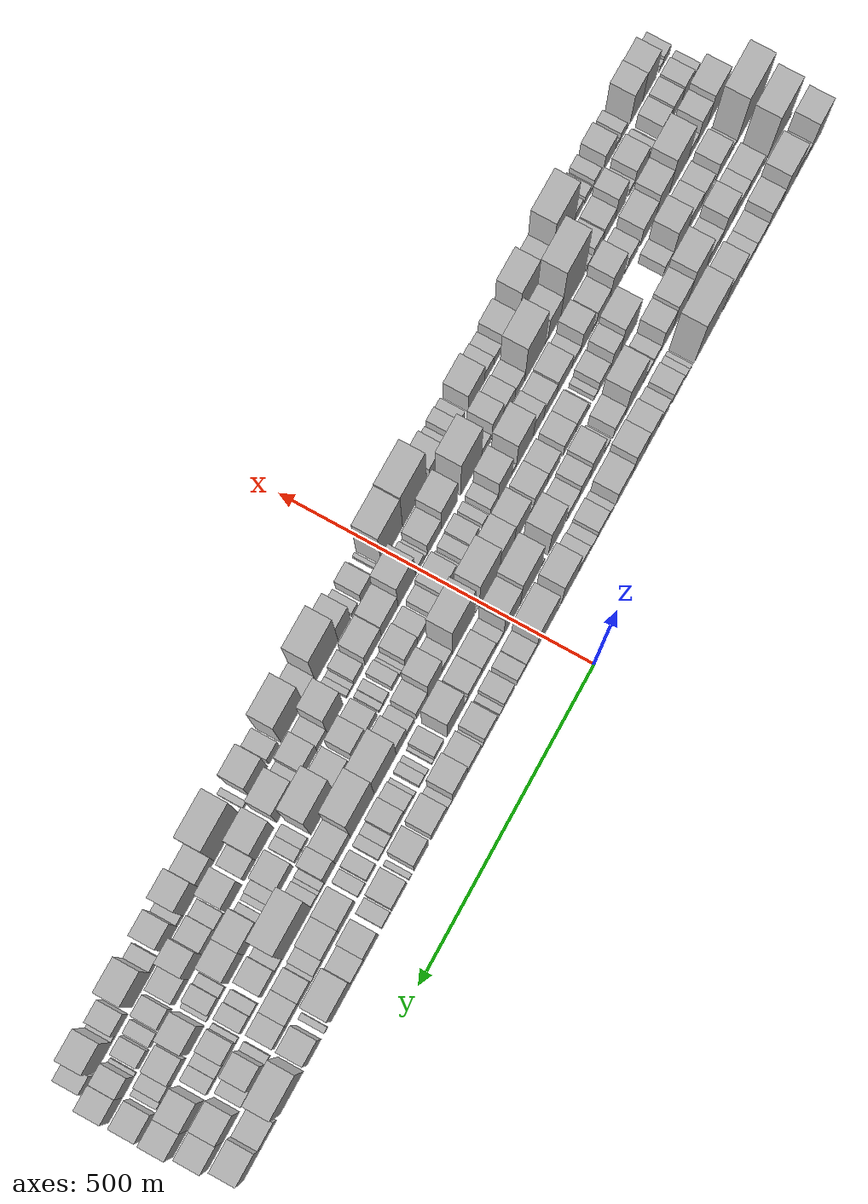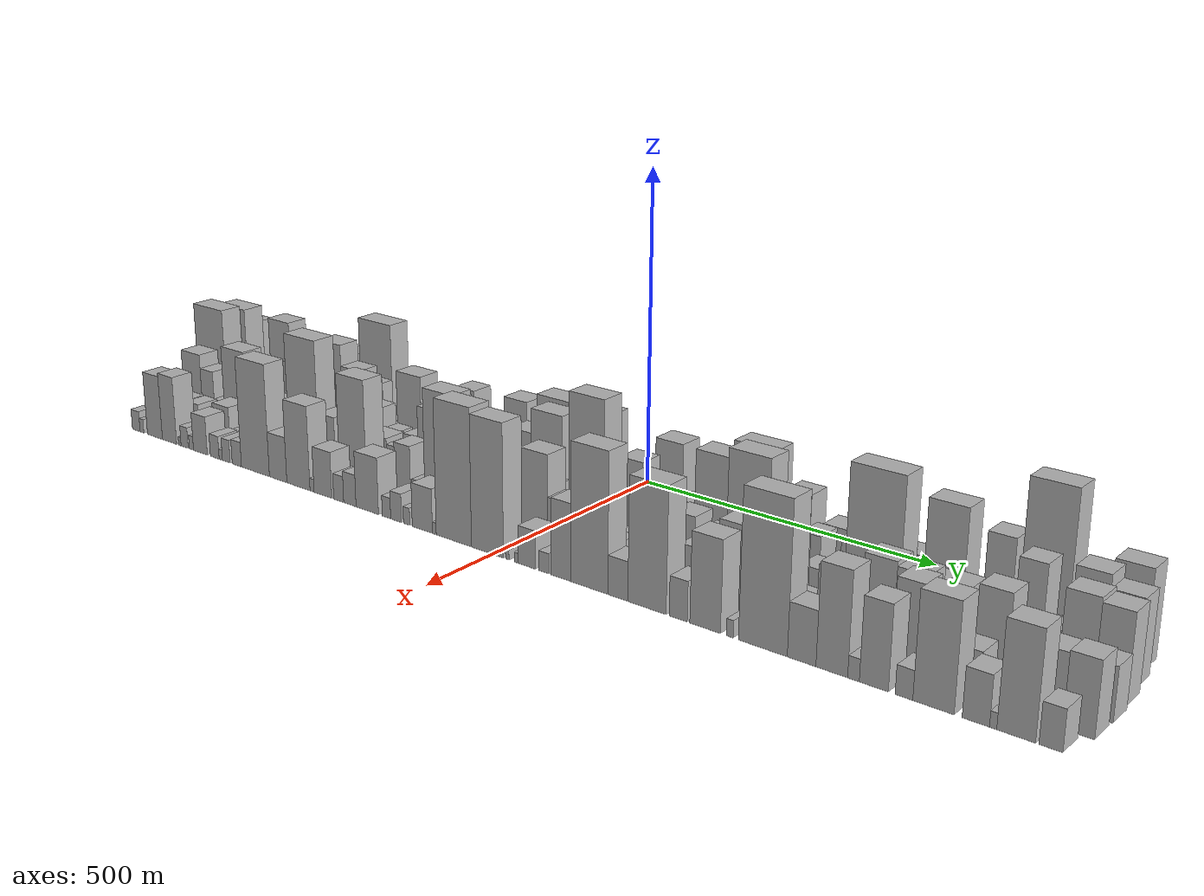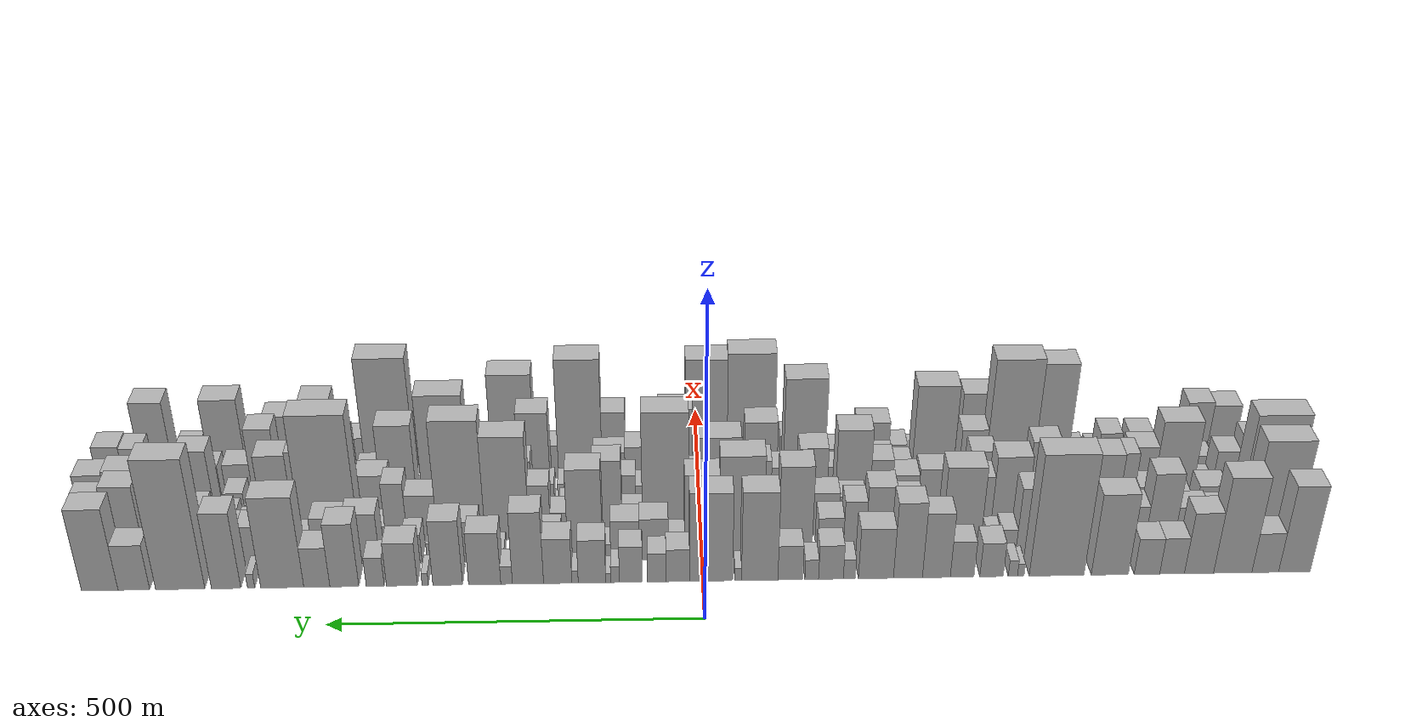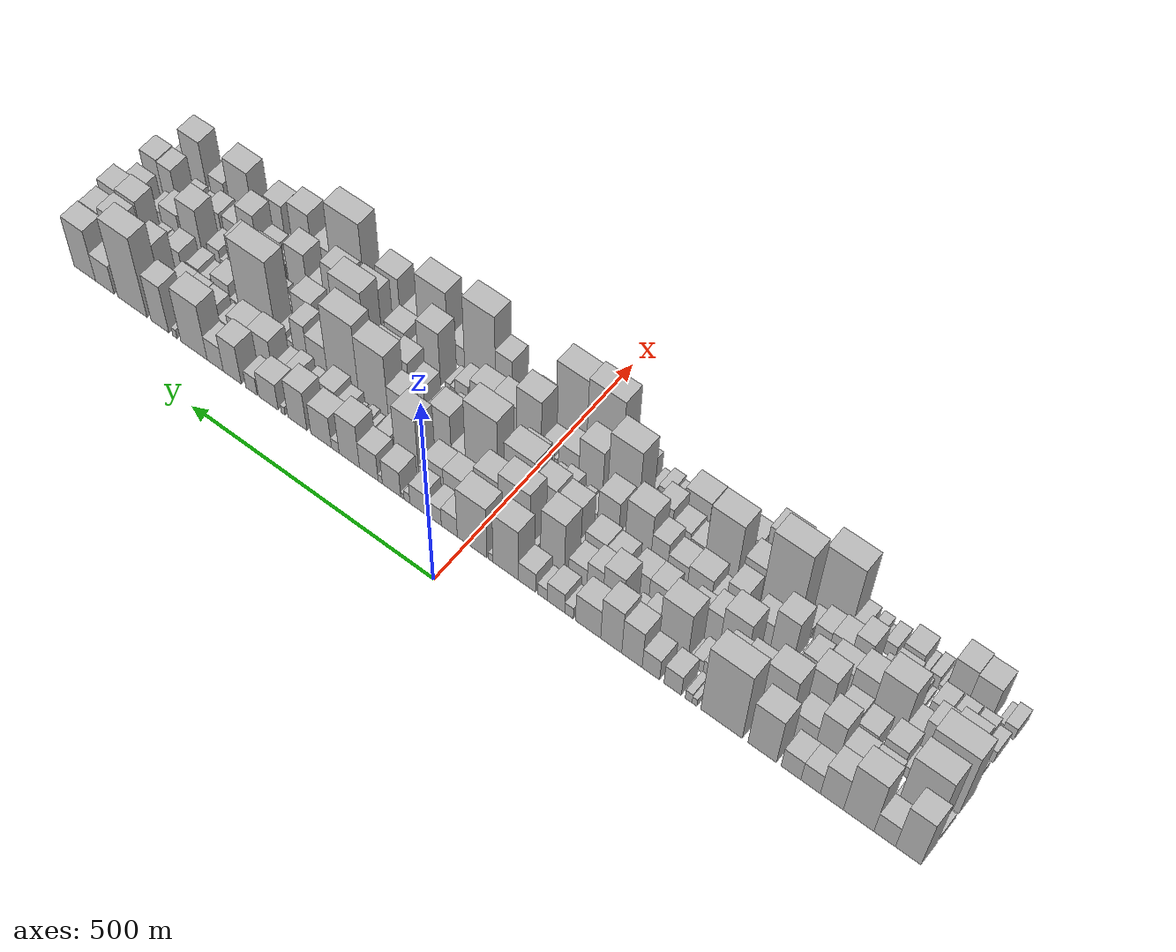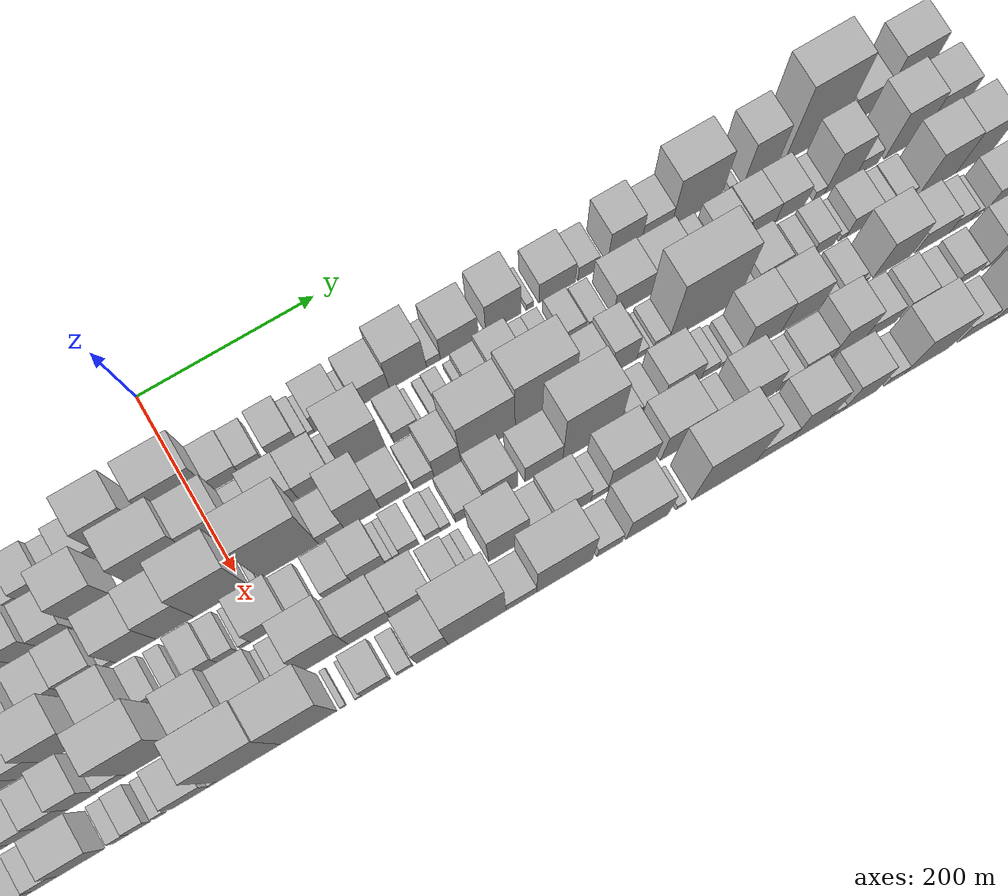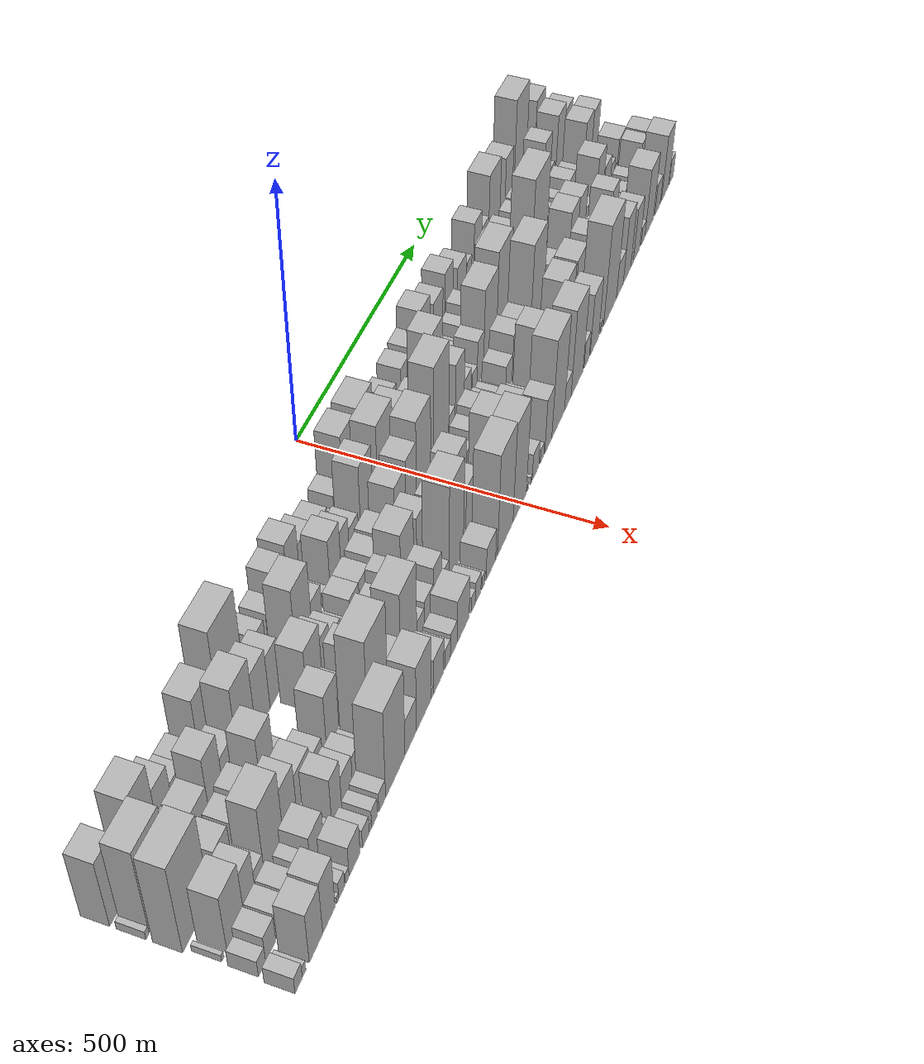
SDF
<sdf version="1.6">
 <world name="default">
  <scene>
   <sky><clouds><speed>12</speed></clouds></sky>
   <ambient>0.4 0.4 0.4 1</ambient>
   <background>0.7 0.7 0.7 1</background>
   <shadows>1</shadows>
  </scene>
  <gravity>0 0 -9.8066</gravity>
  <magnetic_field>6e-06 2.3e-05 -4.2e-05</magnetic_field>
  <physics default="0" name="default_physics" type="ode">
   <ode>
    <solver>
     <type>quick</type>
     <iters>10</iters>
     <sor>1.0</sor>
     <use_dynamic_moi_rescaling>0</use_dynamic_moi_rescaling>
    </solver>
    <constraints>
     <cfm>0</cfm>
     <erp>0.2</erp>
     <contact_max_correcting_vel>100</contact_max_correcting_vel>
     <contact_surface_layer>0.001</contact_surface_layer>
    </constraints>
   </ode>
   <max_step_size>0.004</max_step_size>
   <real_time_factor>1</real_time_factor>
   <real_time_update_rate>250</real_time_update_rate>
  </physics>
  <light name="sun" type="directional">
   <pose>0 0 10 0 0 0</pose>
   <diffuse>0.8 0.8 0.8 1</diffuse>
   <specular>0.2 0.2 0.2 1</specular>
   <attenuation>
    <range>1000</range>
    <constant>0.9</constant>
    <linear>0.01</linear>
    <quadratic>0.001</quadratic>
   </attenuation>
   <direction>-0.5 0.1 -0.9</direction>
  </light>
  <model name="building_1">
   <static>1</static>
   <pose>100.0000 -808.2663 0 0.000000 0.000000 0.000000</pose>
   <link name="link">
    <pose>0 0 72.00 0 0 0</pose>
    <collision name="collision"><geometry><box><size>40.0000 43.4674 144.0000</size></box></geometry></collision>
    <visual name="visual">
     <cast_shadows>0</cast_shadows>
     <geometry><box><size>40.0000 43.4674 144.0000</size></box></geometry>
     <material>
      <script>
       <uri>model://HANNAS_wall/materials/scripts</uri>
       <uri>model://HANNAS_wall/materials/textures</uri>
       <name>vrc/HANNAS_wall</name>
      </script>
     </material>
    </visual>
   </link>
  </model>
  <model name="building_2">
   <static>1</static>
   <pose>100.0000 -768.1492 0 0.000000 0.000000 0.000000</pose>
   <link name="link">
    <pose>0 0 33.00 0 0 0</pose>
    <collision name="collision"><geometry><box><size>40.0000 36.7668 66.0000</size></box></geometry></collision>
    <visual name="visual">
     <cast_shadows>0</cast_shadows>
     <geometry><box><size>40.0000 36.7668 66.0000</size></box></geometry>
     <material>
      <script>
       <uri>model://HANNAS_wall/materials/scripts</uri>
       <uri>model://HANNAS_wall/materials/textures</uri>
       <name>vrc/HANNAS_wall</name>
      </script>
     </material>
    </visual>
   </link>
  </model>
  <model name="building_3">
   <static>1</static>
   <pose>100.0000 -723.4116 0 0.000000 0.000000 0.000000</pose>
   <link name="link">
    <pose>0 0 79.50 0 0 0</pose>
    <collision name="collision"><geometry><box><size>40.0000 52.7085 159.0000</size></box></geometry></collision>
    <visual name="visual">
     <cast_shadows>0</cast_shadows>
     <geometry><box><size>40.0000 52.7085 159.0000</size></box></geometry>
     <material>
      <script>
       <uri>model://HANNAS_wall/materials/scripts</uri>
       <uri>model://HANNAS_wall/materials/textures</uri>
       <name>vrc/HANNAS_wall</name>
      </script>
     </material>
    </visual>
   </link>
  </model>
  <model name="building_4">
   <static>1</static>
   <pose>100.0000 -677.0546 0 0.000000 0.000000 0.000000</pose>
   <link name="link">
    <pose>0 0 51.00 0 0 0</pose>
    <collision name="collision"><geometry><box><size>40.0000 40.0053 102.0000</size></box></geometry></collision>
    <visual name="visual">
     <cast_shadows>0</cast_shadows>
     <geometry><box><size>40.0000 40.0053 102.0000</size></box></geometry>
     <material>
      <script>
       <uri>model://HANNAS_wall/materials/scripts</uri>
       <uri>model://HANNAS_wall/materials/textures</uri>
       <name>vrc/HANNAS_wall</name>
      </script>
     </material>
    </visual>
   </link>
  </model>
  <model name="building_5">
   <static>1</static>
   <pose>100.0000 -640.0161 0 0.000000 0.000000 0.000000</pose>
   <link name="link">
    <pose>0 0 30.00 0 0 0</pose>
    <collision name="collision"><geometry><box><size>40.0000 34.0717 60.0000</size></box></geometry></collision>
    <visual name="visual">
     <cast_shadows>0</cast_shadows>
     <geometry><box><size>40.0000 34.0717 60.0000</size></box></geometry>
     <material>
      <script>
       <uri>model://HANNAS_wall/materials/scripts</uri>
       <uri>model://HANNAS_wall/materials/textures</uri>
       <name>vrc/HANNAS_wall</name>
      </script>
     </material>
    </visual>
   </link>
  </model>
  <model name="building_6">
   <static>1</static>
   <pose>100.0000 -605.4670 0 0.000000 0.000000 0.000000</pose>
   <link name="link">
    <pose>0 0 30.00 0 0 0</pose>
    <collision name="collision"><geometry><box><size>40.0000 35.0265 60.0000</size></box></geometry></collision>
    <visual name="visual">
     <cast_shadows>0</cast_shadows>
     <geometry><box><size>40.0000 35.0265 60.0000</size></box></geometry>
     <material>
      <script>
       <uri>model://HANNAS_wall/materials/scripts</uri>
       <uri>model://HANNAS_wall/materials/textures</uri>
       <name>vrc/HANNAS_wall</name>
      </script>
     </material>
    </visual>
   </link>
  </model>
  <model name="building_7">
   <static>1</static>
   <pose>100.0000 -554.4824 0 0.000000 0.000000 0.000000</pose>
   <link name="link">
    <pose>0 0 67.50 0 0 0</pose>
    <collision name="collision"><geometry><box><size>40.0000 50.9426 135.0000</size></box></geometry></collision>
    <visual name="visual">
     <cast_shadows>0</cast_shadows>
     <geometry><box><size>40.0000 50.9426 135.0000</size></box></geometry>
     <material>
      <script>
       <uri>model://HANNAS_wall/materials/scripts</uri>
       <uri>model://HANNAS_wall/materials/textures</uri>
       <name>vrc/HANNAS_wall</name>
      </script>
     </material>
    </visual>
   </link>
  </model>
  <model name="building_8">
   <static>1</static>
   <pose>100.0000 -481.4646 0 0.000000 0.000000 0.000000</pose>
   <link name="link">
    <pose>0 0 100.50 0 0 0</pose>
    <collision name="collision"><geometry><box><size>40.0000 75.0930 201.0000</size></box></geometry></collision>
    <visual name="visual">
     <cast_shadows>0</cast_shadows>
     <geometry><box><size>40.0000 75.0930 201.0000</size></box></geometry>
     <material>
      <script>
       <uri>model://HANNAS_wall/materials/scripts</uri>
       <uri>model://HANNAS_wall/materials/textures</uri>
       <name>vrc/HANNAS_wall</name>
      </script>
     </material>
    </visual>
   </link>
  </model>
  <model name="building_9">
   <static>1</static>
   <pose>100.0000 -432.3738 0 0.000000 0.000000 0.000000</pose>
   <link name="link">
    <pose>0 0 10.50 0 0 0</pose>
    <collision name="collision"><geometry><box><size>40.0000 9.0886 21.0000</size></box></geometry></collision>
    <visual name="visual">
     <cast_shadows>0</cast_shadows>
     <geometry><box><size>40.0000 9.0886 21.0000</size></box></geometry>
     <material>
      <script>
       <uri>model://HANNAS_wall/materials/scripts</uri>
       <uri>model://HANNAS_wall/materials/textures</uri>
       <name>vrc/HANNAS_wall</name>
      </script>
     </material>
    </visual>
   </link>
  </model>
  <model name="building_10">
   <static>1</static>
   <pose>100.0000 -421.5550 0 0.000000 0.000000 0.000000</pose>
   <link name="link">
    <pose>0 0 13.50 0 0 0</pose>
    <collision name="collision"><geometry><box><size>40.0000 12.5490 27.0000</size></box></geometry></collision>
    <visual name="visual">
     <cast_shadows>0</cast_shadows>
     <geometry><box><size>40.0000 12.5490 27.0000</size></box></geometry>
     <material>
      <script>
       <uri>model://HANNAS_wall/materials/scripts</uri>
       <uri>model://HANNAS_wall/materials/textures</uri>
       <name>vrc/HANNAS_wall</name>
      </script>
     </material>
    </visual>
   </link>
  </model>
  <model name="building_11">
   <static>1</static>
   <pose>100.0000 -392.2786 0 0.000000 0.000000 0.000000</pose>
   <link name="link">
    <pose>0 0 28.50 0 0 0</pose>
    <collision name="collision"><geometry><box><size>40.0000 32.0037 57.0000</size></box></geometry></collision>
    <visual name="visual">
     <cast_shadows>0</cast_shadows>
     <geometry><box><size>40.0000 32.0037 57.0000</size></box></geometry>
     <material>
      <script>
       <uri>model://HANNAS_wall/materials/scripts</uri>
       <uri>model://HANNAS_wall/materials/textures</uri>
       <name>vrc/HANNAS_wall</name>
      </script>
     </material>
    </visual>
   </link>
  </model>
  <model name="building_12">
   <static>1</static>
   <pose>100.0000 -352.0713 0 0.000000 0.000000 0.000000</pose>
   <link name="link">
    <pose>0 0 30.00 0 0 0</pose>
    <collision name="collision"><geometry><box><size>40.0000 32.4109 60.0000</size></box></geometry></collision>
    <visual name="visual">
     <cast_shadows>0</cast_shadows>
     <geometry><box><size>40.0000 32.4109 60.0000</size></box></geometry>
     <material>
      <script>
       <uri>model://HANNAS_wall/materials/scripts</uri>
       <uri>model://HANNAS_wall/materials/textures</uri>
       <name>vrc/HANNAS_wall</name>
      </script>
     </material>
    </visual>
   </link>
  </model>
  <model name="building_13">
   <static>1</static>
   <pose>100.0000 -316.8234 0 0.000000 0.000000 0.000000</pose>
   <link name="link">
    <pose>0 0 54.00 0 0 0</pose>
    <collision name="collision"><geometry><box><size>40.0000 38.0850 108.0000</size></box></geometry></collision>
    <visual name="visual">
     <cast_shadows>0</cast_shadows>
     <geometry><box><size>40.0000 38.0850 108.0000</size></box></geometry>
     <material>
      <script>
       <uri>model://HANNAS_wall/materials/scripts</uri>
       <uri>model://HANNAS_wall/materials/textures</uri>
       <name>vrc/HANNAS_wall</name>
      </script>
     </material>
    </visual>
   </link>
  </model>
  <model name="building_14">
   <static>1</static>
   <pose>100.0000 -278.0052 0 0.000000 0.000000 0.000000</pose>
   <link name="link">
    <pose>0 0 63.00 0 0 0</pose>
    <collision name="collision"><geometry><box><size>40.0000 39.5514 126.0000</size></box></geometry></collision>
    <visual name="visual">
     <cast_shadows>0</cast_shadows>
     <geometry><box><size>40.0000 39.5514 126.0000</size></box></geometry>
     <material>
      <script>
       <uri>model://HANNAS_wall/materials/scripts</uri>
       <uri>model://HANNAS_wall/materials/textures</uri>
       <name>vrc/HANNAS_wall</name>
      </script>
     </material>
    </visual>
   </link>
  </model>
  <model name="building_15">
   <static>1</static>
   <pose>100.0000 -234.2888 0 0.000000 0.000000 0.000000</pose>
   <link name="link">
    <pose>0 0 42.00 0 0 0</pose>
    <collision name="collision"><geometry><box><size>40.0000 47.8813 84.0000</size></box></geometry></collision>
    <visual name="visual">
     <cast_shadows>0</cast_shadows>
     <geometry><box><size>40.0000 47.8813 84.0000</size></box></geometry>
     <material>
      <script>
       <uri>model://HANNAS_wall/materials/scripts</uri>
       <uri>model://HANNAS_wall/materials/textures</uri>
       <name>vrc/HANNAS_wall</name>
      </script>
     </material>
    </visual>
   </link>
  </model>
  <model name="building_16">
   <static>1</static>
   <pose>100.0000 -198.0670 0 0.000000 0.000000 0.000000</pose>
   <link name="link">
    <pose>0 0 16.50 0 0 0</pose>
    <collision name="collision"><geometry><box><size>40.0000 16.5623 33.0000</size></box></geometry></collision>
    <visual name="visual">
     <cast_shadows>0</cast_shadows>
     <geometry><box><size>40.0000 16.5623 33.0000</size></box></geometry>
     <material>
      <script>
       <uri>model://HANNAS_wall/materials/scripts</uri>
       <uri>model://HANNAS_wall/materials/textures</uri>
       <name>vrc/HANNAS_wall</name>
      </script>
     </material>
    </visual>
   </link>
  </model>
  <model name="building_17">
   <static>1</static>
   <pose>100.0000 -172.8965 0 0.000000 0.000000 0.000000</pose>
   <link name="link">
    <pose>0 0 28.50 0 0 0</pose>
    <collision name="collision"><geometry><box><size>40.0000 33.7787 57.0000</size></box></geometry></collision>
    <visual name="visual">
     <cast_shadows>0</cast_shadows>
     <geometry><box><size>40.0000 33.7787 57.0000</size></box></geometry>
     <material>
      <script>
       <uri>model://HANNAS_wall/materials/scripts</uri>
       <uri>model://HANNAS_wall/materials/textures</uri>
       <name>vrc/HANNAS_wall</name>
      </script>
     </material>
    </visual>
   </link>
  </model>
  <model name="building_18">
   <static>1</static>
   <pose>100.0000 -146.7060 0 0.000000 0.000000 0.000000</pose>
   <link name="link">
    <pose>0 0 16.50 0 0 0</pose>
    <collision name="collision"><geometry><box><size>40.0000 18.6024 33.0000</size></box></geometry></collision>
    <visual name="visual">
     <cast_shadows>0</cast_shadows>
     <geometry><box><size>40.0000 18.6024 33.0000</size></box></geometry>
     <material>
      <script>
       <uri>model://HANNAS_wall/materials/scripts</uri>
       <uri>model://HANNAS_wall/materials/textures</uri>
       <name>vrc/HANNAS_wall</name>
      </script>
     </material>
    </visual>
   </link>
  </model>
  <model name="building_19">
   <static>1</static>
   <pose>100.0000 -117.5233 0 0.000000 0.000000 0.000000</pose>
   <link name="link">
    <pose>0 0 28.50 0 0 0</pose>
    <collision name="collision"><geometry><box><size>40.0000 33.7629 57.0000</size></box></geometry></collision>
    <visual name="visual">
     <cast_shadows>0</cast_shadows>
     <geometry><box><size>40.0000 33.7629 57.0000</size></box></geometry>
     <material>
      <script>
       <uri>model://HANNAS_wall/materials/scripts</uri>
       <uri>model://HANNAS_wall/materials/textures</uri>
       <name>vrc/HANNAS_wall</name>
      </script>
     </material>
    </visual>
   </link>
  </model>
  <model name="building_20">
   <static>1</static>
   <pose>100.0000 -75.8628 0 0.000000 0.000000 0.000000</pose>
   <link name="link">
    <pose>0 0 73.50 0 0 0</pose>
    <collision name="collision"><geometry><box><size>40.0000 49.5582 147.0000</size></box></geometry></collision>
    <visual name="visual">
     <cast_shadows>0</cast_shadows>
     <geometry><box><size>40.0000 49.5582 147.0000</size></box></geometry>
     <material>
      <script>
       <uri>model://HANNAS_wall/materials/scripts</uri>
       <uri>model://HANNAS_wall/materials/textures</uri>
       <name>vrc/HANNAS_wall</name>
      </script>
     </material>
    </visual>
   </link>
  </model>
  <model name="building_21">
   <static>1</static>
   <pose>100.0000 -46.5748 0 0.000000 0.000000 0.000000</pose>
   <link name="link">
    <pose>0 0 10.50 0 0 0</pose>
    <collision name="collision"><geometry><box><size>40.0000 9.0179 21.0000</size></box></geometry></collision>
    <visual name="visual">
     <cast_shadows>0</cast_shadows>
     <geometry><box><size>40.0000 9.0179 21.0000</size></box></geometry>
     <material>
      <script>
       <uri>model://HANNAS_wall/materials/scripts</uri>
       <uri>model://HANNAS_wall/materials/textures</uri>
       <name>vrc/HANNAS_wall</name>
      </script>
     </material>
    </visual>
   </link>
  </model>
  <model name="building_22">
   <static>1</static>
   <pose>100.0000 -9.7291 0 0.000000 0.000000 0.000000</pose>
   <link name="link">
    <pose>0 0 73.50 0 0 0</pose>
    <collision name="collision"><geometry><box><size>40.0000 58.6735 147.0000</size></box></geometry></collision>
    <visual name="visual">
     <cast_shadows>0</cast_shadows>
     <geometry><box><size>40.0000 58.6735 147.0000</size></box></geometry>
     <material>
      <script>
       <uri>model://HANNAS_wall/materials/scripts</uri>
       <uri>model://HANNAS_wall/materials/textures</uri>
       <name>vrc/HANNAS_wall</name>
      </script>
     </material>
    </visual>
   </link>
  </model>
  <model name="building_23">
   <static>1</static>
   <pose>100.0000 35.5029 0 0.000000 0.000000 0.000000</pose>
   <link name="link">
    <pose>0 0 27.00 0 0 0</pose>
    <collision name="collision"><geometry><box><size>40.0000 31.7907 54.0000</size></box></geometry></collision>
    <visual name="visual">
     <cast_shadows>0</cast_shadows>
     <geometry><box><size>40.0000 31.7907 54.0000</size></box></geometry>
     <material>
      <script>
       <uri>model://HANNAS_wall/materials/scripts</uri>
       <uri>model://HANNAS_wall/materials/textures</uri>
       <name>vrc/HANNAS_wall</name>
      </script>
     </material>
    </visual>
   </link>
  </model>
  <model name="building_24">
   <static>1</static>
   <pose>100.0000 63.9876 0 0.000000 0.000000 0.000000</pose>
   <link name="link">
    <pose>0 0 24.00 0 0 0</pose>
    <collision name="collision"><geometry><box><size>40.0000 25.1787 48.0000</size></box></geometry></collision>
    <visual name="visual">
     <cast_shadows>0</cast_shadows>
     <geometry><box><size>40.0000 25.1787 48.0000</size></box></geometry>
     <material>
      <script>
       <uri>model://HANNAS_wall/materials/scripts</uri>
       <uri>model://HANNAS_wall/materials/textures</uri>
       <name>vrc/HANNAS_wall</name>
      </script>
     </material>
    </visual>
   </link>
  </model>
  <model name="building_25">
   <static>1</static>
   <pose>100.0000 99.1580 0 0.000000 0.000000 0.000000</pose>
   <link name="link">
    <pose>0 0 30.00 0 0 0</pose>
    <collision name="collision"><geometry><box><size>40.0000 31.1621 60.0000</size></box></geometry></collision>
    <visual name="visual">
     <cast_shadows>0</cast_shadows>
     <geometry><box><size>40.0000 31.1621 60.0000</size></box></geometry>
     <material>
      <script>
       <uri>model://HANNAS_wall/materials/scripts</uri>
       <uri>model://HANNAS_wall/materials/textures</uri>
       <name>vrc/HANNAS_wall</name>
      </script>
     </material>
    </visual>
   </link>
  </model>
  <model name="building_26">
   <static>1</static>
   <pose>100.0000 120.6568 0 0.000000 0.000000 0.000000</pose>
   <link name="link">
    <pose>0 0 13.50 0 0 0</pose>
    <collision name="collision"><geometry><box><size>40.0000 11.8354 27.0000</size></box></geometry></collision>
    <visual name="visual">
     <cast_shadows>0</cast_shadows>
     <geometry><box><size>40.0000 11.8354 27.0000</size></box></geometry>
     <material>
      <script>
       <uri>model://HANNAS_wall/materials/scripts</uri>
       <uri>model://HANNAS_wall/materials/textures</uri>
       <name>vrc/HANNAS_wall</name>
      </script>
     </material>
    </visual>
   </link>
  </model>
  <model name="building_27">
   <static>1</static>
   <pose>100.0000 129.9507 0 0.000000 0.000000 0.000000</pose>
   <link name="link">
    <pose>0 0 7.50 0 0 0</pose>
    <collision name="collision"><geometry><box><size>40.0000 6.7524 15.0000</size></box></geometry></collision>
    <visual name="visual">
     <cast_shadows>0</cast_shadows>
     <geometry><box><size>40.0000 6.7524 15.0000</size></box></geometry>
     <material>
      <script>
       <uri>model://HANNAS_wall/materials/scripts</uri>
       <uri>model://HANNAS_wall/materials/textures</uri>
       <name>vrc/HANNAS_wall</name>
      </script>
     </material>
    </visual>
   </link>
  </model>
  <model name="building_28">
   <static>1</static>
   <pose>100.0000 151.9843 0 0.000000 0.000000 0.000000</pose>
   <link name="link">
    <pose>0 0 36.00 0 0 0</pose>
    <collision name="collision"><geometry><box><size>40.0000 37.3149 72.0000</size></box></geometry></collision>
    <visual name="visual">
     <cast_shadows>0</cast_shadows>
     <geometry><box><size>40.0000 37.3149 72.0000</size></box></geometry>
     <material>
      <script>
       <uri>model://HANNAS_wall/materials/scripts</uri>
       <uri>model://HANNAS_wall/materials/textures</uri>
       <name>vrc/HANNAS_wall</name>
      </script>
     </material>
    </visual>
   </link>
  </model>
  <model name="building_29">
   <static>1</static>
   <pose>100.0000 174.9527 0 0.000000 0.000000 0.000000</pose>
   <link name="link">
    <pose>0 0 10.50 0 0 0</pose>
    <collision name="collision"><geometry><box><size>40.0000 8.6219 21.0000</size></box></geometry></collision>
    <visual name="visual">
     <cast_shadows>0</cast_shadows>
     <geometry><box><size>40.0000 8.6219 21.0000</size></box></geometry>
     <material>
      <script>
       <uri>model://HANNAS_wall/materials/scripts</uri>
       <uri>model://HANNAS_wall/materials/textures</uri>
       <name>vrc/HANNAS_wall</name>
      </script>
     </material>
    </visual>
   </link>
  </model>
  <model name="building_30">
   <static>1</static>
   <pose>100.0000 198.4365 0 0.000000 0.000000 0.000000</pose>
   <link name="link">
    <pose>0 0 37.50 0 0 0</pose>
    <collision name="collision"><geometry><box><size>40.0000 38.3456 75.0000</size></box></geometry></collision>
    <visual name="visual">
     <cast_shadows>0</cast_shadows>
     <geometry><box><size>40.0000 38.3456 75.0000</size></box></geometry>
     <material>
      <script>
       <uri>model://HANNAS_wall/materials/scripts</uri>
       <uri>model://HANNAS_wall/materials/textures</uri>
       <name>vrc/HANNAS_wall</name>
      </script>
     </material>
    </visual>
   </link>
  </model>
  <model name="building_31">
   <static>1</static>
   <pose>100.0000 238.6785 0 0.000000 0.000000 0.000000</pose>
   <link name="link">
    <pose>0 0 60.00 0 0 0</pose>
    <collision name="collision"><geometry><box><size>40.0000 42.1383 120.0000</size></box></geometry></collision>
    <visual name="visual">
     <cast_shadows>0</cast_shadows>
     <geometry><box><size>40.0000 42.1383 120.0000</size></box></geometry>
     <material>
      <script>
       <uri>model://HANNAS_wall/materials/scripts</uri>
       <uri>model://HANNAS_wall/materials/textures</uri>
       <name>vrc/HANNAS_wall</name>
      </script>
     </material>
    </visual>
   </link>
  </model>
  <model name="building_32">
   <static>1</static>
   <pose>100.0000 267.6383 0 0.000000 0.000000 0.000000</pose>
   <link name="link">
    <pose>0 0 15.00 0 0 0</pose>
    <collision name="collision"><geometry><box><size>40.0000 15.7814 30.0000</size></box></geometry></collision>
    <visual name="visual">
     <cast_shadows>0</cast_shadows>
     <geometry><box><size>40.0000 15.7814 30.0000</size></box></geometry>
     <material>
      <script>
       <uri>model://HANNAS_wall/materials/scripts</uri>
       <uri>model://HANNAS_wall/materials/textures</uri>
       <name>vrc/HANNAS_wall</name>
      </script>
     </material>
    </visual>
   </link>
  </model>
  <model name="building_33">
   <static>1</static>
   <pose>100.0000 297.3346 0 0.000000 0.000000 0.000000</pose>
   <link name="link">
    <pose>0 0 43.50 0 0 0</pose>
    <collision name="collision"><geometry><box><size>40.0000 43.6112 87.0000</size></box></geometry></collision>
    <visual name="visual">
     <cast_shadows>0</cast_shadows>
     <geometry><box><size>40.0000 43.6112 87.0000</size></box></geometry>
     <material>
      <script>
       <uri>model://HANNAS_wall/materials/scripts</uri>
       <uri>model://HANNAS_wall/materials/textures</uri>
       <name>vrc/HANNAS_wall</name>
      </script>
     </material>
    </visual>
   </link>
  </model>
  <model name="building_34">
   <static>1</static>
   <pose>100.0000 347.2639 0 0.000000 0.000000 0.000000</pose>
   <link name="link">
    <pose>0 0 54.00 0 0 0</pose>
    <collision name="collision"><geometry><box><size>40.0000 40.2474 108.0000</size></box></geometry></collision>
    <visual name="visual">
     <cast_shadows>0</cast_shadows>
     <geometry><box><size>40.0000 40.2474 108.0000</size></box></geometry>
     <material>
      <script>
       <uri>model://HANNAS_wall/materials/scripts</uri>
       <uri>model://HANNAS_wall/materials/textures</uri>
       <name>vrc/HANNAS_wall</name>
      </script>
     </material>
    </visual>
   </link>
  </model>
  <model name="building_35">
   <static>1</static>
   <pose>100.0000 377.7014 0 0.000000 0.000000 0.000000</pose>
   <link name="link">
    <pose>0 0 10.50 0 0 0</pose>
    <collision name="collision"><geometry><box><size>40.0000 8.6275 21.0000</size></box></geometry></collision>
    <visual name="visual">
     <cast_shadows>0</cast_shadows>
     <geometry><box><size>40.0000 8.6275 21.0000</size></box></geometry>
     <material>
      <script>
       <uri>model://HANNAS_wall/materials/scripts</uri>
       <uri>model://HANNAS_wall/materials/textures</uri>
       <name>vrc/HANNAS_wall</name>
      </script>
     </material>
    </visual>
   </link>
  </model>
  <model name="building_36">
   <static>1</static>
   <pose>100.0000 408.9904 0 0.000000 0.000000 0.000000</pose>
   <link name="link">
    <pose>0 0 36.00 0 0 0</pose>
    <collision name="collision"><geometry><box><size>40.0000 41.9505 72.0000</size></box></geometry></collision>
    <visual name="visual">
     <cast_shadows>0</cast_shadows>
     <geometry><box><size>40.0000 41.9505 72.0000</size></box></geometry>
     <material>
      <script>
       <uri>model://HANNAS_wall/materials/scripts</uri>
       <uri>model://HANNAS_wall/materials/textures</uri>
       <name>vrc/HANNAS_wall</name>
      </script>
     </material>
    </visual>
   </link>
  </model>
  <model name="building_37">
   <static>1</static>
   <pose>100.0000 445.1468 0 0.000000 0.000000 0.000000</pose>
   <link name="link">
    <pose>0 0 24.00 0 0 0</pose>
    <collision name="collision"><geometry><box><size>40.0000 24.3622 48.0000</size></box></geometry></collision>
    <visual name="visual">
     <cast_shadows>0</cast_shadows>
     <geometry><box><size>40.0000 24.3622 48.0000</size></box></geometry>
     <material>
      <script>
       <uri>model://HANNAS_wall/materials/scripts</uri>
       <uri>model://HANNAS_wall/materials/textures</uri>
       <name>vrc/HANNAS_wall</name>
      </script>
     </material>
    </visual>
   </link>
  </model>
  <model name="building_38">
   <static>1</static>
   <pose>100.0000 486.8231 0 0.000000 0.000000 0.000000</pose>
   <link name="link">
    <pose>0 0 52.50 0 0 0</pose>
    <collision name="collision"><geometry><box><size>40.0000 38.9903 105.0000</size></box></geometry></collision>
    <visual name="visual">
     <cast_shadows>0</cast_shadows>
     <geometry><box><size>40.0000 38.9903 105.0000</size></box></geometry>
     <material>
      <script>
       <uri>model://HANNAS_wall/materials/scripts</uri>
       <uri>model://HANNAS_wall/materials/textures</uri>
       <name>vrc/HANNAS_wall</name>
      </script>
     </material>
    </visual>
   </link>
  </model>
  <model name="building_39">
   <static>1</static>
   <pose>100.0000 523.9023 0 0.000000 0.000000 0.000000</pose>
   <link name="link">
    <pose>0 0 33.00 0 0 0</pose>
    <collision name="collision"><geometry><box><size>40.0000 35.1681 66.0000</size></box></geometry></collision>
    <visual name="visual">
     <cast_shadows>0</cast_shadows>
     <geometry><box><size>40.0000 35.1681 66.0000</size></box></geometry>
     <material>
      <script>
       <uri>model://HANNAS_wall/materials/scripts</uri>
       <uri>model://HANNAS_wall/materials/textures</uri>
       <name>vrc/HANNAS_wall</name>
      </script>
     </material>
    </visual>
   </link>
  </model>
  <model name="building_40">
   <static>1</static>
   <pose>100.0000 570.5167 0 0.000000 0.000000 0.000000</pose>
   <link name="link">
    <pose>0 0 75.00 0 0 0</pose>
    <collision name="collision"><geometry><box><size>40.0000 58.0608 150.0000</size></box></geometry></collision>
    <visual name="visual">
     <cast_shadows>0</cast_shadows>
     <geometry><box><size>40.0000 58.0608 150.0000</size></box></geometry>
     <material>
      <script>
       <uri>model://HANNAS_wall/materials/scripts</uri>
       <uri>model://HANNAS_wall/materials/textures</uri>
       <name>vrc/HANNAS_wall</name>
      </script>
     </material>
    </visual>
   </link>
  </model>
  <model name="building_41">
   <static>1</static>
   <pose>100.0000 612.4046 0 0.000000 0.000000 0.000000</pose>
   <link name="link">
    <pose>0 0 12.00 0 0 0</pose>
    <collision name="collision"><geometry><box><size>40.0000 9.7150 24.0000</size></box></geometry></collision>
    <visual name="visual">
     <cast_shadows>0</cast_shadows>
     <geometry><box><size>40.0000 9.7150 24.0000</size></box></geometry>
     <material>
      <script>
       <uri>model://HANNAS_wall/materials/scripts</uri>
       <uri>model://HANNAS_wall/materials/textures</uri>
       <name>vrc/HANNAS_wall</name>
      </script>
     </material>
    </visual>
   </link>
  </model>
  <model name="building_42">
   <static>1</static>
   <pose>100.0000 645.9919 0 0.000000 0.000000 0.000000</pose>
   <link name="link">
    <pose>0 0 63.00 0 0 0</pose>
    <collision name="collision"><geometry><box><size>40.0000 39.4597 126.0000</size></box></geometry></collision>
    <visual name="visual">
     <cast_shadows>0</cast_shadows>
     <geometry><box><size>40.0000 39.4597 126.0000</size></box></geometry>
     <material>
      <script>
       <uri>model://HANNAS_wall/materials/scripts</uri>
       <uri>model://HANNAS_wall/materials/textures</uri>
       <name>vrc/HANNAS_wall</name>
      </script>
     </material>
    </visual>
   </link>
  </model>
  <model name="building_43">
   <static>1</static>
   <pose>100.0000 707.7500 0 0.000000 0.000000 0.000000</pose>
   <link name="link">
    <pose>0 0 106.50 0 0 0</pose>
    <collision name="collision"><geometry><box><size>40.0000 66.0565 213.0000</size></box></geometry></collision>
    <visual name="visual">
     <cast_shadows>0</cast_shadows>
     <geometry><box><size>40.0000 66.0565 213.0000</size></box></geometry>
     <material>
      <script>
       <uri>model://HANNAS_wall/materials/scripts</uri>
       <uri>model://HANNAS_wall/materials/textures</uri>
       <name>vrc/HANNAS_wall</name>
      </script>
     </material>
    </visual>
   </link>
  </model>
  <model name="building_44">
   <static>1</static>
   <pose>100.0000 770.0138 0 0.000000 0.000000 0.000000</pose>
   <link name="link">
    <pose>0 0 37.50 0 0 0</pose>
    <collision name="collision"><geometry><box><size>40.0000 42.4713 75.0000</size></box></geometry></collision>
    <visual name="visual">
     <cast_shadows>0</cast_shadows>
     <geometry><box><size>40.0000 42.4713 75.0000</size></box></geometry>
     <material>
      <script>
       <uri>model://HANNAS_wall/materials/scripts</uri>
       <uri>model://HANNAS_wall/materials/textures</uri>
       <name>vrc/HANNAS_wall</name>
      </script>
     </material>
    </visual>
   </link>
  </model>
  <model name="building_45">
   <static>1</static>
   <pose>100.0000 815.7906 0 0.000000 0.000000 0.000000</pose>
   <link name="link">
    <pose>0 0 67.50 0 0 0</pose>
    <collision name="collision"><geometry><box><size>40.0000 49.0822 135.0000</size></box></geometry></collision>
    <visual name="visual">
     <cast_shadows>0</cast_shadows>
     <geometry><box><size>40.0000 49.0822 135.0000</size></box></geometry>
     <material>
      <script>
       <uri>model://HANNAS_wall/materials/scripts</uri>
       <uri>model://HANNAS_wall/materials/textures</uri>
       <name>vrc/HANNAS_wall</name>
      </script>
     </material>
    </visual>
   </link>
  </model>
  <model name="building_46">
   <static>1</static>
   <pose>149.0000 -825.7551 0 0.000000 0.000000 0.000000</pose>
   <link name="link">
    <pose>0 0 9.00 0 0 0</pose>
    <collision name="collision"><geometry><box><size>40.0000 8.4897 18.0000</size></box></geometry></collision>
    <visual name="visual">
     <cast_shadows>0</cast_shadows>
     <geometry><box><size>40.0000 8.4897 18.0000</size></box></geometry>
     <material>
      <script>
       <uri>model://HANNAS_wall/materials/scripts</uri>
       <uri>model://HANNAS_wall/materials/textures</uri>
       <name>vrc/HANNAS_wall</name>
      </script>
     </material>
    </visual>
   </link>
  </model>
  <model name="building_47">
   <static>1</static>
   <pose>149.0000 -787.9768 0 0.000000 0.000000 0.000000</pose>
   <link name="link">
    <pose>0 0 91.50 0 0 0</pose>
    <collision name="collision"><geometry><box><size>40.0000 67.0671 183.0000</size></box></geometry></collision>
    <visual name="visual">
     <cast_shadows>0</cast_shadows>
     <geometry><box><size>40.0000 67.0671 183.0000</size></box></geometry>
     <material>
      <script>
       <uri>model://HANNAS_wall/materials/scripts</uri>
       <uri>model://HANNAS_wall/materials/textures</uri>
       <name>vrc/HANNAS_wall</name>
      </script>
     </material>
    </visual>
   </link>
  </model>
  <model name="building_48">
   <static>1</static>
   <pose>149.0000 -749.7250 0 0.000000 0.000000 0.000000</pose>
   <link name="link">
    <pose>0 0 10.50 0 0 0</pose>
    <collision name="collision"><geometry><box><size>40.0000 9.4365 21.0000</size></box></geometry></collision>
    <visual name="visual">
     <cast_shadows>0</cast_shadows>
     <geometry><box><size>40.0000 9.4365 21.0000</size></box></geometry>
     <material>
      <script>
       <uri>model://HANNAS_wall/materials/scripts</uri>
       <uri>model://HANNAS_wall/materials/textures</uri>
       <name>vrc/HANNAS_wall</name>
      </script>
     </material>
    </visual>
   </link>
  </model>
  <model name="building_49">
   <static>1</static>
   <pose>149.0000 -715.4548 0 0.000000 0.000000 0.000000</pose>
   <link name="link">
    <pose>0 0 36.00 0 0 0</pose>
    <collision name="collision"><geometry><box><size>40.0000 43.1039 72.0000</size></box></geometry></collision>
    <visual name="visual">
     <cast_shadows>0</cast_shadows>
     <geometry><box><size>40.0000 43.1039 72.0000</size></box></geometry>
     <material>
      <script>
       <uri>model://HANNAS_wall/materials/scripts</uri>
       <uri>model://HANNAS_wall/materials/textures</uri>
       <name>vrc/HANNAS_wall</name>
      </script>
     </material>
    </visual>
   </link>
  </model>
  <model name="building_50">
   <static>1</static>
   <pose>149.0000 -673.1103 0 0.000000 0.000000 0.000000</pose>
   <link name="link">
    <pose>0 0 37.50 0 0 0</pose>
    <collision name="collision"><geometry><box><size>40.0000 41.5851 75.0000</size></box></geometry></collision>
    <visual name="visual">
     <cast_shadows>0</cast_shadows>
     <geometry><box><size>40.0000 41.5851 75.0000</size></box></geometry>
     <material>
      <script>
       <uri>model://HANNAS_wall/materials/scripts</uri>
       <uri>model://HANNAS_wall/materials/textures</uri>
       <name>vrc/HANNAS_wall</name>
      </script>
     </material>
    </visual>
   </link>
  </model>
  <model name="building_51">
   <static>1</static>
   <pose>149.0000 -632.1052 0 0.000000 0.000000 0.000000</pose>
   <link name="link">
    <pose>0 0 66.00 0 0 0</pose>
    <collision name="collision"><geometry><box><size>40.0000 40.4250 132.0000</size></box></geometry></collision>
    <visual name="visual">
     <cast_shadows>0</cast_shadows>
     <geometry><box><size>40.0000 40.4250 132.0000</size></box></geometry>
     <material>
      <script>
       <uri>model://HANNAS_wall/materials/scripts</uri>
       <uri>model://HANNAS_wall/materials/textures</uri>
       <name>vrc/HANNAS_wall</name>
      </script>
     </material>
    </visual>
   </link>
  </model>
  <model name="building_52">
   <static>1</static>
   <pose>149.0000 -590.7707 0 0.000000 0.000000 0.000000</pose>
   <link name="link">
    <pose>0 0 39.00 0 0 0</pose>
    <collision name="collision"><geometry><box><size>40.0000 42.2440 78.0000</size></box></geometry></collision>
    <visual name="visual">
     <cast_shadows>0</cast_shadows>
     <geometry><box><size>40.0000 42.2440 78.0000</size></box></geometry>
     <material>
      <script>
       <uri>model://HANNAS_wall/materials/scripts</uri>
       <uri>model://HANNAS_wall/materials/textures</uri>
       <name>vrc/HANNAS_wall</name>
      </script>
     </material>
    </visual>
   </link>
  </model>
  <model name="building_53">
   <static>1</static>
   <pose>149.0000 -540.1010 0 0.000000 0.000000 0.000000</pose>
   <link name="link">
    <pose>0 0 82.50 0 0 0</pose>
    <collision name="collision"><geometry><box><size>40.0000 53.0954 165.0000</size></box></geometry></collision>
    <visual name="visual">
     <cast_shadows>0</cast_shadows>
     <geometry><box><size>40.0000 53.0954 165.0000</size></box></geometry>
     <material>
      <script>
       <uri>model://HANNAS_wall/materials/scripts</uri>
       <uri>model://HANNAS_wall/materials/textures</uri>
       <name>vrc/HANNAS_wall</name>
      </script>
     </material>
    </visual>
   </link>
  </model>
  <model name="building_54">
   <static>1</static>
   <pose>149.0000 -491.4233 0 0.000000 0.000000 0.000000</pose>
   <link name="link">
    <pose>0 0 64.50 0 0 0</pose>
    <collision name="collision"><geometry><box><size>40.0000 44.2600 129.0000</size></box></geometry></collision>
    <visual name="visual">
     <cast_shadows>0</cast_shadows>
     <geometry><box><size>40.0000 44.2600 129.0000</size></box></geometry>
     <material>
      <script>
       <uri>model://HANNAS_wall/materials/scripts</uri>
       <uri>model://HANNAS_wall/materials/textures</uri>
       <name>vrc/HANNAS_wall</name>
      </script>
     </material>
    </visual>
   </link>
  </model>
  <model name="building_55">
   <static>1</static>
   <pose>149.0000 -451.5261 0 0.000000 0.000000 0.000000</pose>
   <link name="link">
    <pose>0 0 55.50 0 0 0</pose>
    <collision name="collision"><geometry><box><size>40.0000 35.5344 111.0000</size></box></geometry></collision>
    <visual name="visual">
     <cast_shadows>0</cast_shadows>
     <geometry><box><size>40.0000 35.5344 111.0000</size></box></geometry>
     <material>
      <script>
       <uri>model://HANNAS_wall/materials/scripts</uri>
       <uri>model://HANNAS_wall/materials/textures</uri>
       <name>vrc/HANNAS_wall</name>
      </script>
     </material>
    </visual>
   </link>
  </model>
  <model name="building_56">
   <static>1</static>
   <pose>149.0000 -422.6835 0 0.000000 0.000000 0.000000</pose>
   <link name="link">
    <pose>0 0 21.00 0 0 0</pose>
    <collision name="collision"><geometry><box><size>40.0000 22.1510 42.0000</size></box></geometry></collision>
    <visual name="visual">
     <cast_shadows>0</cast_shadows>
     <geometry><box><size>40.0000 22.1510 42.0000</size></box></geometry>
     <material>
      <script>
       <uri>model://HANNAS_wall/materials/scripts</uri>
       <uri>model://HANNAS_wall/materials/textures</uri>
       <name>vrc/HANNAS_wall</name>
      </script>
     </material>
    </visual>
   </link>
  </model>
  <model name="building_57">
   <static>1</static>
   <pose>149.0000 -401.6400 0 0.000000 0.000000 0.000000</pose>
   <link name="link">
    <pose>0 0 18.00 0 0 0</pose>
    <collision name="collision"><geometry><box><size>40.0000 19.9360 36.0000</size></box></geometry></collision>
    <visual name="visual">
     <cast_shadows>0</cast_shadows>
     <geometry><box><size>40.0000 19.9360 36.0000</size></box></geometry>
     <material>
      <script>
       <uri>model://HANNAS_wall/materials/scripts</uri>
       <uri>model://HANNAS_wall/materials/textures</uri>
       <name>vrc/HANNAS_wall</name>
      </script>
     </material>
    </visual>
   </link>
  </model>
  <model name="building_58">
   <static>1</static>
   <pose>149.0000 -387.4839 0 0.000000 0.000000 0.000000</pose>
   <link name="link">
    <pose>0 0 9.00 0 0 0</pose>
    <collision name="collision"><geometry><box><size>40.0000 8.3761 18.0000</size></box></geometry></collision>
    <visual name="visual">
     <cast_shadows>0</cast_shadows>
     <geometry><box><size>40.0000 8.3761 18.0000</size></box></geometry>
     <material>
      <script>
       <uri>model://HANNAS_wall/materials/scripts</uri>
       <uri>model://HANNAS_wall/materials/textures</uri>
       <name>vrc/HANNAS_wall</name>
      </script>
     </material>
    </visual>
   </link>
  </model>
  <model name="building_59">
   <static>1</static>
   <pose>149.0000 -356.2429 0 0.000000 0.000000 0.000000</pose>
   <link name="link">
    <pose>0 0 73.50 0 0 0</pose>
    <collision name="collision"><geometry><box><size>40.0000 54.1060 147.0000</size></box></geometry></collision>
    <visual name="visual">
     <cast_shadows>0</cast_shadows>
     <geometry><box><size>40.0000 54.1060 147.0000</size></box></geometry>
     <material>
      <script>
       <uri>model://HANNAS_wall/materials/scripts</uri>
       <uri>model://HANNAS_wall/materials/textures</uri>
       <name>vrc/HANNAS_wall</name>
      </script>
     </material>
    </visual>
   </link>
  </model>
  <model name="building_60">
   <static>1</static>
   <pose>149.0000 -311.7719 0 0.000000 0.000000 0.000000</pose>
   <link name="link">
    <pose>0 0 30.00 0 0 0</pose>
    <collision name="collision"><geometry><box><size>40.0000 34.8358 60.0000</size></box></geometry></collision>
    <visual name="visual">
     <cast_shadows>0</cast_shadows>
     <geometry><box><size>40.0000 34.8358 60.0000</size></box></geometry>
     <material>
      <script>
       <uri>model://HANNAS_wall/materials/scripts</uri>
       <uri>model://HANNAS_wall/materials/textures</uri>
       <name>vrc/HANNAS_wall</name>
      </script>
     </material>
    </visual>
   </link>
  </model>
  <model name="building_61">
   <static>1</static>
   <pose>149.0000 -277.9789 0 0.000000 0.000000 0.000000</pose>
   <link name="link">
    <pose>0 0 15.00 0 0 0</pose>
    <collision name="collision"><geometry><box><size>40.0000 16.7503 30.0000</size></box></geometry></collision>
    <visual name="visual">
     <cast_shadows>0</cast_shadows>
     <geometry><box><size>40.0000 16.7503 30.0000</size></box></geometry>
     <material>
      <script>
       <uri>model://HANNAS_wall/materials/scripts</uri>
       <uri>model://HANNAS_wall/materials/textures</uri>
       <name>vrc/HANNAS_wall</name>
      </script>
     </material>
    </visual>
   </link>
  </model>
  <model name="building_62">
   <static>1</static>
   <pose>149.0000 -244.0146 0 0.000000 0.000000 0.000000</pose>
   <link name="link">
    <pose>0 0 58.50 0 0 0</pose>
    <collision name="collision"><geometry><box><size>40.0000 39.1783 117.0000</size></box></geometry></collision>
    <visual name="visual">
     <cast_shadows>0</cast_shadows>
     <geometry><box><size>40.0000 39.1783 117.0000</size></box></geometry>
     <material>
      <script>
       <uri>model://HANNAS_wall/materials/scripts</uri>
       <uri>model://HANNAS_wall/materials/textures</uri>
       <name>vrc/HANNAS_wall</name>
      </script>
     </material>
    </visual>
   </link>
  </model>
  <model name="building_63">
   <static>1</static>
   <pose>149.0000 -209.0764 0 0.000000 0.000000 0.000000</pose>
   <link name="link">
    <pose>0 0 46.50 0 0 0</pose>
    <collision name="collision"><geometry><box><size>40.0000 30.6981 93.0000</size></box></geometry></collision>
    <visual name="visual">
     <cast_shadows>0</cast_shadows>
     <geometry><box><size>40.0000 30.6981 93.0000</size></box></geometry>
     <material>
      <script>
       <uri>model://HANNAS_wall/materials/scripts</uri>
       <uri>model://HANNAS_wall/materials/textures</uri>
       <name>vrc/HANNAS_wall</name>
      </script>
     </material>
    </visual>
   </link>
  </model>
  <model name="building_64">
   <static>1</static>
   <pose>149.0000 -176.1616 0 0.000000 0.000000 0.000000</pose>
   <link name="link">
    <pose>0 0 33.00 0 0 0</pose>
    <collision name="collision"><geometry><box><size>40.0000 35.1316 66.0000</size></box></geometry></collision>
    <visual name="visual">
     <cast_shadows>0</cast_shadows>
     <geometry><box><size>40.0000 35.1316 66.0000</size></box></geometry>
     <material>
      <script>
       <uri>model://HANNAS_wall/materials/scripts</uri>
       <uri>model://HANNAS_wall/materials/textures</uri>
       <name>vrc/HANNAS_wall</name>
      </script>
     </material>
    </visual>
   </link>
  </model>
  <model name="building_65">
   <static>1</static>
   <pose>149.0000 -127.5393 0 0.000000 0.000000 0.000000</pose>
   <link name="link">
    <pose>0 0 76.50 0 0 0</pose>
    <collision name="collision"><geometry><box><size>40.0000 46.1130 153.0000</size></box></geometry></collision>
    <visual name="visual">
     <cast_shadows>0</cast_shadows>
     <geometry><box><size>40.0000 46.1130 153.0000</size></box></geometry>
     <material>
      <script>
       <uri>model://HANNAS_wall/materials/scripts</uri>
       <uri>model://HANNAS_wall/materials/textures</uri>
       <name>vrc/HANNAS_wall</name>
      </script>
     </material>
    </visual>
   </link>
  </model>
  <model name="building_66">
   <static>1</static>
   <pose>149.0000 -89.4264 0 0.000000 0.000000 0.000000</pose>
   <link name="link">
    <pose>0 0 10.50 0 0 0</pose>
    <collision name="collision"><geometry><box><size>40.0000 10.1128 21.0000</size></box></geometry></collision>
    <visual name="visual">
     <cast_shadows>0</cast_shadows>
     <geometry><box><size>40.0000 10.1128 21.0000</size></box></geometry>
     <material>
      <script>
       <uri>model://HANNAS_wall/materials/scripts</uri>
       <uri>model://HANNAS_wall/materials/textures</uri>
       <name>vrc/HANNAS_wall</name>
      </script>
     </material>
    </visual>
   </link>
  </model>
  <model name="building_67">
   <static>1</static>
   <pose>149.0000 -53.6856 0 0.000000 0.000000 0.000000</pose>
   <link name="link">
    <pose>0 0 85.50 0 0 0</pose>
    <collision name="collision"><geometry><box><size>40.0000 61.3687 171.0000</size></box></geometry></collision>
    <visual name="visual">
     <cast_shadows>0</cast_shadows>
     <geometry><box><size>40.0000 61.3687 171.0000</size></box></geometry>
     <material>
      <script>
       <uri>model://HANNAS_wall/materials/scripts</uri>
       <uri>model://HANNAS_wall/materials/textures</uri>
       <name>vrc/HANNAS_wall</name>
      </script>
     </material>
    </visual>
   </link>
  </model>
  <model name="building_68">
   <static>1</static>
   <pose>149.0000 0.9310 0 0.000000 0.000000 0.000000</pose>
   <link name="link">
    <pose>0 0 70.50 0 0 0</pose>
    <collision name="collision"><geometry><box><size>40.0000 47.8645 141.0000</size></box></geometry></collision>
    <visual name="visual">
     <cast_shadows>0</cast_shadows>
     <geometry><box><size>40.0000 47.8645 141.0000</size></box></geometry>
     <material>
      <script>
       <uri>model://HANNAS_wall/materials/scripts</uri>
       <uri>model://HANNAS_wall/materials/textures</uri>
       <name>vrc/HANNAS_wall</name>
      </script>
     </material>
    </visual>
   </link>
  </model>
  <model name="building_69">
   <static>1</static>
   <pose>149.0000 36.1808 0 0.000000 0.000000 0.000000</pose>
   <link name="link">
    <pose>0 0 19.50 0 0 0</pose>
    <collision name="collision"><geometry><box><size>40.0000 22.6350 39.0000</size></box></geometry></collision>
    <visual name="visual">
     <cast_shadows>0</cast_shadows>
     <geometry><box><size>40.0000 22.6350 39.0000</size></box></geometry>
     <material>
      <script>
       <uri>model://HANNAS_wall/materials/scripts</uri>
       <uri>model://HANNAS_wall/materials/textures</uri>
       <name>vrc/HANNAS_wall</name>
      </script>
     </material>
    </visual>
   </link>
  </model>
  <model name="building_70">
   <static>1</static>
   <pose>149.0000 67.4832 0 0.000000 0.000000 0.000000</pose>
   <link name="link">
    <pose>0 0 34.50 0 0 0</pose>
    <collision name="collision"><geometry><box><size>40.0000 39.9698 69.0000</size></box></geometry></collision>
    <visual name="visual">
     <cast_shadows>0</cast_shadows>
     <geometry><box><size>40.0000 39.9698 69.0000</size></box></geometry>
     <material>
      <script>
       <uri>model://HANNAS_wall/materials/scripts</uri>
       <uri>model://HANNAS_wall/materials/textures</uri>
       <name>vrc/HANNAS_wall</name>
      </script>
     </material>
    </visual>
   </link>
  </model>
  <model name="building_71">
   <static>1</static>
   <pose>149.0000 107.2669 0 0.000000 0.000000 0.000000</pose>
   <link name="link">
    <pose>0 0 33.00 0 0 0</pose>
    <collision name="collision"><geometry><box><size>40.0000 39.5975 66.0000</size></box></geometry></collision>
    <visual name="visual">
     <cast_shadows>0</cast_shadows>
     <geometry><box><size>40.0000 39.5975 66.0000</size></box></geometry>
     <material>
      <script>
       <uri>model://HANNAS_wall/materials/scripts</uri>
       <uri>model://HANNAS_wall/materials/textures</uri>
       <name>vrc/HANNAS_wall</name>
      </script>
     </material>
    </visual>
   </link>
  </model>
  <model name="building_72">
   <static>1</static>
   <pose>149.0000 132.5299 0 0.000000 0.000000 0.000000</pose>
   <link name="link">
    <pose>0 0 13.50 0 0 0</pose>
    <collision name="collision"><geometry><box><size>40.0000 10.9285 27.0000</size></box></geometry></collision>
    <visual name="visual">
     <cast_shadows>0</cast_shadows>
     <geometry><box><size>40.0000 10.9285 27.0000</size></box></geometry>
     <material>
      <script>
       <uri>model://HANNAS_wall/materials/scripts</uri>
       <uri>model://HANNAS_wall/materials/textures</uri>
       <name>vrc/HANNAS_wall</name>
      </script>
     </material>
    </visual>
   </link>
  </model>
  <model name="building_73">
   <static>1</static>
   <pose>149.0000 161.9087 0 0.000000 0.000000 0.000000</pose>
   <link name="link">
    <pose>0 0 76.50 0 0 0</pose>
    <collision name="collision"><geometry><box><size>40.0000 47.8291 153.0000</size></box></geometry></collision>
    <visual name="visual">
     <cast_shadows>0</cast_shadows>
     <geometry><box><size>40.0000 47.8291 153.0000</size></box></geometry>
     <material>
      <script>
       <uri>model://HANNAS_wall/materials/scripts</uri>
       <uri>model://HANNAS_wall/materials/textures</uri>
       <name>vrc/HANNAS_wall</name>
      </script>
     </material>
    </visual>
   </link>
  </model>
  <model name="building_74">
   <static>1</static>
   <pose>149.0000 208.8292 0 0.000000 0.000000 0.000000</pose>
   <link name="link">
    <pose>0 0 25.50 0 0 0</pose>
    <collision name="collision"><geometry><box><size>40.0000 28.0120 51.0000</size></box></geometry></collision>
    <visual name="visual">
     <cast_shadows>0</cast_shadows>
     <geometry><box><size>40.0000 28.0120 51.0000</size></box></geometry>
     <material>
      <script>
       <uri>model://HANNAS_wall/materials/scripts</uri>
       <uri>model://HANNAS_wall/materials/textures</uri>
       <name>vrc/HANNAS_wall</name>
      </script>
     </material>
    </visual>
   </link>
  </model>
  <model name="building_75">
   <static>1</static>
   <pose>149.0000 225.8930 0 0.000000 0.000000 0.000000</pose>
   <link name="link">
    <pose>0 0 7.50 0 0 0</pose>
    <collision name="collision"><geometry><box><size>40.0000 6.1156 15.0000</size></box></geometry></collision>
    <visual name="visual">
     <cast_shadows>0</cast_shadows>
     <geometry><box><size>40.0000 6.1156 15.0000</size></box></geometry>
     <material>
      <script>
       <uri>model://HANNAS_wall/materials/scripts</uri>
       <uri>model://HANNAS_wall/materials/textures</uri>
       <name>vrc/HANNAS_wall</name>
      </script>
     </material>
    </visual>
   </link>
  </model>
  <model name="building_76">
   <static>1</static>
   <pose>149.0000 243.1182 0 0.000000 0.000000 0.000000</pose>
   <link name="link">
    <pose>0 0 10.50 0 0 0</pose>
    <collision name="collision"><geometry><box><size>40.0000 10.3347 21.0000</size></box></geometry></collision>
    <visual name="visual">
     <cast_shadows>0</cast_shadows>
     <geometry><box><size>40.0000 10.3347 21.0000</size></box></geometry>
     <material>
      <script>
       <uri>model://HANNAS_wall/materials/scripts</uri>
       <uri>model://HANNAS_wall/materials/textures</uri>
       <name>vrc/HANNAS_wall</name>
      </script>
     </material>
    </visual>
   </link>
  </model>
  <model name="building_77">
   <static>1</static>
   <pose>149.0000 256.8035 0 0.000000 0.000000 0.000000</pose>
   <link name="link">
    <pose>0 0 15.00 0 0 0</pose>
    <collision name="collision"><geometry><box><size>40.0000 17.0359 30.0000</size></box></geometry></collision>
    <visual name="visual">
     <cast_shadows>0</cast_shadows>
     <geometry><box><size>40.0000 17.0359 30.0000</size></box></geometry>
     <material>
      <script>
       <uri>model://HANNAS_wall/materials/scripts</uri>
       <uri>model://HANNAS_wall/materials/textures</uri>
       <name>vrc/HANNAS_wall</name>
      </script>
     </material>
    </visual>
   </link>
  </model>
  <model name="building_78">
   <static>1</static>
   <pose>149.0000 277.6203 0 0.000000 0.000000 0.000000</pose>
   <link name="link">
    <pose>0 0 10.50 0 0 0</pose>
    <collision name="collision"><geometry><box><size>40.0000 8.5977 21.0000</size></box></geometry></collision>
    <visual name="visual">
     <cast_shadows>0</cast_shadows>
     <geometry><box><size>40.0000 8.5977 21.0000</size></box></geometry>
     <material>
      <script>
       <uri>model://HANNAS_wall/materials/scripts</uri>
       <uri>model://HANNAS_wall/materials/textures</uri>
       <name>vrc/HANNAS_wall</name>
      </script>
     </material>
    </visual>
   </link>
  </model>
  <model name="building_79">
   <static>1</static>
   <pose>149.0000 294.7718 0 0.000000 0.000000 0.000000</pose>
   <link name="link">
    <pose>0 0 24.00 0 0 0</pose>
    <collision name="collision"><geometry><box><size>40.0000 25.7053 48.0000</size></box></geometry></collision>
    <visual name="visual">
     <cast_shadows>0</cast_shadows>
     <geometry><box><size>40.0000 25.7053 48.0000</size></box></geometry>
     <material>
      <script>
       <uri>model://HANNAS_wall/materials/scripts</uri>
       <uri>model://HANNAS_wall/materials/textures</uri>
       <name>vrc/HANNAS_wall</name>
      </script>
     </material>
    </visual>
   </link>
  </model>
  <model name="building_80">
   <static>1</static>
   <pose>149.0000 325.1188 0 0.000000 0.000000 0.000000</pose>
   <link name="link">
    <pose>0 0 34.50 0 0 0</pose>
    <collision name="collision"><geometry><box><size>40.0000 34.9887 69.0000</size></box></geometry></collision>
    <visual name="visual">
     <cast_shadows>0</cast_shadows>
     <geometry><box><size>40.0000 34.9887 69.0000</size></box></geometry>
     <material>
      <script>
       <uri>model://HANNAS_wall/materials/scripts</uri>
       <uri>model://HANNAS_wall/materials/textures</uri>
       <name>vrc/HANNAS_wall</name>
      </script>
     </material>
    </visual>
   </link>
  </model>
  <model name="building_81">
   <static>1</static>
   <pose>149.0000 351.9429 0 0.000000 0.000000 0.000000</pose>
   <link name="link">
    <pose>0 0 16.50 0 0 0</pose>
    <collision name="collision"><geometry><box><size>40.0000 18.6596 33.0000</size></box></geometry></collision>
    <visual name="visual">
     <cast_shadows>0</cast_shadows>
     <geometry><box><size>40.0000 18.6596 33.0000</size></box></geometry>
     <material>
      <script>
       <uri>model://HANNAS_wall/materials/scripts</uri>
       <uri>model://HANNAS_wall/materials/textures</uri>
       <name>vrc/HANNAS_wall</name>
      </script>
     </material>
    </visual>
   </link>
  </model>
  <model name="building_82">
   <static>1</static>
   <pose>149.0000 370.4144 0 0.000000 0.000000 0.000000</pose>
   <link name="link">
    <pose>0 0 16.50 0 0 0</pose>
    <collision name="collision"><geometry><box><size>40.0000 18.2834 33.0000</size></box></geometry></collision>
    <visual name="visual">
     <cast_shadows>0</cast_shadows>
     <geometry><box><size>40.0000 18.2834 33.0000</size></box></geometry>
     <material>
      <script>
       <uri>model://HANNAS_wall/materials/scripts</uri>
       <uri>model://HANNAS_wall/materials/textures</uri>
       <name>vrc/HANNAS_wall</name>
      </script>
     </material>
    </visual>
   </link>
  </model>
  <model name="building_83">
   <static>1</static>
   <pose>149.0000 399.3606 0 0.000000 0.000000 0.000000</pose>
   <link name="link">
    <pose>0 0 24.00 0 0 0</pose>
    <collision name="collision"><geometry><box><size>40.0000 25.6090 48.0000</size></box></geometry></collision>
    <visual name="visual">
     <cast_shadows>0</cast_shadows>
     <geometry><box><size>40.0000 25.6090 48.0000</size></box></geometry>
     <material>
      <script>
       <uri>model://HANNAS_wall/materials/scripts</uri>
       <uri>model://HANNAS_wall/materials/textures</uri>
       <name>vrc/HANNAS_wall</name>
      </script>
     </material>
    </visual>
   </link>
  </model>
  <model name="building_84">
   <static>1</static>
   <pose>149.0000 425.7393 0 0.000000 0.000000 0.000000</pose>
   <link name="link">
    <pose>0 0 18.00 0 0 0</pose>
    <collision name="collision"><geometry><box><size>40.0000 21.1485 36.0000</size></box></geometry></collision>
    <visual name="visual">
     <cast_shadows>0</cast_shadows>
     <geometry><box><size>40.0000 21.1485 36.0000</size></box></geometry>
     <material>
      <script>
       <uri>model://HANNAS_wall/materials/scripts</uri>
       <uri>model://HANNAS_wall/materials/textures</uri>
       <name>vrc/HANNAS_wall</name>
      </script>
     </material>
    </visual>
   </link>
  </model>
  <model name="building_85">
   <static>1</static>
   <pose>149.0000 467.0813 0 0.000000 0.000000 0.000000</pose>
   <link name="link">
    <pose>0 0 42.00 0 0 0</pose>
    <collision name="collision"><geometry><box><size>40.0000 45.5354 84.0000</size></box></geometry></collision>
    <visual name="visual">
     <cast_shadows>0</cast_shadows>
     <geometry><box><size>40.0000 45.5354 84.0000</size></box></geometry>
     <material>
      <script>
       <uri>model://HANNAS_wall/materials/scripts</uri>
       <uri>model://HANNAS_wall/materials/textures</uri>
       <name>vrc/HANNAS_wall</name>
      </script>
     </material>
    </visual>
   </link>
  </model>
  <model name="building_86">
   <static>1</static>
   <pose>149.0000 512.1432 0 0.000000 0.000000 0.000000</pose>
   <link name="link">
    <pose>0 0 39.00 0 0 0</pose>
    <collision name="collision"><geometry><box><size>40.0000 44.5883 78.0000</size></box></geometry></collision>
    <visual name="visual">
     <cast_shadows>0</cast_shadows>
     <geometry><box><size>40.0000 44.5883 78.0000</size></box></geometry>
     <material>
      <script>
       <uri>model://HANNAS_wall/materials/scripts</uri>
       <uri>model://HANNAS_wall/materials/textures</uri>
       <name>vrc/HANNAS_wall</name>
      </script>
     </material>
    </visual>
   </link>
  </model>
  <model name="building_87">
   <static>1</static>
   <pose>149.0000 546.4619 0 0.000000 0.000000 0.000000</pose>
   <link name="link">
    <pose>0 0 24.00 0 0 0</pose>
    <collision name="collision"><geometry><box><size>40.0000 24.0492 48.0000</size></box></geometry></collision>
    <visual name="visual">
     <cast_shadows>0</cast_shadows>
     <geometry><box><size>40.0000 24.0492 48.0000</size></box></geometry>
     <material>
      <script>
       <uri>model://HANNAS_wall/materials/scripts</uri>
       <uri>model://HANNAS_wall/materials/textures</uri>
       <name>vrc/HANNAS_wall</name>
      </script>
     </material>
    </visual>
   </link>
  </model>
  <model name="building_88">
   <static>1</static>
   <pose>149.0000 562.3476 0 0.000000 0.000000 0.000000</pose>
   <link name="link">
    <pose>0 0 9.00 0 0 0</pose>
    <collision name="collision"><geometry><box><size>40.0000 7.7222 18.0000</size></box></geometry></collision>
    <visual name="visual">
     <cast_shadows>0</cast_shadows>
     <geometry><box><size>40.0000 7.7222 18.0000</size></box></geometry>
     <material>
      <script>
       <uri>model://HANNAS_wall/materials/scripts</uri>
       <uri>model://HANNAS_wall/materials/textures</uri>
       <name>vrc/HANNAS_wall</name>
      </script>
     </material>
    </visual>
   </link>
  </model>
  <model name="building_89">
   <static>1</static>
   <pose>149.0000 582.9669 0 0.000000 0.000000 0.000000</pose>
   <link name="link">
    <pose>0 0 31.50 0 0 0</pose>
    <collision name="collision"><geometry><box><size>40.0000 33.5165 63.0000</size></box></geometry></collision>
    <visual name="visual">
     <cast_shadows>0</cast_shadows>
     <geometry><box><size>40.0000 33.5165 63.0000</size></box></geometry>
     <material>
      <script>
       <uri>model://HANNAS_wall/materials/scripts</uri>
       <uri>model://HANNAS_wall/materials/textures</uri>
       <name>vrc/HANNAS_wall</name>
      </script>
     </material>
    </visual>
   </link>
  </model>
  <model name="building_90">
   <static>1</static>
   <pose>149.0000 616.6280 0 0.000000 0.000000 0.000000</pose>
   <link name="link">
    <pose>0 0 33.00 0 0 0</pose>
    <collision name="collision"><geometry><box><size>40.0000 33.8057 66.0000</size></box></geometry></collision>
    <visual name="visual">
     <cast_shadows>0</cast_shadows>
     <geometry><box><size>40.0000 33.8057 66.0000</size></box></geometry>
     <material>
      <script>
       <uri>model://HANNAS_wall/materials/scripts</uri>
       <uri>model://HANNAS_wall/materials/textures</uri>
       <name>vrc/HANNAS_wall</name>
      </script>
     </material>
    </visual>
   </link>
  </model>
  <model name="building_91">
   <static>1</static>
   <pose>149.0000 650.7680 0 0.000000 0.000000 0.000000</pose>
   <link name="link">
    <pose>0 0 33.00 0 0 0</pose>
    <collision name="collision"><geometry><box><size>40.0000 34.4743 66.0000</size></box></geometry></collision>
    <visual name="visual">
     <cast_shadows>0</cast_shadows>
     <geometry><box><size>40.0000 34.4743 66.0000</size></box></geometry>
     <material>
      <script>
       <uri>model://HANNAS_wall/materials/scripts</uri>
       <uri>model://HANNAS_wall/materials/textures</uri>
       <name>vrc/HANNAS_wall</name>
      </script>
     </material>
    </visual>
   </link>
  </model>
  <model name="building_92">
   <static>1</static>
   <pose>149.0000 684.6833 0 0.000000 0.000000 0.000000</pose>
   <link name="link">
    <pose>0 0 13.50 0 0 0</pose>
    <collision name="collision"><geometry><box><size>40.0000 13.3561 27.0000</size></box></geometry></collision>
    <visual name="visual">
     <cast_shadows>0</cast_shadows>
     <geometry><box><size>40.0000 13.3561 27.0000</size></box></geometry>
     <material>
      <script>
       <uri>model://HANNAS_wall/materials/scripts</uri>
       <uri>model://HANNAS_wall/materials/textures</uri>
       <name>vrc/HANNAS_wall</name>
      </script>
     </material>
    </visual>
   </link>
  </model>
  <model name="building_93">
   <static>1</static>
   <pose>149.0000 710.3663 0 0.000000 0.000000 0.000000</pose>
   <link name="link">
    <pose>0 0 63.00 0 0 0</pose>
    <collision name="collision"><geometry><box><size>40.0000 38.0099 126.0000</size></box></geometry></collision>
    <visual name="visual">
     <cast_shadows>0</cast_shadows>
     <geometry><box><size>40.0000 38.0099 126.0000</size></box></geometry>
     <material>
      <script>
       <uri>model://HANNAS_wall/materials/scripts</uri>
       <uri>model://HANNAS_wall/materials/textures</uri>
       <name>vrc/HANNAS_wall</name>
      </script>
     </material>
    </visual>
   </link>
  </model>
  <model name="building_94">
   <static>1</static>
   <pose>149.0000 742.1453 0 0.000000 0.000000 0.000000</pose>
   <link name="link">
    <pose>0 0 22.50 0 0 0</pose>
    <collision name="collision"><geometry><box><size>40.0000 25.5481 45.0000</size></box></geometry></collision>
    <visual name="visual">
     <cast_shadows>0</cast_shadows>
     <geometry><box><size>40.0000 25.5481 45.0000</size></box></geometry>
     <material>
      <script>
       <uri>model://HANNAS_wall/materials/scripts</uri>
       <uri>model://HANNAS_wall/materials/textures</uri>
       <name>vrc/HANNAS_wall</name>
      </script>
     </material>
    </visual>
   </link>
  </model>
  <model name="building_95">
   <static>1</static>
   <pose>149.0000 785.3173 0 0.000000 0.000000 0.000000</pose>
   <link name="link">
    <pose>0 0 67.50 0 0 0</pose>
    <collision name="collision"><geometry><box><size>40.0000 44.7959 135.0000</size></box></geometry></collision>
    <visual name="visual">
     <cast_shadows>0</cast_shadows>
     <geometry><box><size>40.0000 44.7959 135.0000</size></box></geometry>
     <material>
      <script>
       <uri>model://HANNAS_wall/materials/scripts</uri>
       <uri>model://HANNAS_wall/materials/textures</uri>
       <name>vrc/HANNAS_wall</name>
      </script>
     </material>
    </visual>
   </link>
  </model>
  <model name="building_96">
   <static>1</static>
   <pose>149.0000 829.1452 0 0.000000 0.000000 0.000000</pose>
   <link name="link">
    <pose>0 0 58.50 0 0 0</pose>
    <collision name="collision"><geometry><box><size>40.0000 42.8598 117.0000</size></box></geometry></collision>
    <visual name="visual">
     <cast_shadows>0</cast_shadows>
     <geometry><box><size>40.0000 42.8598 117.0000</size></box></geometry>
     <material>
      <script>
       <uri>model://HANNAS_wall/materials/scripts</uri>
       <uri>model://HANNAS_wall/materials/textures</uri>
       <name>vrc/HANNAS_wall</name>
      </script>
     </material>
    </visual>
   </link>
  </model>
  <model name="building_97">
   <static>1</static>
   <pose>198.0000 -792.3456 0 0.000000 0.000000 0.000000</pose>
   <link name="link">
    <pose>0 0 96.00 0 0 0</pose>
    <collision name="collision"><geometry><box><size>40.0000 75.3089 192.0000</size></box></geometry></collision>
    <visual name="visual">
     <cast_shadows>0</cast_shadows>
     <geometry><box><size>40.0000 75.3089 192.0000</size></box></geometry>
     <material>
      <script>
       <uri>model://HANNAS_wall/materials/scripts</uri>
       <uri>model://HANNAS_wall/materials/textures</uri>
       <name>vrc/HANNAS_wall</name>
      </script>
     </material>
    </visual>
   </link>
  </model>
  <model name="building_98">
   <static>1</static>
   <pose>198.0000 -741.5462 0 0.000000 0.000000 0.000000</pose>
   <link name="link">
    <pose>0 0 16.50 0 0 0</pose>
    <collision name="collision"><geometry><box><size>40.0000 18.2899 33.0000</size></box></geometry></collision>
    <visual name="visual">
     <cast_shadows>0</cast_shadows>
     <geometry><box><size>40.0000 18.2899 33.0000</size></box></geometry>
     <material>
      <script>
       <uri>model://HANNAS_wall/materials/scripts</uri>
       <uri>model://HANNAS_wall/materials/textures</uri>
       <name>vrc/HANNAS_wall</name>
      </script>
     </material>
    </visual>
   </link>
  </model>
  <model name="building_99">
   <static>1</static>
   <pose>198.0000 -712.7181 0 0.000000 0.000000 0.000000</pose>
   <link name="link">
    <pose>0 0 37.50 0 0 0</pose>
    <collision name="collision"><geometry><box><size>40.0000 39.3663 75.0000</size></box></geometry></collision>
    <visual name="visual">
     <cast_shadows>0</cast_shadows>
     <geometry><box><size>40.0000 39.3663 75.0000</size></box></geometry>
     <material>
      <script>
       <uri>model://HANNAS_wall/materials/scripts</uri>
       <uri>model://HANNAS_wall/materials/textures</uri>
       <name>vrc/HANNAS_wall</name>
      </script>
     </material>
    </visual>
   </link>
  </model>
  <model name="building_100">
   <static>1</static>
   <pose>198.0000 -665.2020 0 0.000000 0.000000 0.000000</pose>
   <link name="link">
    <pose>0 0 31.50 0 0 0</pose>
    <collision name="collision"><geometry><box><size>40.0000 35.6659 63.0000</size></box></geometry></collision>
    <visual name="visual">
     <cast_shadows>0</cast_shadows>
     <geometry><box><size>40.0000 35.6659 63.0000</size></box></geometry>
     <material>
      <script>
       <uri>model://HANNAS_wall/materials/scripts</uri>
       <uri>model://HANNAS_wall/materials/textures</uri>
       <name>vrc/HANNAS_wall</name>
      </script>
     </material>
    </visual>
   </link>
  </model>
  <model name="building_101">
   <static>1</static>
   <pose>198.0000 -628.0444 0 0.000000 0.000000 0.000000</pose>
   <link name="link">
    <pose>0 0 37.50 0 0 0</pose>
    <collision name="collision"><geometry><box><size>40.0000 38.6493 75.0000</size></box></geometry></collision>
    <visual name="visual">
     <cast_shadows>0</cast_shadows>
     <geometry><box><size>40.0000 38.6493 75.0000</size></box></geometry>
     <material>
      <script>
       <uri>model://HANNAS_wall/materials/scripts</uri>
       <uri>model://HANNAS_wall/materials/textures</uri>
       <name>vrc/HANNAS_wall</name>
      </script>
     </material>
    </visual>
   </link>
  </model>
  <model name="building_102">
   <static>1</static>
   <pose>198.0000 -605.2916 0 0.000000 0.000000 0.000000</pose>
   <link name="link">
    <pose>0 0 7.50 0 0 0</pose>
    <collision name="collision"><geometry><box><size>40.0000 6.8563 15.0000</size></box></geometry></collision>
    <visual name="visual">
     <cast_shadows>0</cast_shadows>
     <geometry><box><size>40.0000 6.8563 15.0000</size></box></geometry>
     <material>
      <script>
       <uri>model://HANNAS_wall/materials/scripts</uri>
       <uri>model://HANNAS_wall/materials/textures</uri>
       <name>vrc/HANNAS_wall</name>
      </script>
     </material>
    </visual>
   </link>
  </model>
  <model name="building_103">
   <static>1</static>
   <pose>198.0000 -580.9486 0 0.000000 0.000000 0.000000</pose>
   <link name="link">
    <pose>0 0 66.00 0 0 0</pose>
    <collision name="collision"><geometry><box><size>40.0000 41.8298 132.0000</size></box></geometry></collision>
    <visual name="visual">
     <cast_shadows>0</cast_shadows>
     <geometry><box><size>40.0000 41.8298 132.0000</size></box></geometry>
     <material>
      <script>
       <uri>model://HANNAS_wall/materials/scripts</uri>
       <uri>model://HANNAS_wall/materials/textures</uri>
       <name>vrc/HANNAS_wall</name>
      </script>
     </material>
    </visual>
   </link>
  </model>
  <model name="building_104">
   <static>1</static>
   <pose>198.0000 -547.4673 0 0.000000 0.000000 0.000000</pose>
   <link name="link">
    <pose>0 0 22.50 0 0 0</pose>
    <collision name="collision"><geometry><box><size>40.0000 25.1329 45.0000</size></box></geometry></collision>
    <visual name="visual">
     <cast_shadows>0</cast_shadows>
     <geometry><box><size>40.0000 25.1329 45.0000</size></box></geometry>
     <material>
      <script>
       <uri>model://HANNAS_wall/materials/scripts</uri>
       <uri>model://HANNAS_wall/materials/textures</uri>
       <name>vrc/HANNAS_wall</name>
      </script>
     </material>
    </visual>
   </link>
  </model>
  <model name="building_105">
   <static>1</static>
   <pose>198.0000 -430.9025 0 0.000000 0.000000 0.000000</pose>
   <link name="link">
    <pose>0 0 64.50 0 0 0</pose>
    <collision name="collision"><geometry><box><size>40.0000 49.3322 129.0000</size></box></geometry></collision>
    <visual name="visual">
     <cast_shadows>0</cast_shadows>
     <geometry><box><size>40.0000 49.3322 129.0000</size></box></geometry>
     <material>
      <script>
       <uri>model://HANNAS_wall/materials/scripts</uri>
       <uri>model://HANNAS_wall/materials/textures</uri>
       <name>vrc/HANNAS_wall</name>
      </script>
     </material>
    </visual>
   </link>
  </model>
  <model name="building_106">
   <static>1</static>
   <pose>198.0000 -391.7980 0 0.000000 0.000000 0.000000</pose>
   <link name="link">
    <pose>0 0 48.00 0 0 0</pose>
    <collision name="collision"><geometry><box><size>40.0000 28.8769 96.0000</size></box></geometry></collision>
    <visual name="visual">
     <cast_shadows>0</cast_shadows>
     <geometry><box><size>40.0000 28.8769 96.0000</size></box></geometry>
     <material>
      <script>
       <uri>model://HANNAS_wall/materials/scripts</uri>
       <uri>model://HANNAS_wall/materials/textures</uri>
       <name>vrc/HANNAS_wall</name>
      </script>
     </material>
    </visual>
   </link>
  </model>
  <model name="building_107">
   <static>1</static>
   <pose>198.0000 -356.1934 0 0.000000 0.000000 0.000000</pose>
   <link name="link">
    <pose>0 0 31.50 0 0 0</pose>
    <collision name="collision"><geometry><box><size>40.0000 32.3324 63.0000</size></box></geometry></collision>
    <visual name="visual">
     <cast_shadows>0</cast_shadows>
     <geometry><box><size>40.0000 32.3324 63.0000</size></box></geometry>
     <material>
      <script>
       <uri>model://HANNAS_wall/materials/scripts</uri>
       <uri>model://HANNAS_wall/materials/textures</uri>
       <name>vrc/HANNAS_wall</name>
      </script>
     </material>
    </visual>
   </link>
  </model>
  <model name="building_108">
   <static>1</static>
   <pose>198.0000 -334.2231 0 0.000000 0.000000 0.000000</pose>
   <link name="link">
    <pose>0 0 12.00 0 0 0</pose>
    <collision name="collision"><geometry><box><size>40.0000 11.6083 24.0000</size></box></geometry></collision>
    <visual name="visual">
     <cast_shadows>0</cast_shadows>
     <geometry><box><size>40.0000 11.6083 24.0000</size></box></geometry>
     <material>
      <script>
       <uri>model://HANNAS_wall/materials/scripts</uri>
       <uri>model://HANNAS_wall/materials/textures</uri>
       <name>vrc/HANNAS_wall</name>
      </script>
     </material>
    </visual>
   </link>
  </model>
  <model name="building_109">
   <static>1</static>
   <pose>198.0000 -313.2500 0 0.000000 0.000000 0.000000</pose>
   <link name="link">
    <pose>0 0 12.00 0 0 0</pose>
    <collision name="collision"><geometry><box><size>40.0000 10.3378 24.0000</size></box></geometry></collision>
    <visual name="visual">
     <cast_shadows>0</cast_shadows>
     <geometry><box><size>40.0000 10.3378 24.0000</size></box></geometry>
     <material>
      <script>
       <uri>model://HANNAS_wall/materials/scripts</uri>
       <uri>model://HANNAS_wall/materials/textures</uri>
       <name>vrc/HANNAS_wall</name>
      </script>
     </material>
    </visual>
   </link>
  </model>
  <model name="building_110">
   <static>1</static>
   <pose>198.0000 -291.2838 0 0.000000 0.000000 0.000000</pose>
   <link name="link">
    <pose>0 0 31.50 0 0 0</pose>
    <collision name="collision"><geometry><box><size>40.0000 33.5947 63.0000</size></box></geometry></collision>
    <visual name="visual">
     <cast_shadows>0</cast_shadows>
     <geometry><box><size>40.0000 33.5947 63.0000</size></box></geometry>
     <material>
      <script>
       <uri>model://HANNAS_wall/materials/scripts</uri>
       <uri>model://HANNAS_wall/materials/textures</uri>
       <name>vrc/HANNAS_wall</name>
      </script>
     </material>
    </visual>
   </link>
  </model>
  <model name="building_111">
   <static>1</static>
   <pose>198.0000 -256.0972 0 0.000000 0.000000 0.000000</pose>
   <link name="link">
    <pose>0 0 31.50 0 0 0</pose>
    <collision name="collision"><geometry><box><size>40.0000 36.7785 63.0000</size></box></geometry></collision>
    <visual name="visual">
     <cast_shadows>0</cast_shadows>
     <geometry><box><size>40.0000 36.7785 63.0000</size></box></geometry>
     <material>
      <script>
       <uri>model://HANNAS_wall/materials/scripts</uri>
       <uri>model://HANNAS_wall/materials/textures</uri>
       <name>vrc/HANNAS_wall</name>
      </script>
     </material>
    </visual>
   </link>
  </model>
  <model name="building_112">
   <static>1</static>
   <pose>198.0000 -210.4511 0 0.000000 0.000000 0.000000</pose>
   <link name="link">
    <pose>0 0 33.00 0 0 0</pose>
    <collision name="collision"><geometry><box><size>40.0000 36.5137 66.0000</size></box></geometry></collision>
    <visual name="visual">
     <cast_shadows>0</cast_shadows>
     <geometry><box><size>40.0000 36.5137 66.0000</size></box></geometry>
     <material>
      <script>
       <uri>model://HANNAS_wall/materials/scripts</uri>
       <uri>model://HANNAS_wall/materials/textures</uri>
       <name>vrc/HANNAS_wall</name>
      </script>
     </material>
    </visual>
   </link>
  </model>
  <model name="building_113">
   <static>1</static>
   <pose>198.0000 -171.9728 0 0.000000 0.000000 0.000000</pose>
   <link name="link">
    <pose>0 0 36.00 0 0 0</pose>
    <collision name="collision"><geometry><box><size>40.0000 40.4430 72.0000</size></box></geometry></collision>
    <visual name="visual">
     <cast_shadows>0</cast_shadows>
     <geometry><box><size>40.0000 40.4430 72.0000</size></box></geometry>
     <material>
      <script>
       <uri>model://HANNAS_wall/materials/scripts</uri>
       <uri>model://HANNAS_wall/materials/textures</uri>
       <name>vrc/HANNAS_wall</name>
      </script>
     </material>
    </visual>
   </link>
  </model>
  <model name="building_114">
   <static>1</static>
   <pose>198.0000 -145.6920 0 0.000000 0.000000 0.000000</pose>
   <link name="link">
    <pose>0 0 13.50 0 0 0</pose>
    <collision name="collision"><geometry><box><size>40.0000 12.1185 27.0000</size></box></geometry></collision>
    <visual name="visual">
     <cast_shadows>0</cast_shadows>
     <geometry><box><size>40.0000 12.1185 27.0000</size></box></geometry>
     <material>
      <script>
       <uri>model://HANNAS_wall/materials/scripts</uri>
       <uri>model://HANNAS_wall/materials/textures</uri>
       <name>vrc/HANNAS_wall</name>
      </script>
     </material>
    </visual>
   </link>
  </model>
  <model name="building_115">
   <static>1</static>
   <pose>198.0000 -117.6447 0 0.000000 0.000000 0.000000</pose>
   <link name="link">
    <pose>0 0 58.50 0 0 0</pose>
    <collision name="collision"><geometry><box><size>40.0000 43.9761 117.0000</size></box></geometry></collision>
    <visual name="visual">
     <cast_shadows>0</cast_shadows>
     <geometry><box><size>40.0000 43.9761 117.0000</size></box></geometry>
     <material>
      <script>
       <uri>model://HANNAS_wall/materials/scripts</uri>
       <uri>model://HANNAS_wall/materials/textures</uri>
       <name>vrc/HANNAS_wall</name>
      </script>
     </material>
    </visual>
   </link>
  </model>
  <model name="building_116">
   <static>1</static>
   <pose>198.0000 -74.8340 0 0.000000 0.000000 0.000000</pose>
   <link name="link">
    <pose>0 0 64.50 0 0 0</pose>
    <collision name="collision"><geometry><box><size>40.0000 41.6453 129.0000</size></box></geometry></collision>
    <visual name="visual">
     <cast_shadows>0</cast_shadows>
     <geometry><box><size>40.0000 41.6453 129.0000</size></box></geometry>
     <material>
      <script>
       <uri>model://HANNAS_wall/materials/scripts</uri>
       <uri>model://HANNAS_wall/materials/textures</uri>
       <name>vrc/HANNAS_wall</name>
      </script>
     </material>
    </visual>
   </link>
  </model>
  <model name="building_117">
   <static>1</static>
   <pose>198.0000 -24.2948 0 0.000000 0.000000 0.000000</pose>
   <link name="link">
    <pose>0 0 84.00 0 0 0</pose>
    <collision name="collision"><geometry><box><size>40.0000 59.4331 168.0000</size></box></geometry></collision>
    <visual name="visual">
     <cast_shadows>0</cast_shadows>
     <geometry><box><size>40.0000 59.4331 168.0000</size></box></geometry>
     <material>
      <script>
       <uri>model://HANNAS_wall/materials/scripts</uri>
       <uri>model://HANNAS_wall/materials/textures</uri>
       <name>vrc/HANNAS_wall</name>
      </script>
     </material>
    </visual>
   </link>
  </model>
  <model name="building_118">
   <static>1</static>
   <pose>198.0000 11.9076 0 0.000000 0.000000 0.000000</pose>
   <link name="link">
    <pose>0 0 7.50 0 0 0</pose>
    <collision name="collision"><geometry><box><size>40.0000 6.9717 15.0000</size></box></geometry></collision>
    <visual name="visual">
     <cast_shadows>0</cast_shadows>
     <geometry><box><size>40.0000 6.9717 15.0000</size></box></geometry>
     <material>
      <script>
       <uri>model://HANNAS_wall/materials/scripts</uri>
       <uri>model://HANNAS_wall/materials/textures</uri>
       <name>vrc/HANNAS_wall</name>
      </script>
     </material>
    </visual>
   </link>
  </model>
  <model name="building_119">
   <static>1</static>
   <pose>198.0000 50.6320 0 0.000000 0.000000 0.000000</pose>
   <link name="link">
    <pose>0 0 105.00 0 0 0</pose>
    <collision name="collision"><geometry><box><size>40.0000 64.4771 210.0000</size></box></geometry></collision>
    <visual name="visual">
     <cast_shadows>0</cast_shadows>
     <geometry><box><size>40.0000 64.4771 210.0000</size></box></geometry>
     <material>
      <script>
       <uri>model://HANNAS_wall/materials/scripts</uri>
       <uri>model://HANNAS_wall/materials/textures</uri>
       <name>vrc/HANNAS_wall</name>
      </script>
     </material>
    </visual>
   </link>
  </model>
  <model name="building_120">
   <static>1</static>
   <pose>198.0000 97.1972 0 0.000000 0.000000 0.000000</pose>
   <link name="link">
    <pose>0 0 24.00 0 0 0</pose>
    <collision name="collision"><geometry><box><size>40.0000 28.6533 48.0000</size></box></geometry></collision>
    <visual name="visual">
     <cast_shadows>0</cast_shadows>
     <geometry><box><size>40.0000 28.6533 48.0000</size></box></geometry>
     <material>
      <script>
       <uri>model://HANNAS_wall/materials/scripts</uri>
       <uri>model://HANNAS_wall/materials/textures</uri>
       <name>vrc/HANNAS_wall</name>
      </script>
     </material>
    </visual>
   </link>
  </model>
  <model name="building_121">
   <static>1</static>
   <pose>198.0000 131.5116 0 0.000000 0.000000 0.000000</pose>
   <link name="link">
    <pose>0 0 66.00 0 0 0</pose>
    <collision name="collision"><geometry><box><size>40.0000 39.9755 132.0000</size></box></geometry></collision>
    <visual name="visual">
     <cast_shadows>0</cast_shadows>
     <geometry><box><size>40.0000 39.9755 132.0000</size></box></geometry>
     <material>
      <script>
       <uri>model://HANNAS_wall/materials/scripts</uri>
       <uri>model://HANNAS_wall/materials/textures</uri>
       <name>vrc/HANNAS_wall</name>
      </script>
     </material>
    </visual>
   </link>
  </model>
  <model name="building_122">
   <static>1</static>
   <pose>198.0000 168.0279 0 0.000000 0.000000 0.000000</pose>
   <link name="link">
    <pose>0 0 31.50 0 0 0</pose>
    <collision name="collision"><geometry><box><size>40.0000 33.0569 63.0000</size></box></geometry></collision>
    <visual name="visual">
     <cast_shadows>0</cast_shadows>
     <geometry><box><size>40.0000 33.0569 63.0000</size></box></geometry>
     <material>
      <script>
       <uri>model://HANNAS_wall/materials/scripts</uri>
       <uri>model://HANNAS_wall/materials/textures</uri>
       <name>vrc/HANNAS_wall</name>
      </script>
     </material>
    </visual>
   </link>
  </model>
  <model name="building_123">
   <static>1</static>
   <pose>198.0000 200.0467 0 0.000000 0.000000 0.000000</pose>
   <link name="link">
    <pose>0 0 22.50 0 0 0</pose>
    <collision name="collision"><geometry><box><size>40.0000 22.9807 45.0000</size></box></geometry></collision>
    <visual name="visual">
     <cast_shadows>0</cast_shadows>
     <geometry><box><size>40.0000 22.9807 45.0000</size></box></geometry>
     <material>
      <script>
       <uri>model://HANNAS_wall/materials/scripts</uri>
       <uri>model://HANNAS_wall/materials/textures</uri>
       <name>vrc/HANNAS_wall</name>
      </script>
     </material>
    </visual>
   </link>
  </model>
  <model name="building_124">
   <static>1</static>
   <pose>198.0000 226.5205 0 0.000000 0.000000 0.000000</pose>
   <link name="link">
    <pose>0 0 46.50 0 0 0</pose>
    <collision name="collision"><geometry><box><size>40.0000 29.9669 93.0000</size></box></geometry></collision>
    <visual name="visual">
     <cast_shadows>0</cast_shadows>
     <geometry><box><size>40.0000 29.9669 93.0000</size></box></geometry>
     <material>
      <script>
       <uri>model://HANNAS_wall/materials/scripts</uri>
       <uri>model://HANNAS_wall/materials/textures</uri>
       <name>vrc/HANNAS_wall</name>
      </script>
     </material>
    </visual>
   </link>
  </model>
  <model name="building_125">
   <static>1</static>
   <pose>198.0000 272.2306 0 0.000000 0.000000 0.000000</pose>
   <link name="link">
    <pose>0 0 87.00 0 0 0</pose>
    <collision name="collision"><geometry><box><size>40.0000 61.4535 174.0000</size></box></geometry></collision>
    <visual name="visual">
     <cast_shadows>0</cast_shadows>
     <geometry><box><size>40.0000 61.4535 174.0000</size></box></geometry>
     <material>
      <script>
       <uri>model://HANNAS_wall/materials/scripts</uri>
       <uri>model://HANNAS_wall/materials/textures</uri>
       <name>vrc/HANNAS_wall</name>
      </script>
     </material>
    </visual>
   </link>
  </model>
  <model name="building_126">
   <static>1</static>
   <pose>198.0000 336.2994 0 0.000000 0.000000 0.000000</pose>
   <link name="link">
    <pose>0 0 100.50 0 0 0</pose>
    <collision name="collision"><geometry><box><size>40.0000 66.6841 201.0000</size></box></geometry></collision>
    <visual name="visual">
     <cast_shadows>0</cast_shadows>
     <geometry><box><size>40.0000 66.6841 201.0000</size></box></geometry>
     <material>
      <script>
       <uri>model://HANNAS_wall/materials/scripts</uri>
       <uri>model://HANNAS_wall/materials/textures</uri>
       <name>vrc/HANNAS_wall</name>
      </script>
     </material>
    </visual>
   </link>
  </model>
  <model name="building_127">
   <static>1</static>
   <pose>198.0000 390.7154 0 0.000000 0.000000 0.000000</pose>
   <link name="link">
    <pose>0 0 39.00 0 0 0</pose>
    <collision name="collision"><geometry><box><size>40.0000 42.1477 78.0000</size></box></geometry></collision>
    <visual name="visual">
     <cast_shadows>0</cast_shadows>
     <geometry><box><size>40.0000 42.1477 78.0000</size></box></geometry>
     <material>
      <script>
       <uri>model://HANNAS_wall/materials/scripts</uri>
       <uri>model://HANNAS_wall/materials/textures</uri>
       <name>vrc/HANNAS_wall</name>
      </script>
     </material>
    </visual>
   </link>
  </model>
  <model name="building_128">
   <static>1</static>
   <pose>198.0000 426.7257 0 0.000000 0.000000 0.000000</pose>
   <link name="link">
    <pose>0 0 49.50 0 0 0</pose>
    <collision name="collision"><geometry><box><size>40.0000 29.8729 99.0000</size></box></geometry></collision>
    <visual name="visual">
     <cast_shadows>0</cast_shadows>
     <geometry><box><size>40.0000 29.8729 99.0000</size></box></geometry>
     <material>
      <script>
       <uri>model://HANNAS_wall/materials/scripts</uri>
       <uri>model://HANNAS_wall/materials/textures</uri>
       <name>vrc/HANNAS_wall</name>
      </script>
     </material>
    </visual>
   </link>
  </model>
  <model name="building_129">
   <static>1</static>
   <pose>198.0000 448.2135 0 0.000000 0.000000 0.000000</pose>
   <link name="link">
    <pose>0 0 13.50 0 0 0</pose>
    <collision name="collision"><geometry><box><size>40.0000 13.1027 27.0000</size></box></geometry></collision>
    <visual name="visual">
     <cast_shadows>0</cast_shadows>
     <geometry><box><size>40.0000 13.1027 27.0000</size></box></geometry>
     <material>
      <script>
       <uri>model://HANNAS_wall/materials/scripts</uri>
       <uri>model://HANNAS_wall/materials/textures</uri>
       <name>vrc/HANNAS_wall</name>
      </script>
     </material>
    </visual>
   </link>
  </model>
  <model name="building_130">
   <static>1</static>
   <pose>198.0000 457.9310 0 0.000000 0.000000 0.000000</pose>
   <link name="link">
    <pose>0 0 7.50 0 0 0</pose>
    <collision name="collision"><geometry><box><size>40.0000 6.3324 15.0000</size></box></geometry></collision>
    <visual name="visual">
     <cast_shadows>0</cast_shadows>
     <geometry><box><size>40.0000 6.3324 15.0000</size></box></geometry>
     <material>
      <script>
       <uri>model://HANNAS_wall/materials/scripts</uri>
       <uri>model://HANNAS_wall/materials/textures</uri>
       <name>vrc/HANNAS_wall</name>
      </script>
     </material>
    </visual>
   </link>
  </model>
  <model name="building_131">
   <static>1</static>
   <pose>198.0000 470.0145 0 0.000000 0.000000 0.000000</pose>
   <link name="link">
    <pose>0 0 16.50 0 0 0</pose>
    <collision name="collision"><geometry><box><size>40.0000 17.8345 33.0000</size></box></geometry></collision>
    <visual name="visual">
     <cast_shadows>0</cast_shadows>
     <geometry><box><size>40.0000 17.8345 33.0000</size></box></geometry>
     <material>
      <script>
       <uri>model://HANNAS_wall/materials/scripts</uri>
       <uri>model://HANNAS_wall/materials/textures</uri>
       <name>vrc/HANNAS_wall</name>
      </script>
     </material>
    </visual>
   </link>
  </model>
  <model name="building_132">
   <static>1</static>
   <pose>198.0000 518.8016 0 0.000000 0.000000 0.000000</pose>
   <link name="link">
    <pose>0 0 106.50 0 0 0</pose>
    <collision name="collision"><geometry><box><size>40.0000 79.7397 213.0000</size></box></geometry></collision>
    <visual name="visual">
     <cast_shadows>0</cast_shadows>
     <geometry><box><size>40.0000 79.7397 213.0000</size></box></geometry>
     <material>
      <script>
       <uri>model://HANNAS_wall/materials/scripts</uri>
       <uri>model://HANNAS_wall/materials/textures</uri>
       <name>vrc/HANNAS_wall</name>
      </script>
     </material>
    </visual>
   </link>
  </model>
  <model name="building_133">
   <static>1</static>
   <pose>198.0000 567.8186 0 0.000000 0.000000 0.000000</pose>
   <link name="link">
    <pose>0 0 16.50 0 0 0</pose>
    <collision name="collision"><geometry><box><size>40.0000 18.2943 33.0000</size></box></geometry></collision>
    <visual name="visual">
     <cast_shadows>0</cast_shadows>
     <geometry><box><size>40.0000 18.2943 33.0000</size></box></geometry>
     <material>
      <script>
       <uri>model://HANNAS_wall/materials/scripts</uri>
       <uri>model://HANNAS_wall/materials/textures</uri>
       <name>vrc/HANNAS_wall</name>
      </script>
     </material>
    </visual>
   </link>
  </model>
  <model name="building_134">
   <static>1</static>
   <pose>198.0000 596.4259 0 0.000000 0.000000 0.000000</pose>
   <link name="link">
    <pose>0 0 33.00 0 0 0</pose>
    <collision name="collision"><geometry><box><size>40.0000 38.9203 66.0000</size></box></geometry></collision>
    <visual name="visual">
     <cast_shadows>0</cast_shadows>
     <geometry><box><size>40.0000 38.9203 66.0000</size></box></geometry>
     <material>
      <script>
       <uri>model://HANNAS_wall/materials/scripts</uri>
       <uri>model://HANNAS_wall/materials/textures</uri>
       <name>vrc/HANNAS_wall</name>
      </script>
     </material>
    </visual>
   </link>
  </model>
  <model name="building_135">
   <static>1</static>
   <pose>198.0000 635.6406 0 0.000000 0.000000 0.000000</pose>
   <link name="link">
    <pose>0 0 18.00 0 0 0</pose>
    <collision name="collision"><geometry><box><size>40.0000 19.5090 36.0000</size></box></geometry></collision>
    <visual name="visual">
     <cast_shadows>0</cast_shadows>
     <geometry><box><size>40.0000 19.5090 36.0000</size></box></geometry>
     <material>
      <script>
       <uri>model://HANNAS_wall/materials/scripts</uri>
       <uri>model://HANNAS_wall/materials/textures</uri>
       <name>vrc/HANNAS_wall</name>
      </script>
     </material>
    </visual>
   </link>
  </model>
  <model name="building_136">
   <static>1</static>
   <pose>198.0000 658.3695 0 0.000000 0.000000 0.000000</pose>
   <link name="link">
    <pose>0 0 25.50 0 0 0</pose>
    <collision name="collision"><geometry><box><size>40.0000 25.9489 51.0000</size></box></geometry></collision>
    <visual name="visual">
     <cast_shadows>0</cast_shadows>
     <geometry><box><size>40.0000 25.9489 51.0000</size></box></geometry>
     <material>
      <script>
       <uri>model://HANNAS_wall/materials/scripts</uri>
       <uri>model://HANNAS_wall/materials/textures</uri>
       <name>vrc/HANNAS_wall</name>
      </script>
     </material>
    </visual>
   </link>
  </model>
  <model name="building_137">
   <static>1</static>
   <pose>198.0000 681.6428 0 0.000000 0.000000 0.000000</pose>
   <link name="link">
    <pose>0 0 10.50 0 0 0</pose>
    <collision name="collision"><geometry><box><size>40.0000 8.5975 21.0000</size></box></geometry></collision>
    <visual name="visual">
     <cast_shadows>0</cast_shadows>
     <geometry><box><size>40.0000 8.5975 21.0000</size></box></geometry>
     <material>
      <script>
       <uri>model://HANNAS_wall/materials/scripts</uri>
       <uri>model://HANNAS_wall/materials/textures</uri>
       <name>vrc/HANNAS_wall</name>
      </script>
     </material>
    </visual>
   </link>
  </model>
  <model name="building_138">
   <static>1</static>
   <pose>198.0000 702.7209 0 0.000000 0.000000 0.000000</pose>
   <link name="link">
    <pose>0 0 31.50 0 0 0</pose>
    <collision name="collision"><geometry><box><size>40.0000 33.5588 63.0000</size></box></geometry></collision>
    <visual name="visual">
     <cast_shadows>0</cast_shadows>
     <geometry><box><size>40.0000 33.5588 63.0000</size></box></geometry>
     <material>
      <script>
       <uri>model://HANNAS_wall/materials/scripts</uri>
       <uri>model://HANNAS_wall/materials/textures</uri>
       <name>vrc/HANNAS_wall</name>
      </script>
     </material>
    </visual>
   </link>
  </model>
  <model name="building_139">
   <static>1</static>
   <pose>198.0000 729.7193 0 0.000000 0.000000 0.000000</pose>
   <link name="link">
    <pose>0 0 19.50 0 0 0</pose>
    <collision name="collision"><geometry><box><size>40.0000 20.4379 39.0000</size></box></geometry></collision>
    <visual name="visual">
     <cast_shadows>0</cast_shadows>
     <geometry><box><size>40.0000 20.4379 39.0000</size></box></geometry>
     <material>
      <script>
       <uri>model://HANNAS_wall/materials/scripts</uri>
       <uri>model://HANNAS_wall/materials/textures</uri>
       <name>vrc/HANNAS_wall</name>
      </script>
     </material>
    </visual>
   </link>
  </model>
  <model name="building_140">
   <static>1</static>
   <pose>198.0000 751.7056 0 0.000000 0.000000 0.000000</pose>
   <link name="link">
    <pose>0 0 21.00 0 0 0</pose>
    <collision name="collision"><geometry><box><size>40.0000 23.5346 42.0000</size></box></geometry></collision>
    <visual name="visual">
     <cast_shadows>0</cast_shadows>
     <geometry><box><size>40.0000 23.5346 42.0000</size></box></geometry>
     <material>
      <script>
       <uri>model://HANNAS_wall/materials/scripts</uri>
       <uri>model://HANNAS_wall/materials/textures</uri>
       <name>vrc/HANNAS_wall</name>
      </script>
     </material>
    </visual>
   </link>
  </model>
  <model name="building_141">
   <static>1</static>
   <pose>198.0000 794.8242 0 0.000000 0.000000 0.000000</pose>
   <link name="link">
    <pose>0 0 63.00 0 0 0</pose>
    <collision name="collision"><geometry><box><size>40.0000 44.7025 126.0000</size></box></geometry></collision>
    <visual name="visual">
     <cast_shadows>0</cast_shadows>
     <geometry><box><size>40.0000 44.7025 126.0000</size></box></geometry>
     <material>
      <script>
       <uri>model://HANNAS_wall/materials/scripts</uri>
       <uri>model://HANNAS_wall/materials/textures</uri>
       <name>vrc/HANNAS_wall</name>
      </script>
     </material>
    </visual>
   </link>
  </model>
  <model name="building_142">
   <static>1</static>
   <pose>198.0000 837.4490 0 0.000000 0.000000 0.000000</pose>
   <link name="link">
    <pose>0 0 60.00 0 0 0</pose>
    <collision name="collision"><geometry><box><size>40.0000 40.5471 120.0000</size></box></geometry></collision>
    <visual name="visual">
     <cast_shadows>0</cast_shadows>
     <geometry><box><size>40.0000 40.5471 120.0000</size></box></geometry>
     <material>
      <script>
       <uri>model://HANNAS_wall/materials/scripts</uri>
       <uri>model://HANNAS_wall/materials/textures</uri>
       <name>vrc/HANNAS_wall</name>
      </script>
     </material>
    </visual>
   </link>
  </model>
  <model name="building_143">
   <static>1</static>
   <pose>247.0000 -820.7951 0 0.000000 0.000000 0.000000</pose>
   <link name="link">
    <pose>0 0 7.50 0 0 0</pose>
    <collision name="collision"><geometry><box><size>40.0000 6.4097 15.0000</size></box></geometry></collision>
    <visual name="visual">
     <cast_shadows>0</cast_shadows>
     <geometry><box><size>40.0000 6.4097 15.0000</size></box></geometry>
     <material>
      <script>
       <uri>model://HANNAS_wall/materials/scripts</uri>
       <uri>model://HANNAS_wall/materials/textures</uri>
       <name>vrc/HANNAS_wall</name>
      </script>
     </material>
    </visual>
   </link>
  </model>
  <model name="building_144">
   <static>1</static>
   <pose>247.0000 -785.1704 0 0.000000 0.000000 0.000000</pose>
   <link name="link">
    <pose>0 0 61.50 0 0 0</pose>
    <collision name="collision"><geometry><box><size>40.0000 48.8398 123.0000</size></box></geometry></collision>
    <visual name="visual">
     <cast_shadows>0</cast_shadows>
     <geometry><box><size>40.0000 48.8398 123.0000</size></box></geometry>
     <material>
      <script>
       <uri>model://HANNAS_wall/materials/scripts</uri>
       <uri>model://HANNAS_wall/materials/textures</uri>
       <name>vrc/HANNAS_wall</name>
      </script>
     </material>
    </visual>
   </link>
  </model>
  <model name="building_145">
   <static>1</static>
   <pose>247.0000 -744.2695 0 0.000000 0.000000 0.000000</pose>
   <link name="link">
    <pose>0 0 49.50 0 0 0</pose>
    <collision name="collision"><geometry><box><size>40.0000 32.9618 99.0000</size></box></geometry></collision>
    <visual name="visual">
     <cast_shadows>0</cast_shadows>
     <geometry><box><size>40.0000 32.9618 99.0000</size></box></geometry>
     <material>
      <script>
       <uri>model://HANNAS_wall/materials/scripts</uri>
       <uri>model://HANNAS_wall/materials/textures</uri>
       <name>vrc/HANNAS_wall</name>
      </script>
     </material>
    </visual>
   </link>
  </model>
  <model name="building_146">
   <static>1</static>
   <pose>247.0000 -714.4399 0 0.000000 0.000000 0.000000</pose>
   <link name="link">
    <pose>0 0 25.50 0 0 0</pose>
    <collision name="collision"><geometry><box><size>40.0000 26.6975 51.0000</size></box></geometry></collision>
    <visual name="visual">
     <cast_shadows>0</cast_shadows>
     <geometry><box><size>40.0000 26.6975 51.0000</size></box></geometry>
     <material>
      <script>
       <uri>model://HANNAS_wall/materials/scripts</uri>
       <uri>model://HANNAS_wall/materials/textures</uri>
       <name>vrc/HANNAS_wall</name>
      </script>
     </material>
    </visual>
   </link>
  </model>
  <model name="building_147">
   <static>1</static>
   <pose>247.0000 -672.7868 0 0.000000 0.000000 0.000000</pose>
   <link name="link">
    <pose>0 0 75.00 0 0 0</pose>
    <collision name="collision"><geometry><box><size>40.0000 56.6085 150.0000</size></box></geometry></collision>
    <visual name="visual">
     <cast_shadows>0</cast_shadows>
     <geometry><box><size>40.0000 56.6085 150.0000</size></box></geometry>
     <material>
      <script>
       <uri>model://HANNAS_wall/materials/scripts</uri>
       <uri>model://HANNAS_wall/materials/textures</uri>
       <name>vrc/HANNAS_wall</name>
      </script>
     </material>
    </visual>
   </link>
  </model>
  <model name="building_148">
   <static>1</static>
   <pose>247.0000 -623.9160 0 0.000000 0.000000 0.000000</pose>
   <link name="link">
    <pose>0 0 54.00 0 0 0</pose>
    <collision name="collision"><geometry><box><size>40.0000 41.1330 108.0000</size></box></geometry></collision>
    <visual name="visual">
     <cast_shadows>0</cast_shadows>
     <geometry><box><size>40.0000 41.1330 108.0000</size></box></geometry>
     <material>
      <script>
       <uri>model://HANNAS_wall/materials/scripts</uri>
       <uri>model://HANNAS_wall/materials/textures</uri>
       <name>vrc/HANNAS_wall</name>
      </script>
     </material>
    </visual>
   </link>
  </model>
  <model name="building_149">
   <static>1</static>
   <pose>247.0000 -580.2338 0 0.000000 0.000000 0.000000</pose>
   <link name="link">
    <pose>0 0 40.50 0 0 0</pose>
    <collision name="collision"><geometry><box><size>40.0000 46.2314 81.0000</size></box></geometry></collision>
    <visual name="visual">
     <cast_shadows>0</cast_shadows>
     <geometry><box><size>40.0000 46.2314 81.0000</size></box></geometry>
     <material>
      <script>
       <uri>model://HANNAS_wall/materials/scripts</uri>
       <uri>model://HANNAS_wall/materials/textures</uri>
       <name>vrc/HANNAS_wall</name>
      </script>
     </material>
    </visual>
   </link>
  </model>
  <model name="building_150">
   <static>1</static>
   <pose>247.0000 -534.8901 0 0.000000 0.000000 0.000000</pose>
   <link name="link">
    <pose>0 0 25.50 0 0 0</pose>
    <collision name="collision"><geometry><box><size>40.0000 30.4558 51.0000</size></box></geometry></collision>
    <visual name="visual">
     <cast_shadows>0</cast_shadows>
     <geometry><box><size>40.0000 30.4558 51.0000</size></box></geometry>
     <material>
      <script>
       <uri>model://HANNAS_wall/materials/scripts</uri>
       <uri>model://HANNAS_wall/materials/textures</uri>
       <name>vrc/HANNAS_wall</name>
      </script>
     </material>
    </visual>
   </link>
  </model>
  <model name="building_151">
   <static>1</static>
   <pose>247.0000 -515.4645 0 0.000000 0.000000 0.000000</pose>
   <link name="link">
    <pose>0 0 9.00 0 0 0</pose>
    <collision name="collision"><geometry><box><size>40.0000 8.3954 18.0000</size></box></geometry></collision>
    <visual name="visual">
     <cast_shadows>0</cast_shadows>
     <geometry><box><size>40.0000 8.3954 18.0000</size></box></geometry>
     <material>
      <script>
       <uri>model://HANNAS_wall/materials/scripts</uri>
       <uri>model://HANNAS_wall/materials/textures</uri>
       <name>vrc/HANNAS_wall</name>
      </script>
     </material>
    </visual>
   </link>
  </model>
  <model name="building_152">
   <static>1</static>
   <pose>247.0000 -485.7428 0 0.000000 0.000000 0.000000</pose>
   <link name="link">
    <pose>0 0 60.00 0 0 0</pose>
    <collision name="collision"><geometry><box><size>40.0000 41.0480 120.0000</size></box></geometry></collision>
    <visual name="visual">
     <cast_shadows>0</cast_shadows>
     <geometry><box><size>40.0000 41.0480 120.0000</size></box></geometry>
     <material>
      <script>
       <uri>model://HANNAS_wall/materials/scripts</uri>
       <uri>model://HANNAS_wall/materials/textures</uri>
       <name>vrc/HANNAS_wall</name>
      </script>
     </material>
    </visual>
   </link>
  </model>
  <model name="building_153">
   <static>1</static>
   <pose>247.0000 -445.6171 0 0.000000 0.000000 0.000000</pose>
   <link name="link">
    <pose>0 0 33.00 0 0 0</pose>
    <collision name="collision"><geometry><box><size>40.0000 39.2034 66.0000</size></box></geometry></collision>
    <visual name="visual">
     <cast_shadows>0</cast_shadows>
     <geometry><box><size>40.0000 39.2034 66.0000</size></box></geometry>
     <material>
      <script>
       <uri>model://HANNAS_wall/materials/scripts</uri>
       <uri>model://HANNAS_wall/materials/textures</uri>
       <name>vrc/HANNAS_wall</name>
      </script>
     </material>
    </visual>
   </link>
  </model>
  <model name="building_154">
   <static>1</static>
   <pose>247.0000 -420.3716 0 0.000000 0.000000 0.000000</pose>
   <link name="link">
    <pose>0 0 12.00 0 0 0</pose>
    <collision name="collision"><geometry><box><size>40.0000 11.2876 24.0000</size></box></geometry></collision>
    <visual name="visual">
     <cast_shadows>0</cast_shadows>
     <geometry><box><size>40.0000 11.2876 24.0000</size></box></geometry>
     <material>
      <script>
       <uri>model://HANNAS_wall/materials/scripts</uri>
       <uri>model://HANNAS_wall/materials/textures</uri>
       <name>vrc/HANNAS_wall</name>
      </script>
     </material>
    </visual>
   </link>
  </model>
  <model name="building_155">
   <static>1</static>
   <pose>247.0000 -397.0033 0 0.000000 0.000000 0.000000</pose>
   <link name="link">
    <pose>0 0 52.50 0 0 0</pose>
    <collision name="collision"><geometry><box><size>40.0000 35.4490 105.0000</size></box></geometry></collision>
    <visual name="visual">
     <cast_shadows>0</cast_shadows>
     <geometry><box><size>40.0000 35.4490 105.0000</size></box></geometry>
     <material>
      <script>
       <uri>model://HANNAS_wall/materials/scripts</uri>
       <uri>model://HANNAS_wall/materials/textures</uri>
       <name>vrc/HANNAS_wall</name>
      </script>
     </material>
    </visual>
   </link>
  </model>
  <model name="building_156">
   <static>1</static>
   <pose>247.0000 -366.8235 0 0.000000 0.000000 0.000000</pose>
   <link name="link">
    <pose>0 0 21.00 0 0 0</pose>
    <collision name="collision"><geometry><box><size>40.0000 24.9106 42.0000</size></box></geometry></collision>
    <visual name="visual">
     <cast_shadows>0</cast_shadows>
     <geometry><box><size>40.0000 24.9106 42.0000</size></box></geometry>
     <material>
      <script>
       <uri>model://HANNAS_wall/materials/scripts</uri>
       <uri>model://HANNAS_wall/materials/textures</uri>
       <name>vrc/HANNAS_wall</name>
      </script>
     </material>
    </visual>
   </link>
  </model>
  <model name="building_157">
   <static>1</static>
   <pose>247.0000 -332.1568 0 0.000000 0.000000 0.000000</pose>
   <link name="link">
    <pose>0 0 37.50 0 0 0</pose>
    <collision name="collision"><geometry><box><size>40.0000 44.4227 75.0000</size></box></geometry></collision>
    <visual name="visual">
     <cast_shadows>0</cast_shadows>
     <geometry><box><size>40.0000 44.4227 75.0000</size></box></geometry>
     <material>
      <script>
       <uri>model://HANNAS_wall/materials/scripts</uri>
       <uri>model://HANNAS_wall/materials/textures</uri>
       <name>vrc/HANNAS_wall</name>
      </script>
     </material>
    </visual>
   </link>
  </model>
  <model name="building_158">
   <static>1</static>
   <pose>247.0000 -290.9001 0 0.000000 0.000000 0.000000</pose>
   <link name="link">
    <pose>0 0 33.00 0 0 0</pose>
    <collision name="collision"><geometry><box><size>40.0000 38.0909 66.0000</size></box></geometry></collision>
    <visual name="visual">
     <cast_shadows>0</cast_shadows>
     <geometry><box><size>40.0000 38.0909 66.0000</size></box></geometry>
     <material>
      <script>
       <uri>model://HANNAS_wall/materials/scripts</uri>
       <uri>model://HANNAS_wall/materials/textures</uri>
       <name>vrc/HANNAS_wall</name>
      </script>
     </material>
    </visual>
   </link>
  </model>
  <model name="building_159">
   <static>1</static>
   <pose>247.0000 -256.1348 0 0.000000 0.000000 0.000000</pose>
   <link name="link">
    <pose>0 0 46.50 0 0 0</pose>
    <collision name="collision"><geometry><box><size>40.0000 31.4397 93.0000</size></box></geometry></collision>
    <visual name="visual">
     <cast_shadows>0</cast_shadows>
     <geometry><box><size>40.0000 31.4397 93.0000</size></box></geometry>
     <material>
      <script>
       <uri>model://HANNAS_wall/materials/scripts</uri>
       <uri>model://HANNAS_wall/materials/textures</uri>
       <name>vrc/HANNAS_wall</name>
      </script>
     </material>
    </visual>
   </link>
  </model>
  <model name="building_160">
   <static>1</static>
   <pose>247.0000 -215.7185 0 0.000000 0.000000 0.000000</pose>
   <link name="link">
    <pose>0 0 72.00 0 0 0</pose>
    <collision name="collision"><geometry><box><size>40.0000 49.3929 144.0000</size></box></geometry></collision>
    <visual name="visual">
     <cast_shadows>0</cast_shadows>
     <geometry><box><size>40.0000 49.3929 144.0000</size></box></geometry>
     <material>
      <script>
       <uri>model://HANNAS_wall/materials/scripts</uri>
       <uri>model://HANNAS_wall/materials/textures</uri>
       <name>vrc/HANNAS_wall</name>
      </script>
     </material>
    </visual>
   </link>
  </model>
  <model name="building_161">
   <static>1</static>
   <pose>247.0000 -185.0529 0 0.000000 0.000000 0.000000</pose>
   <link name="link">
    <pose>0 0 13.50 0 0 0</pose>
    <collision name="collision"><geometry><box><size>40.0000 11.9383 27.0000</size></box></geometry></collision>
    <visual name="visual">
     <cast_shadows>0</cast_shadows>
     <geometry><box><size>40.0000 11.9383 27.0000</size></box></geometry>
     <material>
      <script>
       <uri>model://HANNAS_wall/materials/scripts</uri>
       <uri>model://HANNAS_wall/materials/textures</uri>
       <name>vrc/HANNAS_wall</name>
      </script>
     </material>
    </visual>
   </link>
  </model>
  <model name="building_162">
   <static>1</static>
   <pose>247.0000 -158.8027 0 0.000000 0.000000 0.000000</pose>
   <link name="link">
    <pose>0 0 57.00 0 0 0</pose>
    <collision name="collision"><geometry><box><size>40.0000 40.5620 114.0000</size></box></geometry></collision>
    <visual name="visual">
     <cast_shadows>0</cast_shadows>
     <geometry><box><size>40.0000 40.5620 114.0000</size></box></geometry>
     <material>
      <script>
       <uri>model://HANNAS_wall/materials/scripts</uri>
       <uri>model://HANNAS_wall/materials/textures</uri>
       <name>vrc/HANNAS_wall</name>
      </script>
     </material>
    </visual>
   </link>
  </model>
  <model name="building_163">
   <static>1</static>
   <pose>247.0000 -127.0566 0 0.000000 0.000000 0.000000</pose>
   <link name="link">
    <pose>0 0 19.50 0 0 0</pose>
    <collision name="collision"><geometry><box><size>40.0000 22.9303 39.0000</size></box></geometry></collision>
    <visual name="visual">
     <cast_shadows>0</cast_shadows>
     <geometry><box><size>40.0000 22.9303 39.0000</size></box></geometry>
     <material>
      <script>
       <uri>model://HANNAS_wall/materials/scripts</uri>
       <uri>model://HANNAS_wall/materials/textures</uri>
       <name>vrc/HANNAS_wall</name>
      </script>
     </material>
    </visual>
   </link>
  </model>
  <model name="building_164">
   <static>1</static>
   <pose>247.0000 -101.3671 0 0.000000 0.000000 0.000000</pose>
   <link name="link">
    <pose>0 0 15.00 0 0 0</pose>
    <collision name="collision"><geometry><box><size>40.0000 16.4486 30.0000</size></box></geometry></collision>
    <visual name="visual">
     <cast_shadows>0</cast_shadows>
     <geometry><box><size>40.0000 16.4486 30.0000</size></box></geometry>
     <material>
      <script>
       <uri>model://HANNAS_wall/materials/scripts</uri>
       <uri>model://HANNAS_wall/materials/textures</uri>
       <name>vrc/HANNAS_wall</name>
      </script>
     </material>
    </visual>
   </link>
  </model>
  <model name="building_165">
   <static>1</static>
   <pose>247.0000 -70.6679 0 0.000000 0.000000 0.000000</pose>
   <link name="link">
    <pose>0 0 27.00 0 0 0</pose>
    <collision name="collision"><geometry><box><size>40.0000 28.9497 54.0000</size></box></geometry></collision>
    <visual name="visual">
     <cast_shadows>0</cast_shadows>
     <geometry><box><size>40.0000 28.9497 54.0000</size></box></geometry>
     <material>
      <script>
       <uri>model://HANNAS_wall/materials/scripts</uri>
       <uri>model://HANNAS_wall/materials/textures</uri>
       <name>vrc/HANNAS_wall</name>
      </script>
     </material>
    </visual>
   </link>
  </model>
  <model name="building_166">
   <static>1</static>
   <pose>247.0000 -45.3790 0 0.000000 0.000000 0.000000</pose>
   <link name="link">
    <pose>0 0 19.50 0 0 0</pose>
    <collision name="collision"><geometry><box><size>40.0000 21.6282 39.0000</size></box></geometry></collision>
    <visual name="visual">
     <cast_shadows>0</cast_shadows>
     <geometry><box><size>40.0000 21.6282 39.0000</size></box></geometry>
     <material>
      <script>
       <uri>model://HANNAS_wall/materials/scripts</uri>
       <uri>model://HANNAS_wall/materials/textures</uri>
       <name>vrc/HANNAS_wall</name>
      </script>
     </material>
    </visual>
   </link>
  </model>
  <model name="building_167">
   <static>1</static>
   <pose>247.0000 -24.8988 0 0.000000 0.000000 0.000000</pose>
   <link name="link">
    <pose>0 0 12.00 0 0 0</pose>
    <collision name="collision"><geometry><box><size>40.0000 11.3321 24.0000</size></box></geometry></collision>
    <visual name="visual">
     <cast_shadows>0</cast_shadows>
     <geometry><box><size>40.0000 11.3321 24.0000</size></box></geometry>
     <material>
      <script>
       <uri>model://HANNAS_wall/materials/scripts</uri>
       <uri>model://HANNAS_wall/materials/textures</uri>
       <name>vrc/HANNAS_wall</name>
      </script>
     </material>
    </visual>
   </link>
  </model>
  <model name="building_168">
   <static>1</static>
   <pose>247.0000 3.5752 0 0.000000 0.000000 0.000000</pose>
   <link name="link">
    <pose>0 0 39.00 0 0 0</pose>
    <collision name="collision"><geometry><box><size>40.0000 45.6160 78.0000</size></box></geometry></collision>
    <visual name="visual">
     <cast_shadows>0</cast_shadows>
     <geometry><box><size>40.0000 45.6160 78.0000</size></box></geometry>
     <material>
      <script>
       <uri>model://HANNAS_wall/materials/scripts</uri>
       <uri>model://HANNAS_wall/materials/textures</uri>
       <name>vrc/HANNAS_wall</name>
      </script>
     </material>
    </visual>
   </link>
  </model>
  <model name="building_169">
   <static>1</static>
   <pose>247.0000 39.5923 0 0.000000 0.000000 0.000000</pose>
   <link name="link">
    <pose>0 0 22.50 0 0 0</pose>
    <collision name="collision"><geometry><box><size>40.0000 26.4182 45.0000</size></box></geometry></collision>
    <visual name="visual">
     <cast_shadows>0</cast_shadows>
     <geometry><box><size>40.0000 26.4182 45.0000</size></box></geometry>
     <material>
      <script>
       <uri>model://HANNAS_wall/materials/scripts</uri>
       <uri>model://HANNAS_wall/materials/textures</uri>
       <name>vrc/HANNAS_wall</name>
      </script>
     </material>
    </visual>
   </link>
  </model>
  <model name="building_170">
   <static>1</static>
   <pose>247.0000 77.0385 0 0.000000 0.000000 0.000000</pose>
   <link name="link">
    <pose>0 0 27.00 0 0 0</pose>
    <collision name="collision"><geometry><box><size>40.0000 30.4743 54.0000</size></box></geometry></collision>
    <visual name="visual">
     <cast_shadows>0</cast_shadows>
     <geometry><box><size>40.0000 30.4743 54.0000</size></box></geometry>
     <material>
      <script>
       <uri>model://HANNAS_wall/materials/scripts</uri>
       <uri>model://HANNAS_wall/materials/textures</uri>
       <name>vrc/HANNAS_wall</name>
      </script>
     </material>
    </visual>
   </link>
  </model>
  <model name="building_171">
   <static>1</static>
   <pose>247.0000 110.5196 0 0.000000 0.000000 0.000000</pose>
   <link name="link">
    <pose>0 0 36.00 0 0 0</pose>
    <collision name="collision"><geometry><box><size>40.0000 36.4880 72.0000</size></box></geometry></collision>
    <visual name="visual">
     <cast_shadows>0</cast_shadows>
     <geometry><box><size>40.0000 36.4880 72.0000</size></box></geometry>
     <material>
      <script>
       <uri>model://HANNAS_wall/materials/scripts</uri>
       <uri>model://HANNAS_wall/materials/textures</uri>
       <name>vrc/HANNAS_wall</name>
      </script>
     </material>
    </visual>
   </link>
  </model>
  <model name="building_172">
   <static>1</static>
   <pose>247.0000 133.0156 0 0.000000 0.000000 0.000000</pose>
   <link name="link">
    <pose>0 0 9.00 0 0 0</pose>
    <collision name="collision"><geometry><box><size>40.0000 8.5040 18.0000</size></box></geometry></collision>
    <visual name="visual">
     <cast_shadows>0</cast_shadows>
     <geometry><box><size>40.0000 8.5040 18.0000</size></box></geometry>
     <material>
      <script>
       <uri>model://HANNAS_wall/materials/scripts</uri>
       <uri>model://HANNAS_wall/materials/textures</uri>
       <name>vrc/HANNAS_wall</name>
      </script>
     </material>
    </visual>
   </link>
  </model>
  <model name="building_173">
   <static>1</static>
   <pose>247.0000 140.9653 0 0.000000 0.000000 0.000000</pose>
   <link name="link">
    <pose>0 0 9.00 0 0 0</pose>
    <collision name="collision"><geometry><box><size>40.0000 7.3953 18.0000</size></box></geometry></collision>
    <visual name="visual">
     <cast_shadows>0</cast_shadows>
     <geometry><box><size>40.0000 7.3953 18.0000</size></box></geometry>
     <material>
      <script>
       <uri>model://HANNAS_wall/materials/scripts</uri>
       <uri>model://HANNAS_wall/materials/textures</uri>
       <name>vrc/HANNAS_wall</name>
      </script>
     </material>
    </visual>
   </link>
  </model>
  <model name="building_174">
   <static>1</static>
   <pose>247.0000 155.4499 0 0.000000 0.000000 0.000000</pose>
   <link name="link">
    <pose>0 0 21.00 0 0 0</pose>
    <collision name="collision"><geometry><box><size>40.0000 21.5740 42.0000</size></box></geometry></collision>
    <visual name="visual">
     <cast_shadows>0</cast_shadows>
     <geometry><box><size>40.0000 21.5740 42.0000</size></box></geometry>
     <material>
      <script>
       <uri>model://HANNAS_wall/materials/scripts</uri>
       <uri>model://HANNAS_wall/materials/textures</uri>
       <name>vrc/HANNAS_wall</name>
      </script>
     </material>
    </visual>
   </link>
  </model>
  <model name="building_175">
   <static>1</static>
   <pose>247.0000 181.7646 0 0.000000 0.000000 0.000000</pose>
   <link name="link">
    <pose>0 0 16.50 0 0 0</pose>
    <collision name="collision"><geometry><box><size>40.0000 17.0555 33.0000</size></box></geometry></collision>
    <visual name="visual">
     <cast_shadows>0</cast_shadows>
     <geometry><box><size>40.0000 17.0555 33.0000</size></box></geometry>
     <material>
      <script>
       <uri>model://HANNAS_wall/materials/scripts</uri>
       <uri>model://HANNAS_wall/materials/textures</uri>
       <name>vrc/HANNAS_wall</name>
      </script>
     </material>
    </visual>
   </link>
  </model>
  <model name="building_176">
   <static>1</static>
   <pose>247.0000 195.7464 0 0.000000 0.000000 0.000000</pose>
   <link name="link">
    <pose>0 0 12.00 0 0 0</pose>
    <collision name="collision"><geometry><box><size>40.0000 10.9080 24.0000</size></box></geometry></collision>
    <visual name="visual">
     <cast_shadows>0</cast_shadows>
     <geometry><box><size>40.0000 10.9080 24.0000</size></box></geometry>
     <material>
      <script>
       <uri>model://HANNAS_wall/materials/scripts</uri>
       <uri>model://HANNAS_wall/materials/textures</uri>
       <name>vrc/HANNAS_wall</name>
      </script>
     </material>
    </visual>
   </link>
  </model>
  <model name="building_177">
   <static>1</static>
   <pose>247.0000 223.1815 0 0.000000 0.000000 0.000000</pose>
   <link name="link">
    <pose>0 0 30.00 0 0 0</pose>
    <collision name="collision"><geometry><box><size>40.0000 31.9622 60.0000</size></box></geometry></collision>
    <visual name="visual">
     <cast_shadows>0</cast_shadows>
     <geometry><box><size>40.0000 31.9622 60.0000</size></box></geometry>
     <material>
      <script>
       <uri>model://HANNAS_wall/materials/scripts</uri>
       <uri>model://HANNAS_wall/materials/textures</uri>
       <name>vrc/HANNAS_wall</name>
      </script>
     </material>
    </visual>
   </link>
  </model>
  <model name="building_178">
   <static>1</static>
   <pose>247.0000 258.1174 0 0.000000 0.000000 0.000000</pose>
   <link name="link">
    <pose>0 0 49.50 0 0 0</pose>
    <collision name="collision"><geometry><box><size>40.0000 37.9097 99.0000</size></box></geometry></collision>
    <visual name="visual">
     <cast_shadows>0</cast_shadows>
     <geometry><box><size>40.0000 37.9097 99.0000</size></box></geometry>
     <material>
      <script>
       <uri>model://HANNAS_wall/materials/scripts</uri>
       <uri>model://HANNAS_wall/materials/textures</uri>
       <name>vrc/HANNAS_wall</name>
      </script>
     </material>
    </visual>
   </link>
  </model>
  <model name="building_179">
   <static>1</static>
   <pose>247.0000 306.3224 0 0.000000 0.000000 0.000000</pose>
   <link name="link">
    <pose>0 0 42.00 0 0 0</pose>
    <collision name="collision"><geometry><box><size>40.0000 42.5003 84.0000</size></box></geometry></collision>
    <visual name="visual">
     <cast_shadows>0</cast_shadows>
     <geometry><box><size>40.0000 42.5003 84.0000</size></box></geometry>
     <material>
      <script>
       <uri>model://HANNAS_wall/materials/scripts</uri>
       <uri>model://HANNAS_wall/materials/textures</uri>
       <name>vrc/HANNAS_wall</name>
      </script>
     </material>
    </visual>
   </link>
  </model>
  <model name="building_180">
   <static>1</static>
   <pose>247.0000 360.1728 0 0.000000 0.000000 0.000000</pose>
   <link name="link">
    <pose>0 0 105.00 0 0 0</pose>
    <collision name="collision"><geometry><box><size>40.0000 65.2004 210.0000</size></box></geometry></collision>
    <visual name="visual">
     <cast_shadows>0</cast_shadows>
     <geometry><box><size>40.0000 65.2004 210.0000</size></box></geometry>
     <material>
      <script>
       <uri>model://HANNAS_wall/materials/scripts</uri>
       <uri>model://HANNAS_wall/materials/textures</uri>
       <name>vrc/HANNAS_wall</name>
      </script>
     </material>
    </visual>
   </link>
  </model>
  <model name="building_181">
   <static>1</static>
   <pose>247.0000 408.9769 0 0.000000 0.000000 0.000000</pose>
   <link name="link">
    <pose>0 0 18.00 0 0 0</pose>
    <collision name="collision"><geometry><box><size>40.0000 18.4078 36.0000</size></box></geometry></collision>
    <visual name="visual">
     <cast_shadows>0</cast_shadows>
     <geometry><box><size>40.0000 18.4078 36.0000</size></box></geometry>
     <material>
      <script>
       <uri>model://HANNAS_wall/materials/scripts</uri>
       <uri>model://HANNAS_wall/materials/textures</uri>
       <name>vrc/HANNAS_wall</name>
      </script>
     </material>
    </visual>
   </link>
  </model>
  <model name="building_182">
   <static>1</static>
   <pose>247.0000 427.6834 0 0.000000 0.000000 0.000000</pose>
   <link name="link">
    <pose>0 0 18.00 0 0 0</pose>
    <collision name="collision"><geometry><box><size>40.0000 19.0053 36.0000</size></box></geometry></collision>
    <visual name="visual">
     <cast_shadows>0</cast_shadows>
     <geometry><box><size>40.0000 19.0053 36.0000</size></box></geometry>
     <material>
      <script>
       <uri>model://HANNAS_wall/materials/scripts</uri>
       <uri>model://HANNAS_wall/materials/textures</uri>
       <name>vrc/HANNAS_wall</name>
      </script>
     </material>
    </visual>
   </link>
  </model>
  <model name="building_183">
   <static>1</static>
   <pose>247.0000 463.9905 0 0.000000 0.000000 0.000000</pose>
   <link name="link">
    <pose>0 0 39.00 0 0 0</pose>
    <collision name="collision"><geometry><box><size>40.0000 43.6089 78.0000</size></box></geometry></collision>
    <visual name="visual">
     <cast_shadows>0</cast_shadows>
     <geometry><box><size>40.0000 43.6089 78.0000</size></box></geometry>
     <material>
      <script>
       <uri>model://HANNAS_wall/materials/scripts</uri>
       <uri>model://HANNAS_wall/materials/textures</uri>
       <name>vrc/HANNAS_wall</name>
      </script>
     </material>
    </visual>
   </link>
  </model>
  <model name="building_184">
   <static>1</static>
   <pose>247.0000 495.7289 0 0.000000 0.000000 0.000000</pose>
   <link name="link">
    <pose>0 0 18.00 0 0 0</pose>
    <collision name="collision"><geometry><box><size>40.0000 19.8679 36.0000</size></box></geometry></collision>
    <visual name="visual">
     <cast_shadows>0</cast_shadows>
     <geometry><box><size>40.0000 19.8679 36.0000</size></box></geometry>
     <material>
      <script>
       <uri>model://HANNAS_wall/materials/scripts</uri>
       <uri>model://HANNAS_wall/materials/textures</uri>
       <name>vrc/HANNAS_wall</name>
      </script>
     </material>
    </visual>
   </link>
  </model>
  <model name="building_185">
   <static>1</static>
   <pose>247.0000 510.8103 0 0.000000 0.000000 0.000000</pose>
   <link name="link">
    <pose>0 0 10.50 0 0 0</pose>
    <collision name="collision"><geometry><box><size>40.0000 10.2950 21.0000</size></box></geometry></collision>
    <visual name="visual">
     <cast_shadows>0</cast_shadows>
     <geometry><box><size>40.0000 10.2950 21.0000</size></box></geometry>
     <material>
      <script>
       <uri>model://HANNAS_wall/materials/scripts</uri>
       <uri>model://HANNAS_wall/materials/textures</uri>
       <name>vrc/HANNAS_wall</name>
      </script>
     </material>
    </visual>
   </link>
  </model>
  <model name="building_186">
   <static>1</static>
   <pose>247.0000 526.5223 0 0.000000 0.000000 0.000000</pose>
   <link name="link">
    <pose>0 0 13.50 0 0 0</pose>
    <collision name="collision"><geometry><box><size>40.0000 13.1291 27.0000</size></box></geometry></collision>
    <visual name="visual">
     <cast_shadows>0</cast_shadows>
     <geometry><box><size>40.0000 13.1291 27.0000</size></box></geometry>
     <material>
      <script>
       <uri>model://HANNAS_wall/materials/scripts</uri>
       <uri>model://HANNAS_wall/materials/textures</uri>
       <name>vrc/HANNAS_wall</name>
      </script>
     </material>
    </visual>
   </link>
  </model>
  <model name="building_187">
   <static>1</static>
   <pose>247.0000 555.9133 0 0.000000 0.000000 0.000000</pose>
   <link name="link">
    <pose>0 0 60.00 0 0 0</pose>
    <collision name="collision"><geometry><box><size>40.0000 45.6528 120.0000</size></box></geometry></collision>
    <visual name="visual">
     <cast_shadows>0</cast_shadows>
     <geometry><box><size>40.0000 45.6528 120.0000</size></box></geometry>
     <material>
      <script>
       <uri>model://HANNAS_wall/materials/scripts</uri>
       <uri>model://HANNAS_wall/materials/textures</uri>
       <name>vrc/HANNAS_wall</name>
      </script>
     </material>
    </visual>
   </link>
  </model>
  <model name="building_188">
   <static>1</static>
   <pose>247.0000 600.7675 0 0.000000 0.000000 0.000000</pose>
   <link name="link">
    <pose>0 0 57.00 0 0 0</pose>
    <collision name="collision"><geometry><box><size>40.0000 44.0557 114.0000</size></box></geometry></collision>
    <visual name="visual">
     <cast_shadows>0</cast_shadows>
     <geometry><box><size>40.0000 44.0557 114.0000</size></box></geometry>
     <material>
      <script>
       <uri>model://HANNAS_wall/materials/scripts</uri>
       <uri>model://HANNAS_wall/materials/textures</uri>
       <name>vrc/HANNAS_wall</name>
      </script>
     </material>
    </visual>
   </link>
  </model>
  <model name="building_189">
   <static>1</static>
   <pose>247.0000 636.1850 0 0.000000 0.000000 0.000000</pose>
   <link name="link">
    <pose>0 0 15.00 0 0 0</pose>
    <collision name="collision"><geometry><box><size>40.0000 16.7792 30.0000</size></box></geometry></collision>
    <visual name="visual">
     <cast_shadows>0</cast_shadows>
     <geometry><box><size>40.0000 16.7792 30.0000</size></box></geometry>
     <material>
      <script>
       <uri>model://HANNAS_wall/materials/scripts</uri>
       <uri>model://HANNAS_wall/materials/textures</uri>
       <name>vrc/HANNAS_wall</name>
      </script>
     </material>
    </visual>
   </link>
  </model>
  <model name="building_190">
   <static>1</static>
   <pose>247.0000 658.2993 0 0.000000 0.000000 0.000000</pose>
   <link name="link">
    <pose>0 0 25.50 0 0 0</pose>
    <collision name="collision"><geometry><box><size>40.0000 27.4495 51.0000</size></box></geometry></collision>
    <visual name="visual">
     <cast_shadows>0</cast_shadows>
     <geometry><box><size>40.0000 27.4495 51.0000</size></box></geometry>
     <material>
      <script>
       <uri>model://HANNAS_wall/materials/scripts</uri>
       <uri>model://HANNAS_wall/materials/textures</uri>
       <name>vrc/HANNAS_wall</name>
      </script>
     </material>
    </visual>
   </link>
  </model>
  <model name="building_191">
   <static>1</static>
   <pose>247.0000 676.4026 0 0.000000 0.000000 0.000000</pose>
   <link name="link">
    <pose>0 0 9.00 0 0 0</pose>
    <collision name="collision"><geometry><box><size>40.0000 8.7570 18.0000</size></box></geometry></collision>
    <visual name="visual">
     <cast_shadows>0</cast_shadows>
     <geometry><box><size>40.0000 8.7570 18.0000</size></box></geometry>
     <material>
      <script>
       <uri>model://HANNAS_wall/materials/scripts</uri>
       <uri>model://HANNAS_wall/materials/textures</uri>
       <name>vrc/HANNAS_wall</name>
      </script>
     </material>
    </visual>
   </link>
  </model>
  <model name="building_192">
   <static>1</static>
   <pose>247.0000 708.5078 0 0.000000 0.000000 0.000000</pose>
   <link name="link">
    <pose>0 0 61.50 0 0 0</pose>
    <collision name="collision"><geometry><box><size>40.0000 43.4534 123.0000</size></box></geometry></collision>
    <visual name="visual">
     <cast_shadows>0</cast_shadows>
     <geometry><box><size>40.0000 43.4534 123.0000</size></box></geometry>
     <material>
      <script>
       <uri>model://HANNAS_wall/materials/scripts</uri>
       <uri>model://HANNAS_wall/materials/textures</uri>
       <name>vrc/HANNAS_wall</name>
      </script>
     </material>
    </visual>
   </link>
  </model>
  <model name="building_193">
   <static>1</static>
   <pose>247.0000 756.5614 0 0.000000 0.000000 0.000000</pose>
   <link name="link">
    <pose>0 0 34.50 0 0 0</pose>
    <collision name="collision"><geometry><box><size>40.0000 40.6538 69.0000</size></box></geometry></collision>
    <visual name="visual">
     <cast_shadows>0</cast_shadows>
     <geometry><box><size>40.0000 40.6538 69.0000</size></box></geometry>
     <material>
      <script>
       <uri>model://HANNAS_wall/materials/scripts</uri>
       <uri>model://HANNAS_wall/materials/textures</uri>
       <name>vrc/HANNAS_wall</name>
      </script>
     </material>
    </visual>
   </link>
  </model>
  <model name="building_194">
   <static>1</static>
   <pose>247.0000 789.2081 0 0.000000 0.000000 0.000000</pose>
   <link name="link">
    <pose>0 0 22.50 0 0 0</pose>
    <collision name="collision"><geometry><box><size>40.0000 24.6395 45.0000</size></box></geometry></collision>
    <visual name="visual">
     <cast_shadows>0</cast_shadows>
     <geometry><box><size>40.0000 24.6395 45.0000</size></box></geometry>
     <material>
      <script>
       <uri>model://HANNAS_wall/materials/scripts</uri>
       <uri>model://HANNAS_wall/materials/textures</uri>
       <name>vrc/HANNAS_wall</name>
      </script>
     </material>
    </visual>
   </link>
  </model>
  <model name="building_195">
   <static>1</static>
   <pose>247.0000 807.3344 0 0.000000 0.000000 0.000000</pose>
   <link name="link">
    <pose>0 0 13.50 0 0 0</pose>
    <collision name="collision"><geometry><box><size>40.0000 11.6131 27.0000</size></box></geometry></collision>
    <visual name="visual">
     <cast_shadows>0</cast_shadows>
     <geometry><box><size>40.0000 11.6131 27.0000</size></box></geometry>
     <material>
      <script>
       <uri>model://HANNAS_wall/materials/scripts</uri>
       <uri>model://HANNAS_wall/materials/textures</uri>
       <name>vrc/HANNAS_wall</name>
      </script>
     </material>
    </visual>
   </link>
  </model>
  <model name="building_196">
   <static>1</static>
   <pose>247.0000 840.3985 0 0.000000 0.000000 0.000000</pose>
   <link name="link">
    <pose>0 0 36.00 0 0 0</pose>
    <collision name="collision"><geometry><box><size>40.0000 42.5150 72.0000</size></box></geometry></collision>
    <visual name="visual">
     <cast_shadows>0</cast_shadows>
     <geometry><box><size>40.0000 42.5150 72.0000</size></box></geometry>
     <material>
      <script>
       <uri>model://HANNAS_wall/materials/scripts</uri>
       <uri>model://HANNAS_wall/materials/textures</uri>
       <name>vrc/HANNAS_wall</name>
      </script>
     </material>
    </visual>
   </link>
  </model>
  <model name="building_197">
   <static>1</static>
   <pose>296.0000 -815.7249 0 0.000000 0.000000 0.000000</pose>
   <link name="link">
    <pose>0 0 18.00 0 0 0</pose>
    <collision name="collision"><geometry><box><size>40.0000 20.5503 36.0000</size></box></geometry></collision>
    <visual name="visual">
     <cast_shadows>0</cast_shadows>
     <geometry><box><size>40.0000 20.5503 36.0000</size></box></geometry>
     <material>
      <script>
       <uri>model://HANNAS_wall/materials/scripts</uri>
       <uri>model://HANNAS_wall/materials/textures</uri>
       <name>vrc/HANNAS_wall</name>
      </script>
     </material>
    </visual>
   </link>
  </model>
  <model name="building_198">
   <static>1</static>
   <pose>296.0000 -790.8034 0 0.000000 0.000000 0.000000</pose>
   <link name="link">
    <pose>0 0 28.50 0 0 0</pose>
    <collision name="collision"><geometry><box><size>40.0000 29.2927 57.0000</size></box></geometry></collision>
    <visual name="visual">
     <cast_shadows>0</cast_shadows>
     <geometry><box><size>40.0000 29.2927 57.0000</size></box></geometry>
     <material>
      <script>
       <uri>model://HANNAS_wall/materials/scripts</uri>
       <uri>model://HANNAS_wall/materials/textures</uri>
       <name>vrc/HANNAS_wall</name>
      </script>
     </material>
    </visual>
   </link>
  </model>
  <model name="building_199">
   <static>1</static>
   <pose>296.0000 -758.1208 0 0.000000 0.000000 0.000000</pose>
   <link name="link">
    <pose>0 0 28.50 0 0 0</pose>
    <collision name="collision"><geometry><box><size>40.0000 30.0726 57.0000</size></box></geometry></collision>
    <visual name="visual">
     <cast_shadows>0</cast_shadows>
     <geometry><box><size>40.0000 30.0726 57.0000</size></box></geometry>
     <material>
      <script>
       <uri>model://HANNAS_wall/materials/scripts</uri>
       <uri>model://HANNAS_wall/materials/textures</uri>
       <name>vrc/HANNAS_wall</name>
      </script>
     </material>
    </visual>
   </link>
  </model>
  <model name="building_200">
   <static>1</static>
   <pose>296.0000 -724.8004 0 0.000000 0.000000 0.000000</pose>
   <link name="link">
    <pose>0 0 28.50 0 0 0</pose>
    <collision name="collision"><geometry><box><size>40.0000 30.5681 57.0000</size></box></geometry></collision>
    <visual name="visual">
     <cast_shadows>0</cast_shadows>
     <geometry><box><size>40.0000 30.5681 57.0000</size></box></geometry>
     <material>
      <script>
       <uri>model://HANNAS_wall/materials/scripts</uri>
       <uri>model://HANNAS_wall/materials/textures</uri>
       <name>vrc/HANNAS_wall</name>
      </script>
     </material>
    </visual>
   </link>
  </model>
  <model name="building_201">
   <static>1</static>
   <pose>296.0000 -696.3324 0 0.000000 0.000000 0.000000</pose>
   <link name="link">
    <pose>0 0 9.00 0 0 0</pose>
    <collision name="collision"><geometry><box><size>40.0000 8.3680 18.0000</size></box></geometry></collision>
    <visual name="visual">
     <cast_shadows>0</cast_shadows>
     <geometry><box><size>40.0000 8.3680 18.0000</size></box></geometry>
     <material>
      <script>
       <uri>model://HANNAS_wall/materials/scripts</uri>
       <uri>model://HANNAS_wall/materials/textures</uri>
       <name>vrc/HANNAS_wall</name>
      </script>
     </material>
    </visual>
   </link>
  </model>
  <model name="building_202">
   <static>1</static>
   <pose>296.0000 -681.9591 0 0.000000 0.000000 0.000000</pose>
   <link name="link">
    <pose>0 0 19.50 0 0 0</pose>
    <collision name="collision"><geometry><box><size>40.0000 20.3785 39.0000</size></box></geometry></collision>
    <visual name="visual">
     <cast_shadows>0</cast_shadows>
     <geometry><box><size>40.0000 20.3785 39.0000</size></box></geometry>
     <material>
      <script>
       <uri>model://HANNAS_wall/materials/scripts</uri>
       <uri>model://HANNAS_wall/materials/textures</uri>
       <name>vrc/HANNAS_wall</name>
      </script>
     </material>
    </visual>
   </link>
  </model>
  <model name="building_203">
   <static>1</static>
   <pose>296.0000 -651.0860 0 0.000000 0.000000 0.000000</pose>
   <link name="link">
    <pose>0 0 34.50 0 0 0</pose>
    <collision name="collision"><geometry><box><size>40.0000 41.3678 69.0000</size></box></geometry></collision>
    <visual name="visual">
     <cast_shadows>0</cast_shadows>
     <geometry><box><size>40.0000 41.3678 69.0000</size></box></geometry>
     <material>
      <script>
       <uri>model://HANNAS_wall/materials/scripts</uri>
       <uri>model://HANNAS_wall/materials/textures</uri>
       <name>vrc/HANNAS_wall</name>
      </script>
     </material>
    </visual>
   </link>
  </model>
  <model name="building_204">
   <static>1</static>
   <pose>296.0000 -622.5141 0 0.000000 0.000000 0.000000</pose>
   <link name="link">
    <pose>0 0 15.00 0 0 0</pose>
    <collision name="collision"><geometry><box><size>40.0000 15.7759 30.0000</size></box></geometry></collision>
    <visual name="visual">
     <cast_shadows>0</cast_shadows>
     <geometry><box><size>40.0000 15.7759 30.0000</size></box></geometry>
     <material>
      <script>
       <uri>model://HANNAS_wall/materials/scripts</uri>
       <uri>model://HANNAS_wall/materials/textures</uri>
       <name>vrc/HANNAS_wall</name>
      </script>
     </material>
    </visual>
   </link>
  </model>
  <model name="building_205">
   <static>1</static>
   <pose>296.0000 -588.7622 0 0.000000 0.000000 0.000000</pose>
   <link name="link">
    <pose>0 0 49.50 0 0 0</pose>
    <collision name="collision"><geometry><box><size>40.0000 31.7278 99.0000</size></box></geometry></collision>
    <visual name="visual">
     <cast_shadows>0</cast_shadows>
     <geometry><box><size>40.0000 31.7278 99.0000</size></box></geometry>
     <material>
      <script>
       <uri>model://HANNAS_wall/materials/scripts</uri>
       <uri>model://HANNAS_wall/materials/textures</uri>
       <name>vrc/HANNAS_wall</name>
      </script>
     </material>
    </visual>
   </link>
  </model>
  <model name="building_206">
   <static>1</static>
   <pose>296.0000 -554.9461 0 0.000000 0.000000 0.000000</pose>
   <link name="link">
    <pose>0 0 30.00 0 0 0</pose>
    <collision name="collision"><geometry><box><size>40.0000 35.9045 60.0000</size></box></geometry></collision>
    <visual name="visual">
     <cast_shadows>0</cast_shadows>
     <geometry><box><size>40.0000 35.9045 60.0000</size></box></geometry>
     <material>
      <script>
       <uri>model://HANNAS_wall/materials/scripts</uri>
       <uri>model://HANNAS_wall/materials/textures</uri>
       <name>vrc/HANNAS_wall</name>
      </script>
     </material>
    </visual>
   </link>
  </model>
  <model name="building_207">
   <static>1</static>
   <pose>296.0000 -522.3073 0 0.000000 0.000000 0.000000</pose>
   <link name="link">
    <pose>0 0 27.00 0 0 0</pose>
    <collision name="collision"><geometry><box><size>40.0000 29.3731 54.0000</size></box></geometry></collision>
    <visual name="visual">
     <cast_shadows>0</cast_shadows>
     <geometry><box><size>40.0000 29.3731 54.0000</size></box></geometry>
     <material>
      <script>
       <uri>model://HANNAS_wall/materials/scripts</uri>
       <uri>model://HANNAS_wall/materials/textures</uri>
       <name>vrc/HANNAS_wall</name>
      </script>
     </material>
    </visual>
   </link>
  </model>
  <model name="building_208">
   <static>1</static>
   <pose>296.0000 -495.9714 0 0.000000 0.000000 0.000000</pose>
   <link name="link">
    <pose>0 0 16.50 0 0 0</pose>
    <collision name="collision"><geometry><box><size>40.0000 17.2987 33.0000</size></box></geometry></collision>
    <visual name="visual">
     <cast_shadows>0</cast_shadows>
     <geometry><box><size>40.0000 17.2987 33.0000</size></box></geometry>
     <material>
      <script>
       <uri>model://HANNAS_wall/materials/scripts</uri>
       <uri>model://HANNAS_wall/materials/textures</uri>
       <name>vrc/HANNAS_wall</name>
      </script>
     </material>
    </visual>
   </link>
  </model>
  <model name="building_209">
   <static>1</static>
   <pose>296.0000 -446.6043 0 0.000000 0.000000 0.000000</pose>
   <link name="link">
    <pose>0 0 112.50 0 0 0</pose>
    <collision name="collision"><geometry><box><size>40.0000 69.4356 225.0000</size></box></geometry></collision>
    <visual name="visual">
     <cast_shadows>0</cast_shadows>
     <geometry><box><size>40.0000 69.4356 225.0000</size></box></geometry>
     <material>
      <script>
       <uri>model://HANNAS_wall/materials/scripts</uri>
       <uri>model://HANNAS_wall/materials/textures</uri>
       <name>vrc/HANNAS_wall</name>
      </script>
     </material>
    </visual>
   </link>
  </model>
  <model name="building_210">
   <static>1</static>
   <pose>296.0000 -392.9243 0 0.000000 0.000000 0.000000</pose>
   <link name="link">
    <pose>0 0 54.00 0 0 0</pose>
    <collision name="collision"><geometry><box><size>40.0000 37.9243 108.0000</size></box></geometry></collision>
    <visual name="visual">
     <cast_shadows>0</cast_shadows>
     <geometry><box><size>40.0000 37.9243 108.0000</size></box></geometry>
     <material>
      <script>
       <uri>model://HANNAS_wall/materials/scripts</uri>
       <uri>model://HANNAS_wall/materials/textures</uri>
       <name>vrc/HANNAS_wall</name>
      </script>
     </material>
    </visual>
   </link>
  </model>
  <model name="building_211">
   <static>1</static>
   <pose>296.0000 -369.7304 0 0.000000 0.000000 0.000000</pose>
   <link name="link">
    <pose>0 0 9.00 0 0 0</pose>
    <collision name="collision"><geometry><box><size>40.0000 8.4636 18.0000</size></box></geometry></collision>
    <visual name="visual">
     <cast_shadows>0</cast_shadows>
     <geometry><box><size>40.0000 8.4636 18.0000</size></box></geometry>
     <material>
      <script>
       <uri>model://HANNAS_wall/materials/scripts</uri>
       <uri>model://HANNAS_wall/materials/textures</uri>
       <name>vrc/HANNAS_wall</name>
      </script>
     </material>
    </visual>
   </link>
  </model>
  <model name="building_212">
   <static>1</static>
   <pose>296.0000 -335.6034 0 0.000000 0.000000 0.000000</pose>
   <link name="link">
    <pose>0 0 91.50 0 0 0</pose>
    <collision name="collision"><geometry><box><size>40.0000 59.7904 183.0000</size></box></geometry></collision>
    <visual name="visual">
     <cast_shadows>0</cast_shadows>
     <geometry><box><size>40.0000 59.7904 183.0000</size></box></geometry>
     <material>
      <script>
       <uri>model://HANNAS_wall/materials/scripts</uri>
       <uri>model://HANNAS_wall/materials/textures</uri>
       <name>vrc/HANNAS_wall</name>
      </script>
     </material>
    </visual>
   </link>
  </model>
  <model name="building_213">
   <static>1</static>
   <pose>296.0000 -291.5692 0 0.000000 0.000000 0.000000</pose>
   <link name="link">
    <pose>0 0 27.00 0 0 0</pose>
    <collision name="collision"><geometry><box><size>40.0000 28.2779 54.0000</size></box></geometry></collision>
    <visual name="visual">
     <cast_shadows>0</cast_shadows>
     <geometry><box><size>40.0000 28.2779 54.0000</size></box></geometry>
     <material>
      <script>
       <uri>model://HANNAS_wall/materials/scripts</uri>
       <uri>model://HANNAS_wall/materials/textures</uri>
       <name>vrc/HANNAS_wall</name>
      </script>
     </material>
    </visual>
   </link>
  </model>
  <model name="building_214">
   <static>1</static>
   <pose>296.0000 -260.1485 0 0.000000 0.000000 0.000000</pose>
   <link name="link">
    <pose>0 0 33.00 0 0 0</pose>
    <collision name="collision"><geometry><box><size>40.0000 34.5635 66.0000</size></box></geometry></collision>
    <visual name="visual">
     <cast_shadows>0</cast_shadows>
     <geometry><box><size>40.0000 34.5635 66.0000</size></box></geometry>
     <material>
      <script>
       <uri>model://HANNAS_wall/materials/scripts</uri>
       <uri>model://HANNAS_wall/materials/textures</uri>
       <name>vrc/HANNAS_wall</name>
      </script>
     </material>
    </visual>
   </link>
  </model>
  <model name="building_215">
   <static>1</static>
   <pose>296.0000 -226.3731 0 0.000000 0.000000 0.000000</pose>
   <link name="link">
    <pose>0 0 49.50 0 0 0</pose>
    <collision name="collision"><geometry><box><size>40.0000 32.9874 99.0000</size></box></geometry></collision>
    <visual name="visual">
     <cast_shadows>0</cast_shadows>
     <geometry><box><size>40.0000 32.9874 99.0000</size></box></geometry>
     <material>
      <script>
       <uri>model://HANNAS_wall/materials/scripts</uri>
       <uri>model://HANNAS_wall/materials/textures</uri>
       <name>vrc/HANNAS_wall</name>
      </script>
     </material>
    </visual>
   </link>
  </model>
  <model name="building_216">
   <static>1</static>
   <pose>296.0000 -193.3845 0 0.000000 0.000000 0.000000</pose>
   <link name="link">
    <pose>0 0 24.00 0 0 0</pose>
    <collision name="collision"><geometry><box><size>40.0000 26.9898 48.0000</size></box></geometry></collision>
    <visual name="visual">
     <cast_shadows>0</cast_shadows>
     <geometry><box><size>40.0000 26.9898 48.0000</size></box></geometry>
     <material>
      <script>
       <uri>model://HANNAS_wall/materials/scripts</uri>
       <uri>model://HANNAS_wall/materials/textures</uri>
       <name>vrc/HANNAS_wall</name>
      </script>
     </material>
    </visual>
   </link>
  </model>
  <model name="building_217">
   <static>1</static>
   <pose>296.0000 -149.9279 0 0.000000 0.000000 0.000000</pose>
   <link name="link">
    <pose>0 0 99.00 0 0 0</pose>
    <collision name="collision"><geometry><box><size>40.0000 59.9232 198.0000</size></box></geometry></collision>
    <visual name="visual">
     <cast_shadows>0</cast_shadows>
     <geometry><box><size>40.0000 59.9232 198.0000</size></box></geometry>
     <material>
      <script>
       <uri>model://HANNAS_wall/materials/scripts</uri>
       <uri>model://HANNAS_wall/materials/textures</uri>
       <name>vrc/HANNAS_wall</name>
      </script>
     </material>
    </visual>
   </link>
  </model>
  <model name="building_218">
   <static>1</static>
   <pose>296.0000 -87.5453 0 0.000000 0.000000 0.000000</pose>
   <link name="link">
    <pose>0 0 63.00 0 0 0</pose>
    <collision name="collision"><geometry><box><size>40.0000 46.8420 126.0000</size></box></geometry></collision>
    <visual name="visual">
     <cast_shadows>0</cast_shadows>
     <geometry><box><size>40.0000 46.8420 126.0000</size></box></geometry>
     <material>
      <script>
       <uri>model://HANNAS_wall/materials/scripts</uri>
       <uri>model://HANNAS_wall/materials/textures</uri>
       <name>vrc/HANNAS_wall</name>
      </script>
     </material>
    </visual>
   </link>
  </model>
  <model name="building_219">
   <static>1</static>
   <pose>296.0000 -43.8783 0 0.000000 0.000000 0.000000</pose>
   <link name="link">
    <pose>0 0 36.00 0 0 0</pose>
    <collision name="collision"><geometry><box><size>40.0000 40.4922 72.0000</size></box></geometry></collision>
    <visual name="visual">
     <cast_shadows>0</cast_shadows>
     <geometry><box><size>40.0000 40.4922 72.0000</size></box></geometry>
     <material>
      <script>
       <uri>model://HANNAS_wall/materials/scripts</uri>
       <uri>model://HANNAS_wall/materials/textures</uri>
       <name>vrc/HANNAS_wall</name>
      </script>
     </material>
    </visual>
   </link>
  </model>
  <model name="building_220">
   <static>1</static>
   <pose>296.0000 -19.4267 0 0.000000 0.000000 0.000000</pose>
   <link name="link">
    <pose>0 0 9.00 0 0 0</pose>
    <collision name="collision"><geometry><box><size>40.0000 8.4109 18.0000</size></box></geometry></collision>
    <visual name="visual">
     <cast_shadows>0</cast_shadows>
     <geometry><box><size>40.0000 8.4109 18.0000</size></box></geometry>
     <material>
      <script>
       <uri>model://HANNAS_wall/materials/scripts</uri>
       <uri>model://HANNAS_wall/materials/textures</uri>
       <name>vrc/HANNAS_wall</name>
      </script>
     </material>
    </visual>
   </link>
  </model>
  <model name="building_221">
   <static>1</static>
   <pose>296.0000 -2.4425 0 0.000000 0.000000 0.000000</pose>
   <link name="link">
    <pose>0 0 22.50 0 0 0</pose>
    <collision name="collision"><geometry><box><size>40.0000 25.5575 45.0000</size></box></geometry></collision>
    <visual name="visual">
     <cast_shadows>0</cast_shadows>
     <geometry><box><size>40.0000 25.5575 45.0000</size></box></geometry>
     <material>
      <script>
       <uri>model://HANNAS_wall/materials/scripts</uri>
       <uri>model://HANNAS_wall/materials/textures</uri>
       <name>vrc/HANNAS_wall</name>
      </script>
     </material>
    </visual>
   </link>
  </model>
  <model name="building_222">
   <static>1</static>
   <pose>296.0000 35.0848 0 0.000000 0.000000 0.000000</pose>
   <link name="link">
    <pose>0 0 75.00 0 0 0</pose>
    <collision name="collision"><geometry><box><size>40.0000 49.4970 150.0000</size></box></geometry></collision>
    <visual name="visual">
     <cast_shadows>0</cast_shadows>
     <geometry><box><size>40.0000 49.4970 150.0000</size></box></geometry>
     <material>
      <script>
       <uri>model://HANNAS_wall/materials/scripts</uri>
       <uri>model://HANNAS_wall/materials/textures</uri>
       <name>vrc/HANNAS_wall</name>
      </script>
     </material>
    </visual>
   </link>
  </model>
  <model name="building_223">
   <static>1</static>
   <pose>296.0000 83.6164 0 0.000000 0.000000 0.000000</pose>
   <link name="link">
    <pose>0 0 43.50 0 0 0</pose>
    <collision name="collision"><geometry><box><size>40.0000 47.5663 87.0000</size></box></geometry></collision>
    <visual name="visual">
     <cast_shadows>0</cast_shadows>
     <geometry><box><size>40.0000 47.5663 87.0000</size></box></geometry>
     <material>
      <script>
       <uri>model://HANNAS_wall/materials/scripts</uri>
       <uri>model://HANNAS_wall/materials/textures</uri>
       <name>vrc/HANNAS_wall</name>
      </script>
     </material>
    </visual>
   </link>
  </model>
  <model name="building_224">
   <static>1</static>
   <pose>296.0000 130.5056 0 0.000000 0.000000 0.000000</pose>
   <link name="link">
    <pose>0 0 39.00 0 0 0</pose>
    <collision name="collision"><geometry><box><size>40.0000 46.2121 78.0000</size></box></geometry></collision>
    <visual name="visual">
     <cast_shadows>0</cast_shadows>
     <geometry><box><size>40.0000 46.2121 78.0000</size></box></geometry>
     <material>
      <script>
       <uri>model://HANNAS_wall/materials/scripts</uri>
       <uri>model://HANNAS_wall/materials/textures</uri>
       <name>vrc/HANNAS_wall</name>
      </script>
     </material>
    </visual>
   </link>
  </model>
  <model name="building_225">
   <static>1</static>
   <pose>296.0000 171.3871 0 0.000000 0.000000 0.000000</pose>
   <link name="link">
    <pose>0 0 25.50 0 0 0</pose>
    <collision name="collision"><geometry><box><size>40.0000 27.5508 51.0000</size></box></geometry></collision>
    <visual name="visual">
     <cast_shadows>0</cast_shadows>
     <geometry><box><size>40.0000 27.5508 51.0000</size></box></geometry>
     <material>
      <script>
       <uri>model://HANNAS_wall/materials/scripts</uri>
       <uri>model://HANNAS_wall/materials/textures</uri>
       <name>vrc/HANNAS_wall</name>
      </script>
     </material>
    </visual>
   </link>
  </model>
  <model name="building_226">
   <static>1</static>
   <pose>296.0000 190.3432 0 0.000000 0.000000 0.000000</pose>
   <link name="link">
    <pose>0 0 10.50 0 0 0</pose>
    <collision name="collision"><geometry><box><size>40.0000 10.3614 21.0000</size></box></geometry></collision>
    <visual name="visual">
     <cast_shadows>0</cast_shadows>
     <geometry><box><size>40.0000 10.3614 21.0000</size></box></geometry>
     <material>
      <script>
       <uri>model://HANNAS_wall/materials/scripts</uri>
       <uri>model://HANNAS_wall/materials/textures</uri>
       <name>vrc/HANNAS_wall</name>
      </script>
     </material>
    </visual>
   </link>
  </model>
  <model name="building_227">
   <static>1</static>
   <pose>296.0000 200.4929 0 0.000000 0.000000 0.000000</pose>
   <link name="link">
    <pose>0 0 12.00 0 0 0</pose>
    <collision name="collision"><geometry><box><size>40.0000 9.9382 24.0000</size></box></geometry></collision>
    <visual name="visual">
     <cast_shadows>0</cast_shadows>
     <geometry><box><size>40.0000 9.9382 24.0000</size></box></geometry>
     <material>
      <script>
       <uri>model://HANNAS_wall/materials/scripts</uri>
       <uri>model://HANNAS_wall/materials/textures</uri>
       <name>vrc/HANNAS_wall</name>
      </script>
     </material>
    </visual>
   </link>
  </model>
  <model name="building_228">
   <static>1</static>
   <pose>296.0000 238.0235 0 0.000000 0.000000 0.000000</pose>
   <link name="link">
    <pose>0 0 73.50 0 0 0</pose>
    <collision name="collision"><geometry><box><size>40.0000 45.1228 147.0000</size></box></geometry></collision>
    <visual name="visual">
     <cast_shadows>0</cast_shadows>
     <geometry><box><size>40.0000 45.1228 147.0000</size></box></geometry>
     <material>
      <script>
       <uri>model://HANNAS_wall/materials/scripts</uri>
       <uri>model://HANNAS_wall/materials/textures</uri>
       <name>vrc/HANNAS_wall</name>
      </script>
     </material>
    </visual>
   </link>
  </model>
  <model name="building_229">
   <static>1</static>
   <pose>296.0000 274.6437 0 0.000000 0.000000 0.000000</pose>
   <link name="link">
    <pose>0 0 24.00 0 0 0</pose>
    <collision name="collision"><geometry><box><size>40.0000 28.1176 48.0000</size></box></geometry></collision>
    <visual name="visual">
     <cast_shadows>0</cast_shadows>
     <geometry><box><size>40.0000 28.1176 48.0000</size></box></geometry>
     <material>
      <script>
       <uri>model://HANNAS_wall/materials/scripts</uri>
       <uri>model://HANNAS_wall/materials/textures</uri>
       <name>vrc/HANNAS_wall</name>
      </script>
     </material>
    </visual>
   </link>
  </model>
  <model name="building_230">
   <static>1</static>
   <pose>296.0000 309.2800 0 0.000000 0.000000 0.000000</pose>
   <link name="link">
    <pose>0 0 40.50 0 0 0</pose>
    <collision name="collision"><geometry><box><size>40.0000 41.1550 81.0000</size></box></geometry></collision>
    <visual name="visual">
     <cast_shadows>0</cast_shadows>
     <geometry><box><size>40.0000 41.1550 81.0000</size></box></geometry>
     <material>
      <script>
       <uri>model://HANNAS_wall/materials/scripts</uri>
       <uri>model://HANNAS_wall/materials/textures</uri>
       <name>vrc/HANNAS_wall</name>
      </script>
     </material>
    </visual>
   </link>
  </model>
  <model name="building_231">
   <static>1</static>
   <pose>296.0000 339.3554 0 0.000000 0.000000 0.000000</pose>
   <link name="link">
    <pose>0 0 18.00 0 0 0</pose>
    <collision name="collision"><geometry><box><size>40.0000 18.9958 36.0000</size></box></geometry></collision>
    <visual name="visual">
     <cast_shadows>0</cast_shadows>
     <geometry><box><size>40.0000 18.9958 36.0000</size></box></geometry>
     <material>
      <script>
       <uri>model://HANNAS_wall/materials/scripts</uri>
       <uri>model://HANNAS_wall/materials/textures</uri>
       <name>vrc/HANNAS_wall</name>
      </script>
     </material>
    </visual>
   </link>
  </model>
  <model name="building_232">
   <static>1</static>
   <pose>296.0000 374.9214 0 0.000000 0.000000 0.000000</pose>
   <link name="link">
    <pose>0 0 66.00 0 0 0</pose>
    <collision name="collision"><geometry><box><size>40.0000 52.1362 132.0000</size></box></geometry></collision>
    <visual name="visual">
     <cast_shadows>0</cast_shadows>
     <geometry><box><size>40.0000 52.1362 132.0000</size></box></geometry>
     <material>
      <script>
       <uri>model://HANNAS_wall/materials/scripts</uri>
       <uri>model://HANNAS_wall/materials/textures</uri>
       <name>vrc/HANNAS_wall</name>
      </script>
     </material>
    </visual>
   </link>
  </model>
  <model name="building_233">
   <static>1</static>
   <pose>296.0000 434.5458 0 0.000000 0.000000 0.000000</pose>
   <link name="link">
    <pose>0 0 64.50 0 0 0</pose>
    <collision name="collision"><geometry><box><size>40.0000 51.1126 129.0000</size></box></geometry></collision>
    <visual name="visual">
     <cast_shadows>0</cast_shadows>
     <geometry><box><size>40.0000 51.1126 129.0000</size></box></geometry>
     <material>
      <script>
       <uri>model://HANNAS_wall/materials/scripts</uri>
       <uri>model://HANNAS_wall/materials/textures</uri>
       <name>vrc/HANNAS_wall</name>
      </script>
     </material>
    </visual>
   </link>
  </model>
  <model name="building_234">
   <static>1</static>
   <pose>296.0000 475.7473 0 0.000000 0.000000 0.000000</pose>
   <link name="link">
    <pose>0 0 28.50 0 0 0</pose>
    <collision name="collision"><geometry><box><size>40.0000 31.2906 57.0000</size></box></geometry></collision>
    <visual name="visual">
     <cast_shadows>0</cast_shadows>
     <geometry><box><size>40.0000 31.2906 57.0000</size></box></geometry>
     <material>
      <script>
       <uri>model://HANNAS_wall/materials/scripts</uri>
       <uri>model://HANNAS_wall/materials/textures</uri>
       <name>vrc/HANNAS_wall</name>
      </script>
     </material>
    </visual>
   </link>
  </model>
  <model name="building_235">
   <static>1</static>
   <pose>296.0000 518.6181 0 0.000000 0.000000 0.000000</pose>
   <link name="link">
    <pose>0 0 55.50 0 0 0</pose>
    <collision name="collision"><geometry><box><size>40.0000 42.4508 111.0000</size></box></geometry></collision>
    <visual name="visual">
     <cast_shadows>0</cast_shadows>
     <geometry><box><size>40.0000 42.4508 111.0000</size></box></geometry>
     <material>
      <script>
       <uri>model://HANNAS_wall/materials/scripts</uri>
       <uri>model://HANNAS_wall/materials/textures</uri>
       <name>vrc/HANNAS_wall</name>
      </script>
     </material>
    </visual>
   </link>
  </model>
  <model name="building_236">
   <static>1</static>
   <pose>296.0000 555.7321 0 0.000000 0.000000 0.000000</pose>
   <link name="link">
    <pose>0 0 24.00 0 0 0</pose>
    <collision name="collision"><geometry><box><size>40.0000 25.7773 48.0000</size></box></geometry></collision>
    <visual name="visual">
     <cast_shadows>0</cast_shadows>
     <geometry><box><size>40.0000 25.7773 48.0000</size></box></geometry>
     <material>
      <script>
       <uri>model://HANNAS_wall/materials/scripts</uri>
       <uri>model://HANNAS_wall/materials/textures</uri>
       <name>vrc/HANNAS_wall</name>
      </script>
     </material>
    </visual>
   </link>
  </model>
  <model name="building_237">
   <static>1</static>
   <pose>296.0000 586.7100 0 0.000000 0.000000 0.000000</pose>
   <link name="link">
    <pose>0 0 33.00 0 0 0</pose>
    <collision name="collision"><geometry><box><size>40.0000 36.1784 66.0000</size></box></geometry></collision>
    <visual name="visual">
     <cast_shadows>0</cast_shadows>
     <geometry><box><size>40.0000 36.1784 66.0000</size></box></geometry>
     <material>
      <script>
       <uri>model://HANNAS_wall/materials/scripts</uri>
       <uri>model://HANNAS_wall/materials/textures</uri>
       <name>vrc/HANNAS_wall</name>
      </script>
     </material>
    </visual>
   </link>
  </model>
  <model name="building_238">
   <static>1</static>
   <pose>296.0000 623.9506 0 0.000000 0.000000 0.000000</pose>
   <link name="link">
    <pose>0 0 63.00 0 0 0</pose>
    <collision name="collision"><geometry><box><size>40.0000 38.3028 126.0000</size></box></geometry></collision>
    <visual name="visual">
     <cast_shadows>0</cast_shadows>
     <geometry><box><size>40.0000 38.3028 126.0000</size></box></geometry>
     <material>
      <script>
       <uri>model://HANNAS_wall/materials/scripts</uri>
       <uri>model://HANNAS_wall/materials/textures</uri>
       <name>vrc/HANNAS_wall</name>
      </script>
     </material>
    </visual>
   </link>
  </model>
  <model name="building_239">
   <static>1</static>
   <pose>296.0000 662.2507 0 0.000000 0.000000 0.000000</pose>
   <link name="link">
    <pose>0 0 33.00 0 0 0</pose>
    <collision name="collision"><geometry><box><size>40.0000 38.2975 66.0000</size></box></geometry></collision>
    <visual name="visual">
     <cast_shadows>0</cast_shadows>
     <geometry><box><size>40.0000 38.2975 66.0000</size></box></geometry>
     <material>
      <script>
       <uri>model://HANNAS_wall/materials/scripts</uri>
       <uri>model://HANNAS_wall/materials/textures</uri>
       <name>vrc/HANNAS_wall</name>
      </script>
     </material>
    </visual>
   </link>
  </model>
  <model name="building_240">
   <static>1</static>
   <pose>296.0000 704.3115 0 0.000000 0.000000 0.000000</pose>
   <link name="link">
    <pose>0 0 31.50 0 0 0</pose>
    <collision name="collision"><geometry><box><size>40.0000 31.8241 63.0000</size></box></geometry></collision>
    <visual name="visual">
     <cast_shadows>0</cast_shadows>
     <geometry><box><size>40.0000 31.8241 63.0000</size></box></geometry>
     <material>
      <script>
       <uri>model://HANNAS_wall/materials/scripts</uri>
       <uri>model://HANNAS_wall/materials/textures</uri>
       <name>vrc/HANNAS_wall</name>
      </script>
     </material>
    </visual>
   </link>
  </model>
  <model name="building_241">
   <static>1</static>
   <pose>296.0000 735.9259 0 0.000000 0.000000 0.000000</pose>
   <link name="link">
    <pose>0 0 19.50 0 0 0</pose>
    <collision name="collision"><geometry><box><size>40.0000 21.4048 39.0000</size></box></geometry></collision>
    <visual name="visual">
     <cast_shadows>0</cast_shadows>
     <geometry><box><size>40.0000 21.4048 39.0000</size></box></geometry>
     <material>
      <script>
       <uri>model://HANNAS_wall/materials/scripts</uri>
       <uri>model://HANNAS_wall/materials/textures</uri>
       <name>vrc/HANNAS_wall</name>
      </script>
     </material>
    </visual>
   </link>
  </model>
  <model name="building_242">
   <static>1</static>
   <pose>296.0000 764.4748 0 0.000000 0.000000 0.000000</pose>
   <link name="link">
    <pose>0 0 24.00 0 0 0</pose>
    <collision name="collision"><geometry><box><size>40.0000 27.6929 48.0000</size></box></geometry></collision>
    <visual name="visual">
     <cast_shadows>0</cast_shadows>
     <geometry><box><size>40.0000 27.6929 48.0000</size></box></geometry>
     <material>
      <script>
       <uri>model://HANNAS_wall/materials/scripts</uri>
       <uri>model://HANNAS_wall/materials/textures</uri>
       <name>vrc/HANNAS_wall</name>
      </script>
     </material>
    </visual>
   </link>
  </model>
  <model name="building_243">
   <static>1</static>
   <pose>296.0000 787.3896 0 0.000000 0.000000 0.000000</pose>
   <link name="link">
    <pose>0 0 7.50 0 0 0</pose>
    <collision name="collision"><geometry><box><size>40.0000 6.1368 15.0000</size></box></geometry></collision>
    <visual name="visual">
     <cast_shadows>0</cast_shadows>
     <geometry><box><size>40.0000 6.1368 15.0000</size></box></geometry>
     <material>
      <script>
       <uri>model://HANNAS_wall/materials/scripts</uri>
       <uri>model://HANNAS_wall/materials/textures</uri>
       <name>vrc/HANNAS_wall</name>
      </script>
     </material>
    </visual>
   </link>
  </model>
  <model name="building_244">
   <static>1</static>
   <pose>296.0000 806.4134 0 0.000000 0.000000 0.000000</pose>
   <link name="link">
    <pose>0 0 48.00 0 0 0</pose>
    <collision name="collision"><geometry><box><size>40.0000 31.9109 96.0000</size></box></geometry></collision>
    <visual name="visual">
     <cast_shadows>0</cast_shadows>
     <geometry><box><size>40.0000 31.9109 96.0000</size></box></geometry>
     <material>
      <script>
       <uri>model://HANNAS_wall/materials/scripts</uri>
       <uri>model://HANNAS_wall/materials/textures</uri>
       <name>vrc/HANNAS_wall</name>
      </script>
     </material>
    </visual>
   </link>
  </model>
  <model name="building_245">
   <static>1</static>
   <pose>296.0000 841.3617 0 0.000000 0.000000 0.000000</pose>
   <link name="link">
    <pose>0 0 49.50 0 0 0</pose>
    <collision name="collision"><geometry><box><size>40.0000 37.9857 99.0000</size></box></geometry></collision>
    <visual name="visual">
     <cast_shadows>0</cast_shadows>
     <geometry><box><size>40.0000 37.9857 99.0000</size></box></geometry>
     <material>
      <script>
       <uri>model://HANNAS_wall/materials/scripts</uri>
       <uri>model://HANNAS_wall/materials/textures</uri>
       <name>vrc/HANNAS_wall</name>
      </script>
     </material>
    </visual>
   </link>
  </model>
  <model name="building_246">
   <static>1</static>
   <pose>345.0000 -819.4158 0 0.000000 0.000000 0.000000</pose>
   <link name="link">
    <pose>0 0 18.00 0 0 0</pose>
    <collision name="collision"><geometry><box><size>40.0000 21.1685 36.0000</size></box></geometry></collision>
    <visual name="visual">
     <cast_shadows>0</cast_shadows>
     <geometry><box><size>40.0000 21.1685 36.0000</size></box></geometry>
     <material>
      <script>
       <uri>model://HANNAS_wall/materials/scripts</uri>
       <uri>model://HANNAS_wall/materials/textures</uri>
       <name>vrc/HANNAS_wall</name>
      </script>
     </material>
    </visual>
   </link>
  </model>
  <model name="building_247">
   <static>1</static>
   <pose>345.0000 -803.5521 0 0.000000 0.000000 0.000000</pose>
   <link name="link">
    <pose>0 0 12.00 0 0 0</pose>
    <collision name="collision"><geometry><box><size>40.0000 10.5587 24.0000</size></box></geometry></collision>
    <visual name="visual">
     <cast_shadows>0</cast_shadows>
     <geometry><box><size>40.0000 10.5587 24.0000</size></box></geometry>
     <material>
      <script>
       <uri>model://HANNAS_wall/materials/scripts</uri>
       <uri>model://HANNAS_wall/materials/textures</uri>
       <name>vrc/HANNAS_wall</name>
      </script>
     </material>
    </visual>
   </link>
  </model>
  <model name="building_248">
   <static>1</static>
   <pose>345.0000 -767.9281 0 0.000000 0.000000 0.000000</pose>
   <link name="link">
    <pose>0 0 55.50 0 0 0</pose>
    <collision name="collision"><geometry><box><size>40.0000 40.6894 111.0000</size></box></geometry></collision>
    <visual name="visual">
     <cast_shadows>0</cast_shadows>
     <geometry><box><size>40.0000 40.6894 111.0000</size></box></geometry>
     <material>
      <script>
       <uri>model://HANNAS_wall/materials/scripts</uri>
       <uri>model://HANNAS_wall/materials/textures</uri>
       <name>vrc/HANNAS_wall</name>
      </script>
     </material>
    </visual>
   </link>
  </model>
  <model name="building_249">
   <static>1</static>
   <pose>345.0000 -728.5560 0 0.000000 0.000000 0.000000</pose>
   <link name="link">
    <pose>0 0 58.50 0 0 0</pose>
    <collision name="collision"><geometry><box><size>40.0000 38.0549 117.0000</size></box></geometry></collision>
    <visual name="visual">
     <cast_shadows>0</cast_shadows>
     <geometry><box><size>40.0000 38.0549 117.0000</size></box></geometry>
     <material>
      <script>
       <uri>model://HANNAS_wall/materials/scripts</uri>
       <uri>model://HANNAS_wall/materials/textures</uri>
       <name>vrc/HANNAS_wall</name>
      </script>
     </material>
    </visual>
   </link>
  </model>
  <model name="building_250">
   <static>1</static>
   <pose>345.0000 -701.2109 0 0.000000 0.000000 0.000000</pose>
   <link name="link">
    <pose>0 0 7.50 0 0 0</pose>
    <collision name="collision"><geometry><box><size>40.0000 6.6352 15.0000</size></box></geometry></collision>
    <visual name="visual">
     <cast_shadows>0</cast_shadows>
     <geometry><box><size>40.0000 6.6352 15.0000</size></box></geometry>
     <material>
      <script>
       <uri>model://HANNAS_wall/materials/scripts</uri>
       <uri>model://HANNAS_wall/materials/textures</uri>
       <name>vrc/HANNAS_wall</name>
      </script>
     </material>
    </visual>
   </link>
  </model>
  <model name="building_251">
   <static>1</static>
   <pose>345.0000 -688.5989 0 0.000000 0.000000 0.000000</pose>
   <link name="link">
    <pose>0 0 18.00 0 0 0</pose>
    <collision name="collision"><geometry><box><size>40.0000 18.5889 36.0000</size></box></geometry></collision>
    <visual name="visual">
     <cast_shadows>0</cast_shadows>
     <geometry><box><size>40.0000 18.5889 36.0000</size></box></geometry>
     <material>
      <script>
       <uri>model://HANNAS_wall/materials/scripts</uri>
       <uri>model://HANNAS_wall/materials/textures</uri>
       <name>vrc/HANNAS_wall</name>
      </script>
     </material>
    </visual>
   </link>
  </model>
  <model name="building_252">
   <static>1</static>
   <pose>345.0000 -670.8168 0 0.000000 0.000000 0.000000</pose>
   <link name="link">
    <pose>0 0 12.00 0 0 0</pose>
    <collision name="collision"><geometry><box><size>40.0000 10.9753 24.0000</size></box></geometry></collision>
    <visual name="visual">
     <cast_shadows>0</cast_shadows>
     <geometry><box><size>40.0000 10.9753 24.0000</size></box></geometry>
     <material>
      <script>
       <uri>model://HANNAS_wall/materials/scripts</uri>
       <uri>model://HANNAS_wall/materials/textures</uri>
       <name>vrc/HANNAS_wall</name>
      </script>
     </material>
    </visual>
   </link>
  </model>
  <model name="building_253">
   <static>1</static>
   <pose>345.0000 -647.5279 0 0.000000 0.000000 0.000000</pose>
   <link name="link">
    <pose>0 0 33.00 0 0 0</pose>
    <collision name="collision"><geometry><box><size>40.0000 35.6025 66.0000</size></box></geometry></collision>
    <visual name="visual">
     <cast_shadows>0</cast_shadows>
     <geometry><box><size>40.0000 35.6025 66.0000</size></box></geometry>
     <material>
      <script>
       <uri>model://HANNAS_wall/materials/scripts</uri>
       <uri>model://HANNAS_wall/materials/textures</uri>
       <name>vrc/HANNAS_wall</name>
      </script>
     </material>
    </visual>
   </link>
  </model>
  <model name="building_254">
   <static>1</static>
   <pose>345.0000 -610.6008 0 0.000000 0.000000 0.000000</pose>
   <link name="link">
    <pose>0 0 19.50 0 0 0</pose>
    <collision name="collision"><geometry><box><size>40.0000 22.2517 39.0000</size></box></geometry></collision>
    <visual name="visual">
     <cast_shadows>0</cast_shadows>
     <geometry><box><size>40.0000 22.2517 39.0000</size></box></geometry>
     <material>
      <script>
       <uri>model://HANNAS_wall/materials/scripts</uri>
       <uri>model://HANNAS_wall/materials/textures</uri>
       <name>vrc/HANNAS_wall</name>
      </script>
     </material>
    </visual>
   </link>
  </model>
  <model name="building_255">
   <static>1</static>
   <pose>345.0000 -595.3857 0 0.000000 0.000000 0.000000</pose>
   <link name="link">
    <pose>0 0 9.00 0 0 0</pose>
    <collision name="collision"><geometry><box><size>40.0000 8.1785 18.0000</size></box></geometry></collision>
    <visual name="visual">
     <cast_shadows>0</cast_shadows>
     <geometry><box><size>40.0000 8.1785 18.0000</size></box></geometry>
     <material>
      <script>
       <uri>model://HANNAS_wall/materials/scripts</uri>
       <uri>model://HANNAS_wall/materials/textures</uri>
       <name>vrc/HANNAS_wall</name>
      </script>
     </material>
    </visual>
   </link>
  </model>
  <model name="building_256">
   <static>1</static>
   <pose>345.0000 -581.5273 0 0.000000 0.000000 0.000000</pose>
   <link name="link">
    <pose>0 0 19.50 0 0 0</pose>
    <collision name="collision"><geometry><box><size>40.0000 19.5384 39.0000</size></box></geometry></collision>
    <visual name="visual">
     <cast_shadows>0</cast_shadows>
     <geometry><box><size>40.0000 19.5384 39.0000</size></box></geometry>
     <material>
      <script>
       <uri>model://HANNAS_wall/materials/scripts</uri>
       <uri>model://HANNAS_wall/materials/textures</uri>
       <name>vrc/HANNAS_wall</name>
      </script>
     </material>
    </visual>
   </link>
  </model>
  <model name="building_257">
   <static>1</static>
   <pose>345.0000 -555.2485 0 0.000000 0.000000 0.000000</pose>
   <link name="link">
    <pose>0 0 21.00 0 0 0</pose>
    <collision name="collision"><geometry><box><size>40.0000 23.0192 42.0000</size></box></geometry></collision>
    <visual name="visual">
     <cast_shadows>0</cast_shadows>
     <geometry><box><size>40.0000 23.0192 42.0000</size></box></geometry>
     <material>
      <script>
       <uri>model://HANNAS_wall/materials/scripts</uri>
       <uri>model://HANNAS_wall/materials/textures</uri>
       <name>vrc/HANNAS_wall</name>
      </script>
     </material>
    </visual>
   </link>
  </model>
  <model name="building_258">
   <static>1</static>
   <pose>345.0000 -509.7679 0 0.000000 0.000000 0.000000</pose>
   <link name="link">
    <pose>0 0 93.00 0 0 0</pose>
    <collision name="collision"><geometry><box><size>40.0000 67.9422 186.0000</size></box></geometry></collision>
    <visual name="visual">
     <cast_shadows>0</cast_shadows>
     <geometry><box><size>40.0000 67.9422 186.0000</size></box></geometry>
     <material>
      <script>
       <uri>model://HANNAS_wall/materials/scripts</uri>
       <uri>model://HANNAS_wall/materials/textures</uri>
       <name>vrc/HANNAS_wall</name>
      </script>
     </material>
    </visual>
   </link>
  </model>
  <model name="building_259">
   <static>1</static>
   <pose>345.0000 -455.1758 0 0.000000 0.000000 0.000000</pose>
   <link name="link">
    <pose>0 0 37.50 0 0 0</pose>
    <collision name="collision"><geometry><box><size>40.0000 41.2419 75.0000</size></box></geometry></collision>
    <visual name="visual">
     <cast_shadows>0</cast_shadows>
     <geometry><box><size>40.0000 41.2419 75.0000</size></box></geometry>
     <material>
      <script>
       <uri>model://HANNAS_wall/materials/scripts</uri>
       <uri>model://HANNAS_wall/materials/textures</uri>
       <name>vrc/HANNAS_wall</name>
      </script>
     </material>
    </visual>
   </link>
  </model>
  <model name="building_260">
   <static>1</static>
   <pose>345.0000 -407.7521 0 0.000000 0.000000 0.000000</pose>
   <link name="link">
    <pose>0 0 69.00 0 0 0</pose>
    <collision name="collision"><geometry><box><size>40.0000 53.6056 138.0000</size></box></geometry></collision>
    <visual name="visual">
     <cast_shadows>0</cast_shadows>
     <geometry><box><size>40.0000 53.6056 138.0000</size></box></geometry>
     <material>
      <script>
       <uri>model://HANNAS_wall/materials/scripts</uri>
       <uri>model://HANNAS_wall/materials/textures</uri>
       <name>vrc/HANNAS_wall</name>
      </script>
     </material>
    </visual>
   </link>
  </model>
  <model name="building_261">
   <static>1</static>
   <pose>345.0000 -376.3724 0 0.000000 0.000000 0.000000</pose>
   <link name="link">
    <pose>0 0 10.50 0 0 0</pose>
    <collision name="collision"><geometry><box><size>40.0000 9.1537 21.0000</size></box></geometry></collision>
    <visual name="visual">
     <cast_shadows>0</cast_shadows>
     <geometry><box><size>40.0000 9.1537 21.0000</size></box></geometry>
     <material>
      <script>
       <uri>model://HANNAS_wall/materials/scripts</uri>
       <uri>model://HANNAS_wall/materials/textures</uri>
       <name>vrc/HANNAS_wall</name>
      </script>
     </material>
    </visual>
   </link>
  </model>
  <model name="building_262">
   <static>1</static>
   <pose>345.0000 -351.6660 0 0.000000 0.000000 0.000000</pose>
   <link name="link">
    <pose>0 0 37.50 0 0 0</pose>
    <collision name="collision"><geometry><box><size>40.0000 40.2592 75.0000</size></box></geometry></collision>
    <visual name="visual">
     <cast_shadows>0</cast_shadows>
     <geometry><box><size>40.0000 40.2592 75.0000</size></box></geometry>
     <material>
      <script>
       <uri>model://HANNAS_wall/materials/scripts</uri>
       <uri>model://HANNAS_wall/materials/textures</uri>
       <name>vrc/HANNAS_wall</name>
      </script>
     </material>
    </visual>
   </link>
  </model>
  <model name="building_263">
   <static>1</static>
   <pose>345.0000 -316.4213 0 0.000000 0.000000 0.000000</pose>
   <link name="link">
    <pose>0 0 21.00 0 0 0</pose>
    <collision name="collision"><geometry><box><size>40.0000 22.2302 42.0000</size></box></geometry></collision>
    <visual name="visual">
     <cast_shadows>0</cast_shadows>
     <geometry><box><size>40.0000 22.2302 42.0000</size></box></geometry>
     <material>
      <script>
       <uri>model://HANNAS_wall/materials/scripts</uri>
       <uri>model://HANNAS_wall/materials/textures</uri>
       <name>vrc/HANNAS_wall</name>
      </script>
     </material>
    </visual>
   </link>
  </model>
  <model name="building_264">
   <static>1</static>
   <pose>345.0000 -291.8069 0 0.000000 0.000000 0.000000</pose>
   <link name="link">
    <pose>0 0 25.50 0 0 0</pose>
    <collision name="collision"><geometry><box><size>40.0000 26.9986 51.0000</size></box></geometry></collision>
    <visual name="visual">
     <cast_shadows>0</cast_shadows>
     <geometry><box><size>40.0000 26.9986 51.0000</size></box></geometry>
     <material>
      <script>
       <uri>model://HANNAS_wall/materials/scripts</uri>
       <uri>model://HANNAS_wall/materials/textures</uri>
       <name>vrc/HANNAS_wall</name>
      </script>
     </material>
    </visual>
   </link>
  </model>
  <model name="building_265">
   <static>1</static>
   <pose>345.0000 -254.1312 0 0.000000 0.000000 0.000000</pose>
   <link name="link">
    <pose>0 0 45.00 0 0 0</pose>
    <collision name="collision"><geometry><box><size>40.0000 48.3527 90.0000</size></box></geometry></collision>
    <visual name="visual">
     <cast_shadows>0</cast_shadows>
     <geometry><box><size>40.0000 48.3527 90.0000</size></box></geometry>
     <material>
      <script>
       <uri>model://HANNAS_wall/materials/scripts</uri>
       <uri>model://HANNAS_wall/materials/textures</uri>
       <name>vrc/HANNAS_wall</name>
      </script>
     </material>
    </visual>
   </link>
  </model>
  <model name="building_266">
   <static>1</static>
   <pose>345.0000 -213.0615 0 0.000000 0.000000 0.000000</pose>
   <link name="link">
    <pose>0 0 16.50 0 0 0</pose>
    <collision name="collision"><geometry><box><size>40.0000 17.7867 33.0000</size></box></geometry></collision>
    <visual name="visual">
     <cast_shadows>0</cast_shadows>
     <geometry><box><size>40.0000 17.7867 33.0000</size></box></geometry>
     <material>
      <script>
       <uri>model://HANNAS_wall/materials/scripts</uri>
       <uri>model://HANNAS_wall/materials/textures</uri>
       <name>vrc/HANNAS_wall</name>
      </script>
     </material>
    </visual>
   </link>
  </model>
  <model name="building_267">
   <static>1</static>
   <pose>345.0000 -192.8227 0 0.000000 0.000000 0.000000</pose>
   <link name="link">
    <pose>0 0 22.50 0 0 0</pose>
    <collision name="collision"><geometry><box><size>40.0000 22.6909 45.0000</size></box></geometry></collision>
    <visual name="visual">
     <cast_shadows>0</cast_shadows>
     <geometry><box><size>40.0000 22.6909 45.0000</size></box></geometry>
     <material>
      <script>
       <uri>model://HANNAS_wall/materials/scripts</uri>
       <uri>model://HANNAS_wall/materials/textures</uri>
       <name>vrc/HANNAS_wall</name>
      </script>
     </material>
    </visual>
   </link>
  </model>
  <model name="building_268">
   <static>1</static>
   <pose>345.0000 -170.9369 0 0.000000 0.000000 0.000000</pose>
   <link name="link">
    <pose>0 0 13.50 0 0 0</pose>
    <collision name="collision"><geometry><box><size>40.0000 13.0807 27.0000</size></box></geometry></collision>
    <visual name="visual">
     <cast_shadows>0</cast_shadows>
     <geometry><box><size>40.0000 13.0807 27.0000</size></box></geometry>
     <material>
      <script>
       <uri>model://HANNAS_wall/materials/scripts</uri>
       <uri>model://HANNAS_wall/materials/textures</uri>
       <name>vrc/HANNAS_wall</name>
      </script>
     </material>
    </visual>
   </link>
  </model>
  <model name="building_269">
   <static>1</static>
   <pose>345.0000 -138.8468 0 0.000000 0.000000 0.000000</pose>
   <link name="link">
    <pose>0 0 34.50 0 0 0</pose>
    <collision name="collision"><geometry><box><size>40.0000 41.0995 69.0000</size></box></geometry></collision>
    <visual name="visual">
     <cast_shadows>0</cast_shadows>
     <geometry><box><size>40.0000 41.0995 69.0000</size></box></geometry>
     <material>
      <script>
       <uri>model://HANNAS_wall/materials/scripts</uri>
       <uri>model://HANNAS_wall/materials/textures</uri>
       <name>vrc/HANNAS_wall</name>
      </script>
     </material>
    </visual>
   </link>
  </model>
  <model name="building_270">
   <static>1</static>
   <pose>345.0000 -114.4339 0 0.000000 0.000000 0.000000</pose>
   <link name="link">
    <pose>0 0 9.00 0 0 0</pose>
    <collision name="collision"><geometry><box><size>40.0000 7.7265 18.0000</size></box></geometry></collision>
    <visual name="visual">
     <cast_shadows>0</cast_shadows>
     <geometry><box><size>40.0000 7.7265 18.0000</size></box></geometry>
     <material>
      <script>
       <uri>model://HANNAS_wall/materials/scripts</uri>
       <uri>model://HANNAS_wall/materials/textures</uri>
       <name>vrc/HANNAS_wall</name>
      </script>
     </material>
    </visual>
   </link>
  </model>
  <model name="building_271">
   <static>1</static>
   <pose>345.0000 -75.8819 0 0.000000 0.000000 0.000000</pose>
   <link name="link">
    <pose>0 0 105.00 0 0 0</pose>
    <collision name="collision"><geometry><box><size>40.0000 69.3774 210.0000</size></box></geometry></collision>
    <visual name="visual">
     <cast_shadows>0</cast_shadows>
     <geometry><box><size>40.0000 69.3774 210.0000</size></box></geometry>
     <material>
      <script>
       <uri>model://HANNAS_wall/materials/scripts</uri>
       <uri>model://HANNAS_wall/materials/textures</uri>
       <name>vrc/HANNAS_wall</name>
      </script>
     </material>
    </visual>
   </link>
  </model>
  <model name="building_272">
   <static>1</static>
   <pose>345.0000 -10.7732 0 0.000000 0.000000 0.000000</pose>
   <link name="link">
    <pose>0 0 100.50 0 0 0</pose>
    <collision name="collision"><geometry><box><size>40.0000 60.8400 201.0000</size></box></geometry></collision>
    <visual name="visual">
     <cast_shadows>0</cast_shadows>
     <geometry><box><size>40.0000 60.8400 201.0000</size></box></geometry>
     <material>
      <script>
       <uri>model://HANNAS_wall/materials/scripts</uri>
       <uri>model://HANNAS_wall/materials/textures</uri>
       <name>vrc/HANNAS_wall</name>
      </script>
     </material>
    </visual>
   </link>
  </model>
  <model name="building_273">
   <static>1</static>
   <pose>345.0000 26.8844 0 0.000000 0.000000 0.000000</pose>
   <link name="link">
    <pose>0 0 7.50 0 0 0</pose>
    <collision name="collision"><geometry><box><size>40.0000 6.4751 15.0000</size></box></geometry></collision>
    <visual name="visual">
     <cast_shadows>0</cast_shadows>
     <geometry><box><size>40.0000 6.4751 15.0000</size></box></geometry>
     <material>
      <script>
       <uri>model://HANNAS_wall/materials/scripts</uri>
       <uri>model://HANNAS_wall/materials/textures</uri>
       <name>vrc/HANNAS_wall</name>
      </script>
     </material>
    </visual>
   </link>
  </model>
  <model name="building_274">
   <static>1</static>
   <pose>345.0000 43.4696 0 0.000000 0.000000 0.000000</pose>
   <link name="link">
    <pose>0 0 7.50 0 0 0</pose>
    <collision name="collision"><geometry><box><size>40.0000 6.6953 15.0000</size></box></geometry></collision>
    <visual name="visual">
     <cast_shadows>0</cast_shadows>
     <geometry><box><size>40.0000 6.6953 15.0000</size></box></geometry>
     <material>
      <script>
       <uri>model://HANNAS_wall/materials/scripts</uri>
       <uri>model://HANNAS_wall/materials/textures</uri>
       <name>vrc/HANNAS_wall</name>
      </script>
     </material>
    </visual>
   </link>
  </model>
  <model name="building_275">
   <static>1</static>
   <pose>345.0000 62.6498 0 0.000000 0.000000 0.000000</pose>
   <link name="link">
    <pose>0 0 28.50 0 0 0</pose>
    <collision name="collision"><geometry><box><size>40.0000 31.6651 57.0000</size></box></geometry></collision>
    <visual name="visual">
     <cast_shadows>0</cast_shadows>
     <geometry><box><size>40.0000 31.6651 57.0000</size></box></geometry>
     <material>
      <script>
       <uri>model://HANNAS_wall/materials/scripts</uri>
       <uri>model://HANNAS_wall/materials/textures</uri>
       <name>vrc/HANNAS_wall</name>
      </script>
     </material>
    </visual>
   </link>
  </model>
  <model name="building_276">
   <static>1</static>
   <pose>345.0000 94.2384 0 0.000000 0.000000 0.000000</pose>
   <link name="link">
    <pose>0 0 15.00 0 0 0</pose>
    <collision name="collision"><geometry><box><size>40.0000 17.5122 30.0000</size></box></geometry></collision>
    <visual name="visual">
     <cast_shadows>0</cast_shadows>
     <geometry><box><size>40.0000 17.5122 30.0000</size></box></geometry>
     <material>
      <script>
       <uri>model://HANNAS_wall/materials/scripts</uri>
       <uri>model://HANNAS_wall/materials/textures</uri>
       <name>vrc/HANNAS_wall</name>
      </script>
     </material>
    </visual>
   </link>
  </model>
  <model name="building_277">
   <static>1</static>
   <pose>345.0000 124.3982 0 0.000000 0.000000 0.000000</pose>
   <link name="link">
    <pose>0 0 57.00 0 0 0</pose>
    <collision name="collision"><geometry><box><size>40.0000 34.8075 114.0000</size></box></geometry></collision>
    <visual name="visual">
     <cast_shadows>0</cast_shadows>
     <geometry><box><size>40.0000 34.8075 114.0000</size></box></geometry>
     <material>
      <script>
       <uri>model://HANNAS_wall/materials/scripts</uri>
       <uri>model://HANNAS_wall/materials/textures</uri>
       <name>vrc/HANNAS_wall</name>
      </script>
     </material>
    </visual>
   </link>
  </model>
  <model name="building_278">
   <static>1</static>
   <pose>345.0000 173.8348 0 0.000000 0.000000 0.000000</pose>
   <link name="link">
    <pose>0 0 102.00 0 0 0</pose>
    <collision name="collision"><geometry><box><size>40.0000 64.0655 204.0000</size></box></geometry></collision>
    <visual name="visual">
     <cast_shadows>0</cast_shadows>
     <geometry><box><size>40.0000 64.0655 204.0000</size></box></geometry>
     <material>
      <script>
       <uri>model://HANNAS_wall/materials/scripts</uri>
       <uri>model://HANNAS_wall/materials/textures</uri>
       <name>vrc/HANNAS_wall</name>
      </script>
     </material>
    </visual>
   </link>
  </model>
  <model name="building_279">
   <static>1</static>
   <pose>345.0000 222.7962 0 0.000000 0.000000 0.000000</pose>
   <link name="link">
    <pose>0 0 28.50 0 0 0</pose>
    <collision name="collision"><geometry><box><size>40.0000 33.8573 57.0000</size></box></geometry></collision>
    <visual name="visual">
     <cast_shadows>0</cast_shadows>
     <geometry><box><size>40.0000 33.8573 57.0000</size></box></geometry>
     <material>
      <script>
       <uri>model://HANNAS_wall/materials/scripts</uri>
       <uri>model://HANNAS_wall/materials/textures</uri>
       <name>vrc/HANNAS_wall</name>
      </script>
     </material>
    </visual>
   </link>
  </model>
  <model name="building_280">
   <static>1</static>
   <pose>345.0000 271.0871 0 0.000000 0.000000 0.000000</pose>
   <link name="link">
    <pose>0 0 90.00 0 0 0</pose>
    <collision name="collision"><geometry><box><size>40.0000 62.7247 180.0000</size></box></geometry></collision>
    <visual name="visual">
     <cast_shadows>0</cast_shadows>
     <geometry><box><size>40.0000 62.7247 180.0000</size></box></geometry>
     <material>
      <script>
       <uri>model://HANNAS_wall/materials/scripts</uri>
       <uri>model://HANNAS_wall/materials/textures</uri>
       <name>vrc/HANNAS_wall</name>
      </script>
     </material>
    </visual>
   </link>
  </model>
  <model name="building_281">
   <static>1</static>
   <pose>345.0000 321.8052 0 0.000000 0.000000 0.000000</pose>
   <link name="link">
    <pose>0 0 28.50 0 0 0</pose>
    <collision name="collision"><geometry><box><size>40.0000 28.7114 57.0000</size></box></geometry></collision>
    <visual name="visual">
     <cast_shadows>0</cast_shadows>
     <geometry><box><size>40.0000 28.7114 57.0000</size></box></geometry>
     <material>
      <script>
       <uri>model://HANNAS_wall/materials/scripts</uri>
       <uri>model://HANNAS_wall/materials/textures</uri>
       <name>vrc/HANNAS_wall</name>
      </script>
     </material>
    </visual>
   </link>
  </model>
  <model name="building_282">
   <static>1</static>
   <pose>345.0000 363.9663 0 0.000000 0.000000 0.000000</pose>
   <link name="link">
    <pose>0 0 64.50 0 0 0</pose>
    <collision name="collision"><geometry><box><size>40.0000 47.6108 129.0000</size></box></geometry></collision>
    <visual name="visual">
     <cast_shadows>0</cast_shadows>
     <geometry><box><size>40.0000 47.6108 129.0000</size></box></geometry>
     <material>
      <script>
       <uri>model://HANNAS_wall/materials/scripts</uri>
       <uri>model://HANNAS_wall/materials/textures</uri>
       <name>vrc/HANNAS_wall</name>
      </script>
     </material>
    </visual>
   </link>
  </model>
  <model name="building_283">
   <static>1</static>
   <pose>345.0000 401.9924 0 0.000000 0.000000 0.000000</pose>
   <link name="link">
    <pose>0 0 12.00 0 0 0</pose>
    <collision name="collision"><geometry><box><size>40.0000 10.4414 24.0000</size></box></geometry></collision>
    <visual name="visual">
     <cast_shadows>0</cast_shadows>
     <geometry><box><size>40.0000 10.4414 24.0000</size></box></geometry>
     <material>
      <script>
       <uri>model://HANNAS_wall/materials/scripts</uri>
       <uri>model://HANNAS_wall/materials/textures</uri>
       <name>vrc/HANNAS_wall</name>
      </script>
     </material>
    </visual>
   </link>
  </model>
  <model name="building_284">
   <static>1</static>
   <pose>345.0000 451.3696 0 0.000000 0.000000 0.000000</pose>
   <link name="link">
    <pose>0 0 105.00 0 0 0</pose>
    <collision name="collision"><geometry><box><size>40.0000 72.3131 210.0000</size></box></geometry></collision>
    <visual name="visual">
     <cast_shadows>0</cast_shadows>
     <geometry><box><size>40.0000 72.3131 210.0000</size></box></geometry>
     <material>
      <script>
       <uri>model://HANNAS_wall/materials/scripts</uri>
       <uri>model://HANNAS_wall/materials/textures</uri>
       <name>vrc/HANNAS_wall</name>
      </script>
     </material>
    </visual>
   </link>
  </model>
  <model name="building_285">
   <static>1</static>
   <pose>345.0000 507.9676 0 0.000000 0.000000 0.000000</pose>
   <link name="link">
    <pose>0 0 37.50 0 0 0</pose>
    <collision name="collision"><geometry><box><size>40.0000 40.8828 75.0000</size></box></geometry></collision>
    <visual name="visual">
     <cast_shadows>0</cast_shadows>
     <geometry><box><size>40.0000 40.8828 75.0000</size></box></geometry>
     <material>
      <script>
       <uri>model://HANNAS_wall/materials/scripts</uri>
       <uri>model://HANNAS_wall/materials/textures</uri>
       <name>vrc/HANNAS_wall</name>
      </script>
     </material>
    </visual>
   </link>
  </model>
  <model name="building_286">
   <static>1</static>
   <pose>345.0000 550.5382 0 0.000000 0.000000 0.000000</pose>
   <link name="link">
    <pose>0 0 70.50 0 0 0</pose>
    <collision name="collision"><geometry><box><size>40.0000 44.2583 141.0000</size></box></geometry></collision>
    <visual name="visual">
     <cast_shadows>0</cast_shadows>
     <geometry><box><size>40.0000 44.2583 141.0000</size></box></geometry>
     <material>
      <script>
       <uri>model://HANNAS_wall/materials/scripts</uri>
       <uri>model://HANNAS_wall/materials/textures</uri>
       <name>vrc/HANNAS_wall</name>
      </script>
     </material>
    </visual>
   </link>
  </model>
  <model name="building_287">
   <static>1</static>
   <pose>345.0000 580.6310 0 0.000000 0.000000 0.000000</pose>
   <link name="link">
    <pose>0 0 15.00 0 0 0</pose>
    <collision name="collision"><geometry><box><size>40.0000 15.9274 30.0000</size></box></geometry></collision>
    <visual name="visual">
     <cast_shadows>0</cast_shadows>
     <geometry><box><size>40.0000 15.9274 30.0000</size></box></geometry>
     <material>
      <script>
       <uri>model://HANNAS_wall/materials/scripts</uri>
       <uri>model://HANNAS_wall/materials/textures</uri>
       <name>vrc/HANNAS_wall</name>
      </script>
     </material>
    </visual>
   </link>
  </model>
  <model name="building_288">
   <static>1</static>
   <pose>345.0000 608.1469 0 0.000000 0.000000 0.000000</pose>
   <link name="link">
    <pose>0 0 57.00 0 0 0</pose>
    <collision name="collision"><geometry><box><size>40.0000 39.1044 114.0000</size></box></geometry></collision>
    <visual name="visual">
     <cast_shadows>0</cast_shadows>
     <geometry><box><size>40.0000 39.1044 114.0000</size></box></geometry>
     <material>
      <script>
       <uri>model://HANNAS_wall/materials/scripts</uri>
       <uri>model://HANNAS_wall/materials/textures</uri>
       <name>vrc/HANNAS_wall</name>
      </script>
     </material>
    </visual>
   </link>
  </model>
  <model name="building_289">
   <static>1</static>
   <pose>345.0000 648.2925 0 0.000000 0.000000 0.000000</pose>
   <link name="link">
    <pose>0 0 19.50 0 0 0</pose>
    <collision name="collision"><geometry><box><size>40.0000 23.1867 39.0000</size></box></geometry></collision>
    <visual name="visual">
     <cast_shadows>0</cast_shadows>
     <geometry><box><size>40.0000 23.1867 39.0000</size></box></geometry>
     <material>
      <script>
       <uri>model://HANNAS_wall/materials/scripts</uri>
       <uri>model://HANNAS_wall/materials/textures</uri>
       <name>vrc/HANNAS_wall</name>
      </script>
     </material>
    </visual>
   </link>
  </model>
  <model name="building_290">
   <static>1</static>
   <pose>345.0000 686.4179 0 0.000000 0.000000 0.000000</pose>
   <link name="link">
    <pose>0 0 72.00 0 0 0</pose>
    <collision name="collision"><geometry><box><size>40.0000 53.0641 144.0000</size></box></geometry></collision>
    <visual name="visual">
     <cast_shadows>0</cast_shadows>
     <geometry><box><size>40.0000 53.0641 144.0000</size></box></geometry>
     <material>
      <script>
       <uri>model://HANNAS_wall/materials/scripts</uri>
       <uri>model://HANNAS_wall/materials/textures</uri>
       <name>vrc/HANNAS_wall</name>
      </script>
     </material>
    </visual>
   </link>
  </model>
  <model name="building_291">
   <static>1</static>
   <pose>345.0000 739.9064 0 0.000000 0.000000 0.000000</pose>
   <link name="link">
    <pose>0 0 33.00 0 0 0</pose>
    <collision name="collision"><geometry><box><size>40.0000 33.9128 66.0000</size></box></geometry></collision>
    <visual name="visual">
     <cast_shadows>0</cast_shadows>
     <geometry><box><size>40.0000 33.9128 66.0000</size></box></geometry>
     <material>
      <script>
       <uri>model://HANNAS_wall/materials/scripts</uri>
       <uri>model://HANNAS_wall/materials/textures</uri>
       <name>vrc/HANNAS_wall</name>
      </script>
     </material>
    </visual>
   </link>
  </model>
  <model name="building_292">
   <static>1</static>
   <pose>345.0000 761.2782 0 0.000000 0.000000 0.000000</pose>
   <link name="link">
    <pose>0 0 10.50 0 0 0</pose>
    <collision name="collision"><geometry><box><size>40.0000 8.8308 21.0000</size></box></geometry></collision>
    <visual name="visual">
     <cast_shadows>0</cast_shadows>
     <geometry><box><size>40.0000 8.8308 21.0000</size></box></geometry>
     <material>
      <script>
       <uri>model://HANNAS_wall/materials/scripts</uri>
       <uri>model://HANNAS_wall/materials/textures</uri>
       <name>vrc/HANNAS_wall</name>
      </script>
     </material>
    </visual>
   </link>
  </model>
  <model name="building_293">
   <static>1</static>
   <pose>345.0000 789.0178 0 0.000000 0.000000 0.000000</pose>
   <link name="link">
    <pose>0 0 70.50 0 0 0</pose>
    <collision name="collision"><geometry><box><size>40.0000 46.6485 141.0000</size></box></geometry></collision>
    <visual name="visual">
     <cast_shadows>0</cast_shadows>
     <geometry><box><size>40.0000 46.6485 141.0000</size></box></geometry>
     <material>
      <script>
       <uri>model://HANNAS_wall/materials/scripts</uri>
       <uri>model://HANNAS_wall/materials/textures</uri>
       <name>vrc/HANNAS_wall</name>
      </script>
     </material>
    </visual>
   </link>
  </model>
  <model name="building_294">
   <static>1</static>
   <pose>345.0000 830.3772 0 0.000000 0.000000 0.000000</pose>
   <link name="link">
    <pose>0 0 27.00 0 0 0</pose>
    <collision name="collision"><geometry><box><size>40.0000 28.0703 54.0000</size></box></geometry></collision>
    <visual name="visual">
     <cast_shadows>0</cast_shadows>
     <geometry><box><size>40.0000 28.0703 54.0000</size></box></geometry>
     <material>
      <script>
       <uri>model://HANNAS_wall/materials/scripts</uri>
       <uri>model://HANNAS_wall/materials/textures</uri>
       <name>vrc/HANNAS_wall</name>
      </script>
     </material>
    </visual>
   </link>
  </model>
 </world>
</sdf>
